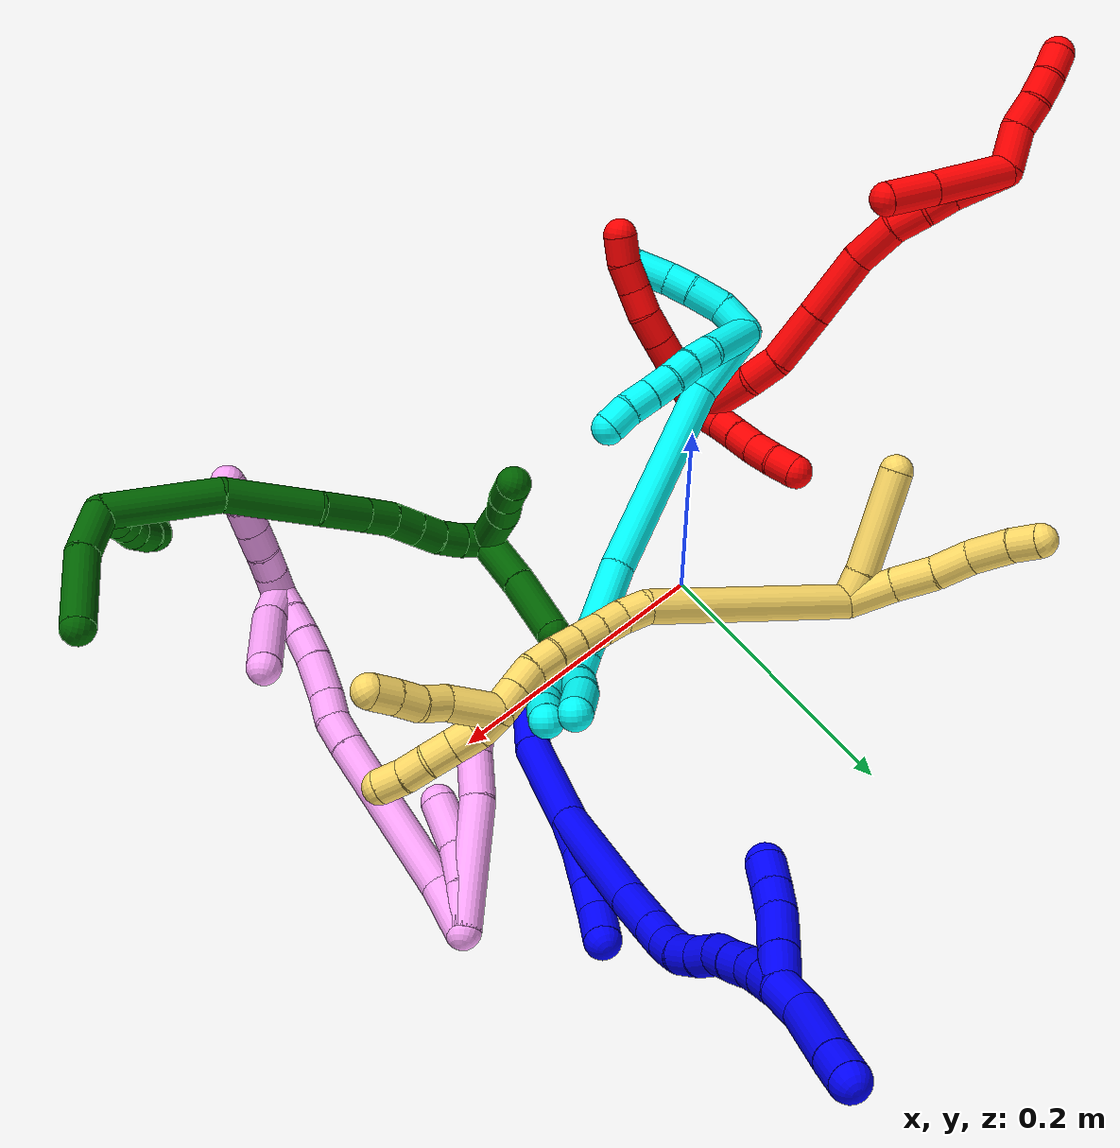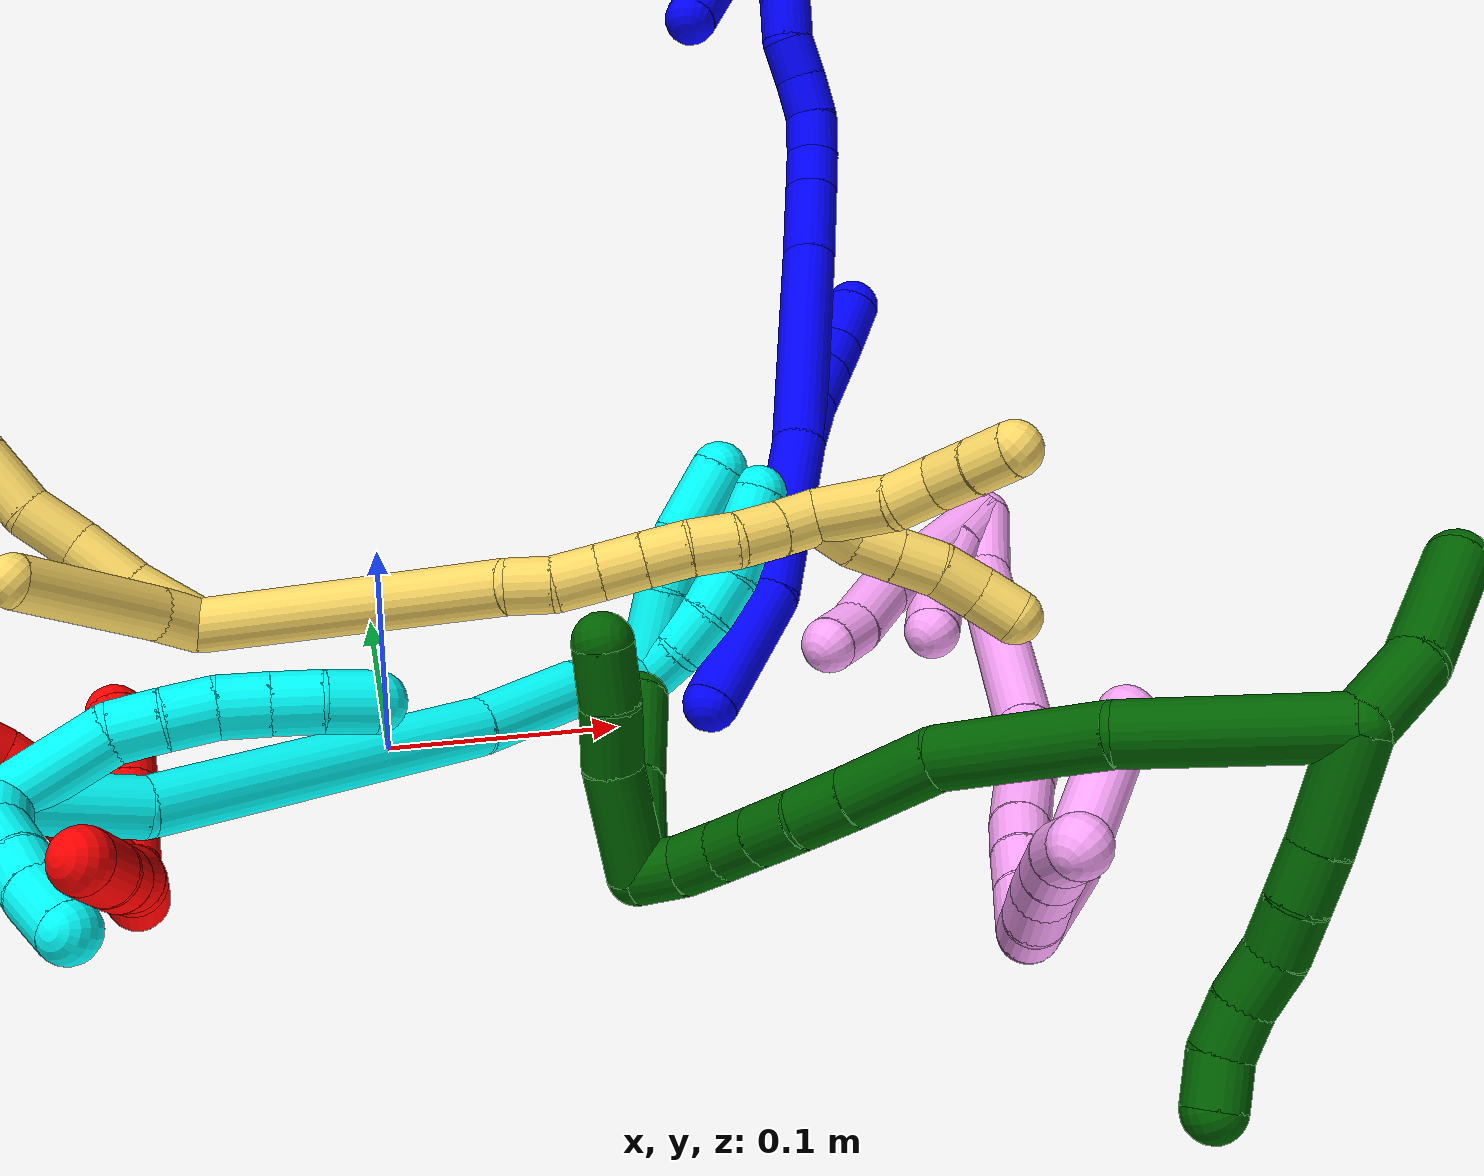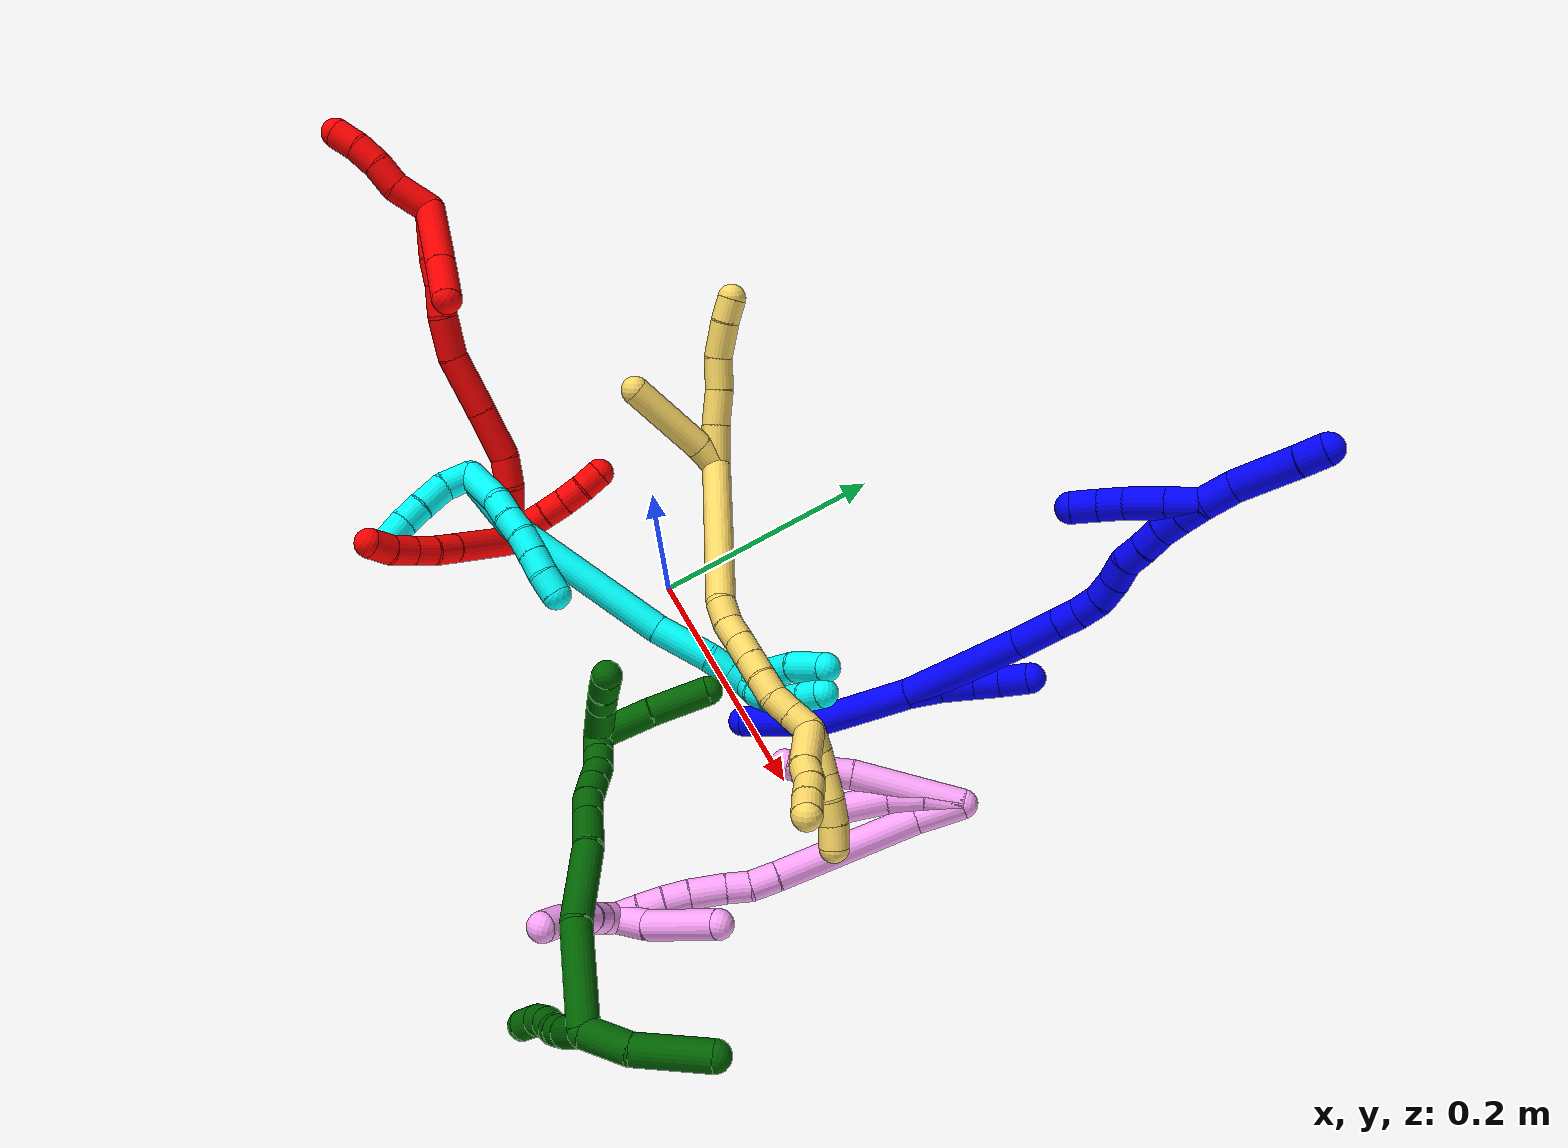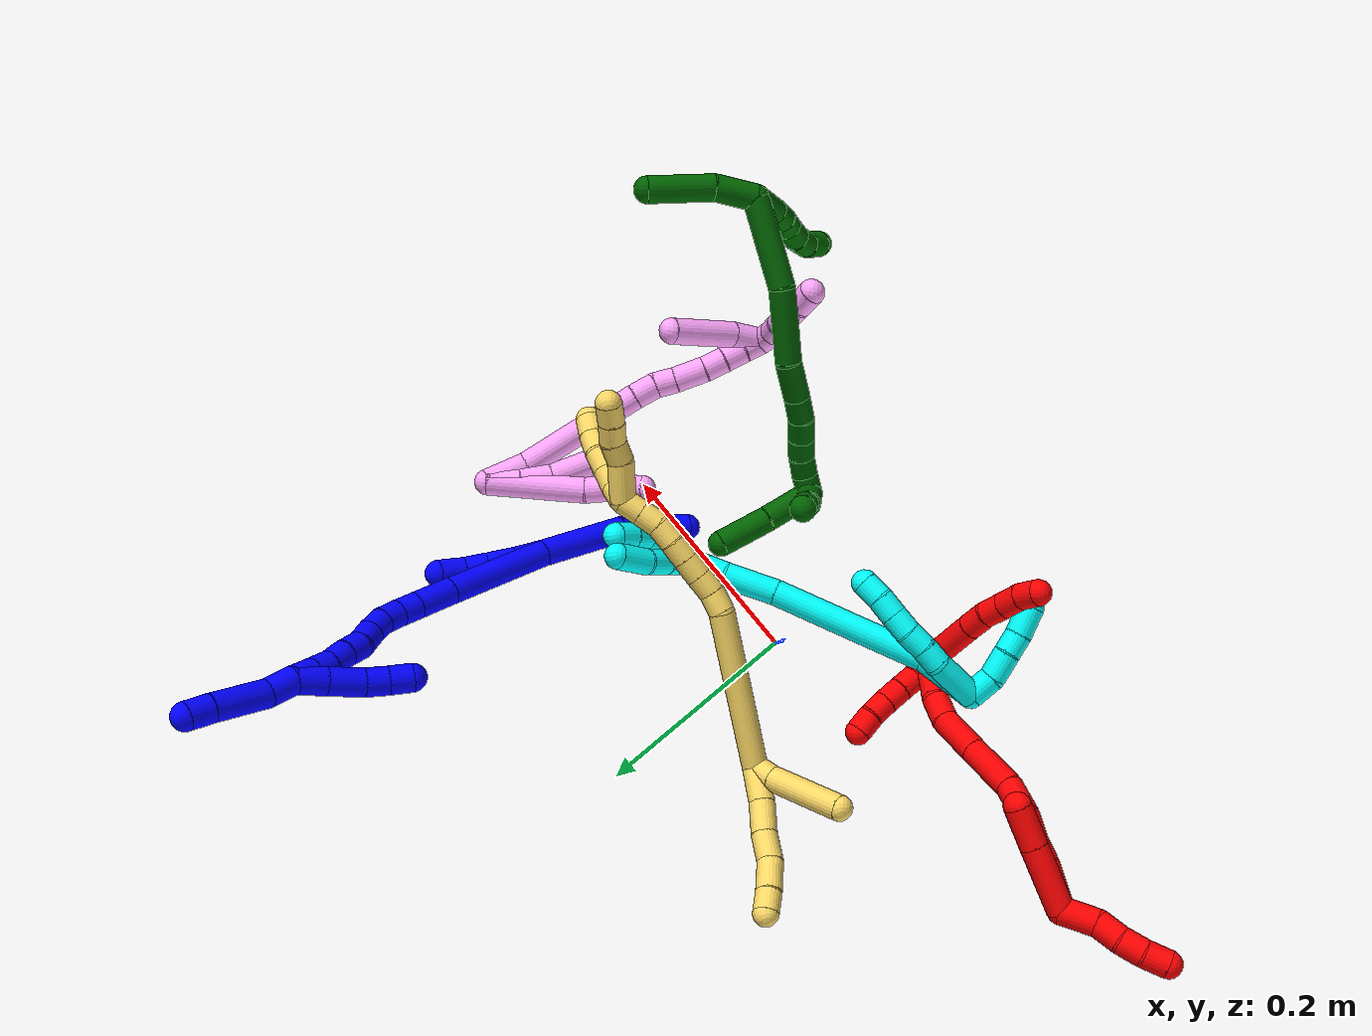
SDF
<sdf version="1.7">
 <world name="default">
  <plugin name="TubeGeneratorPlugin" filename="libtube_generator_plugin.so"/>
  <model name="photoneo_s_sensor">
   <static>1</static>
   <pose>0 0 2 1.57079 1.57079 3.14159</pose>
   <link name="link">
    <inertial><mass>0.1</mass></inertial>
    <sensor name="sensor" type="depth">
     <update_rate>30</update_rate>
     <camera>
      <horizontal_fov>1.22</horizontal_fov>
      <image><width>1920</width><height>1200</height><format>B8G8R8</format></image>
      <clip><near>0.1</near><far>4</far></clip>
      <depth_camera><output>points</output></depth_camera>
     </camera>
     <plugin name="camera_plugin" filename="libgazebo_ros_depth_camera.so">
      <baseline>0.2</baseline>
      <alwaysOn>1</alwaysOn>
      <updateRate>0.0</updateRate>
      <cameraName>camera_ir</cameraName>
      <imageTopicName>/camera/color/image_raw</imageTopicName>
      <cameraInfoTopicName>/camera/color/camera_info</cameraInfoTopicName>
      <depthImageTopicName>/camera/depth/image_raw</depthImageTopicName>
      <depthImageCameraInfoTopicName>/camera/depth/camera_info</depthImageCameraInfoTopicName>
      <pointCloudTopicName>/camera/depth/points</pointCloudTopicName>
      <frameName>fr_optical</frameName>
      <pointCloudCutoff>0.1</pointCloudCutoff>
      <pointCloudCutoffMax>2.0</pointCloudCutoffMax>
      <distortionK1>0</distortionK1>
      <distortionK2>0</distortionK2>
      <distortionK3>0</distortionK3>
      <distortionT1>0</distortionT1>
      <distortionT2>0</distortionT2>
      <CxPrime>0</CxPrime>
      <Cx>0</Cx>
      <Cy>0</Cy>
      <focalLength>0</focalLength>
      <hackBaseline>0</hackBaseline>
     </plugin>
    </sensor>
   </link>
  </model>
  <gravity>0 0 -9.8</gravity>
  <magnetic_field>6e-06 2.3e-05 -4.2e-05</magnetic_field>
  <atmosphere type="adiabatic"/>
  <physics name="default_physics" default="0" type="ode">
   <max_step_size>0.003</max_step_size>
   <real_time_factor>1</real_time_factor>
   <real_time_update_rate>1000</real_time_update_rate>
   <max_contacts>10000</max_contacts>
   <ode>
    <solver>
     <type>quick</type>
     <iters>100</iters>
     <sor>1.3</sor>
     <use_dynamic_moi_rescaling>0</use_dynamic_moi_rescaling>
    </solver>
    <constraints>
     <contact_max_correcting_vel>0</contact_max_correcting_vel>
     <contact_surface_layer>0.001</contact_surface_layer>
     <cfm>0</cfm>
     <erp>0.2</erp>
    </constraints>
   </ode>
  </physics>
  <scene><ambient>0.4 0.4 0.4 1</ambient><background>0.7 0.7 0.7 1</background><shadows>0</shadows></scene>
  <audio><device>default</device></audio>
  <spherical_coordinates>
   <surface_model>EARTH_WGS84</surface_model>
   <latitude_deg>0</latitude_deg>
   <longitude_deg>0</longitude_deg>
   <elevation>0</elevation>
   <heading_deg>0</heading_deg>
  </spherical_coordinates>
  <model name="bin">
   <static>1</static>
   <link name="bottom">
    <collision name="collision-bottom">
     <pose>0 0 -0.01 0 -0 0</pose>
     <geometry><box><size>0.8 0.6 0.02</size></box></geometry>
     <surface>
      <friction><ode><mu>100</mu><mu2>100</mu2></ode></friction>
      <contact><collide_bitmask>65535</collide_bitmask></contact>
     </surface>
    </collision>
   </link>
   <link name="west_wall">
    <collision name="collision-west_wall">
     <pose>-0.41 0 0.1 0 -0 0</pose>
     <geometry><box><size>0.02 0.6 0.2</size></box></geometry>
     <surface>
      <friction><ode><mu>100</mu><mu2>100</mu2></ode></friction>
      <contact><collide_bitmask>65535</collide_bitmask></contact>
     </surface>
    </collision>
   </link>
   <link name="east_wall">
    <collision name="collision-east_wall">
     <pose>0.41 0 0.1 0 -0 0</pose>
     <geometry><box><size>0.02 0.6 0.2</size></box></geometry>
     <surface>
      <friction><ode><mu>100</mu><mu2>100</mu2></ode></friction>
      <contact><collide_bitmask>65535</collide_bitmask></contact>
     </surface>
    </collision>
   </link>
   <link name="south_wall">
    <collision name="collision-south_wall">
     <pose>0 -0.31 0.1 0 -0 0</pose>
     <geometry><box><size>0.8 0.02 0.2</size></box></geometry>
     <surface>
      <friction><ode><mu>100</mu><mu2>100</mu2></ode></friction>
      <contact><collide_bitmask>65535</collide_bitmask></contact>
     </surface>
    </collision>
   </link>
   <link name="north_wall">
    <collision name="collision-north_wall">
     <pose>0 0.31 0.1 0 -0 0</pose>
     <geometry><box><size>0.8 0.02 0.2</size></box></geometry>
     <surface>
      <friction><ode><mu>100</mu><mu2>100</mu2></ode></friction>
      <contact><collide_bitmask>65535</collide_bitmask></contact>
     </surface>
    </collision>
   </link>
  </model>
  <model name="1">
   <static>0</static>
   <link name="1">
    <collision name="collision-cylinder-e_1_2_8">
     <pose>0.001618 -4.9e-05 -0.042204 3.14043 0.038319 3.08075</pose>
     <geometry><cylinder><radius>0.0125</radius><length>0.08447</length></cylinder></geometry>
     <surface>
      <friction><ode><mu>1.16</mu><mu2>1.16</mu2><slip1>0</slip1><slip2>0</slip2></ode></friction>
      <contact><ode><kp>1e+06</kp><kd>1</kd><max_vel>0</max_vel><min_depth>0.001</min_depth></ode></contact>
     </surface>
    </collision>
    <visual name="visual-cylinder-e_1_2_8">
     <pose>0.001618 -4.9e-05 -0.042204 3.14043 0.038319 3.08075</pose>
     <geometry><cylinder><radius>0.0125</radius><length>0.08447</length></cylinder></geometry>
     <material><ambient>0 0 1 1</ambient></material>
    </visual>
    <collision name="collision-cylinder-e_2_8_6">
     <pose>0.012809 -0.004185 -0.115476 3.0108 0.296504 2.3151</pose>
     <geometry><cylinder><radius>0.0125</radius><length>0.06553</length></cylinder></geometry>
     <surface>
      <friction><ode><mu>1.16</mu><mu2>1.16</mu2><slip1>0</slip1><slip2>0</slip2></ode></friction>
      <contact><ode><kp>1e+06</kp><kd>1</kd><max_vel>0</max_vel><min_depth>0.001</min_depth></ode></contact>
     </surface>
    </collision>
    <visual name="visual-cylinder-e_2_8_6">
     <pose>0.012809 -0.004185 -0.115476 3.0108 0.296504 2.3151</pose>
     <geometry><cylinder><radius>0.0125</radius><length>0.06553</length></cylinder></geometry>
     <material><ambient>0 0 1 1</ambient></material>
    </visual>
    <collision name="collision-cylinder-e_1_2_9">
     <pose>-0.002878 -0.00114 0.012801 0.088859 -0.220301 -0.009834</pose>
     <geometry><cylinder><radius>0.0125</radius><length>0.026339</length></cylinder></geometry>
     <surface>
      <friction><ode><mu>1.16</mu><mu2>1.16</mu2><slip1>0</slip1><slip2>0</slip2></ode></friction>
      <contact><ode><kp>1e+06</kp><kd>1</kd><max_vel>0</max_vel><min_depth>0.001</min_depth></ode></contact>
     </surface>
    </collision>
    <visual name="visual-cylinder-e_1_2_9">
     <pose>-0.002878 -0.00114 0.012801 0.088859 -0.220301 -0.009834</pose>
     <geometry><cylinder><radius>0.0125</radius><length>0.026339</length></cylinder></geometry>
     <material><ambient>0 0 1 1</ambient></material>
    </visual>
    <collision name="collision-cylinder-e_2_9_10">
     <pose>-0.009968 -0.003389 0.037918 0.089725 -0.328316 -0.014873</pose>
     <geometry><cylinder><radius>0.0125</radius><length>0.02613</length></cylinder></geometry>
     <surface>
      <friction><ode><mu>1.16</mu><mu2>1.16</mu2><slip1>0</slip1><slip2>0</slip2></ode></friction>
      <contact><ode><kp>1e+06</kp><kd>1</kd><max_vel>0</max_vel><min_depth>0.001</min_depth></ode></contact>
     </surface>
    </collision>
    <visual name="visual-cylinder-e_2_9_10">
     <pose>-0.009968 -0.003389 0.037918 0.089725 -0.328316 -0.014873</pose>
     <geometry><cylinder><radius>0.0125</radius><length>0.02613</length></cylinder></geometry>
     <material><ambient>0 0 1 1</ambient></material>
    </visual>
    <collision name="collision-cylinder-e_3_10_11">
     <pose>-0.01774 -0.005379 0.060574 0.085091 -0.330431 -0.014196</pose>
     <geometry><cylinder><radius>0.0125</radius><length>0.021939</length></cylinder></geometry>
     <surface>
      <friction><ode><mu>1.16</mu><mu2>1.16</mu2><slip1>0</slip1><slip2>0</slip2></ode></friction>
      <contact><ode><kp>1e+06</kp><kd>1</kd><max_vel>0</max_vel><min_depth>0.001</min_depth></ode></contact>
     </surface>
    </collision>
    <visual name="visual-cylinder-e_3_10_11">
     <pose>-0.01774 -0.005379 0.060574 0.085091 -0.330431 -0.014196</pose>
     <geometry><cylinder><radius>0.0125</radius><length>0.021939</length></cylinder></geometry>
     <material><ambient>0 0 1 1</ambient></material>
    </visual>
    <collision name="collision-cylinder-e_4_11_5">
     <pose>-0.023196 -0.004497 0.083444 -0.139857 -0.148766 0.010439</pose>
     <geometry><cylinder><radius>0.0125</radius><length>0.025592</length></cylinder></geometry>
     <surface>
      <friction><ode><mu>1.16</mu><mu2>1.16</mu2><slip1>0</slip1><slip2>0</slip2></ode></friction>
      <contact><ode><kp>1e+06</kp><kd>1</kd><max_vel>0</max_vel><min_depth>0.001</min_depth></ode></contact>
     </surface>
    </collision>
    <visual name="visual-cylinder-e_4_11_5">
     <pose>-0.023196 -0.004497 0.083444 -0.139857 -0.148766 0.010439</pose>
     <geometry><cylinder><radius>0.0125</radius><length>0.025592</length></cylinder></geometry>
     <material><ambient>0 0 1 1</ambient></material>
    </visual>
    <collision name="collision-cylinder-e_1_2_12">
     <pose>0.005429 5e-05 0.050999 -0.000976 0.106056 -5.2e-05</pose>
     <geometry><cylinder><radius>0.0125</radius><length>0.102573</length></cylinder></geometry>
     <surface>
      <friction><ode><mu>1.16</mu><mu2>1.16</mu2><slip1>0</slip1><slip2>0</slip2></ode></friction>
      <contact><ode><kp>1e+06</kp><kd>1</kd><max_vel>0</max_vel><min_depth>0.001</min_depth></ode></contact>
     </surface>
    </collision>
    <visual name="visual-cylinder-e_1_2_12">
     <pose>0.005429 5e-05 0.050999 -0.000976 0.106056 -5.2e-05</pose>
     <geometry><cylinder><radius>0.0125</radius><length>0.102573</length></cylinder></geometry>
     <material><ambient>0 0 1 1</ambient></material>
    </visual>
    <collision name="collision-cylinder-e_2_12_13">
     <pose>0.01356 0.00046 0.120339 -0.019657 0.146229 -0.00144</pose>
     <geometry><cylinder><radius>0.0125</radius><length>0.037088</length></cylinder></geometry>
     <surface>
      <friction><ode><mu>1.16</mu><mu2>1.16</mu2><slip1>0</slip1><slip2>0</slip2></ode></friction>
      <contact><ode><kp>1e+06</kp><kd>1</kd><max_vel>0</max_vel><min_depth>0.001</min_depth></ode></contact>
     </surface>
    </collision>
    <visual name="visual-cylinder-e_2_12_13">
     <pose>0.01356 0.00046 0.120339 -0.019657 0.146229 -0.00144</pose>
     <geometry><cylinder><radius>0.0125</radius><length>0.037088</length></cylinder></geometry>
     <material><ambient>0 0 1 1</ambient></material>
    </visual>
    <collision name="collision-cylinder-e_3_13_14">
     <pose>0.017778 0.001038 0.148612 -0.021862 0.151491 -0.001659</pose>
     <geometry><cylinder><radius>0.0125</radius><length>0.020094</length></cylinder></geometry>
     <surface>
      <friction><ode><mu>1.16</mu><mu2>1.16</mu2><slip1>0</slip1><slip2>0</slip2></ode></friction>
      <contact><ode><kp>1e+06</kp><kd>1</kd><max_vel>0</max_vel><min_depth>0.001</min_depth></ode></contact>
     </surface>
    </collision>
    <visual name="visual-cylinder-e_3_13_14">
     <pose>0.017778 0.001038 0.148612 -0.021862 0.151491 -0.001659</pose>
     <geometry><cylinder><radius>0.0125</radius><length>0.020094</length></cylinder></geometry>
     <material><ambient>0 0 1 1</ambient></material>
    </visual>
    <collision name="collision-cylinder-e_4_14_15">
     <pose>0.02241 0.002307 0.168101 -0.109589 0.313308 -0.017326</pose>
     <geometry><cylinder><radius>0.0125</radius><length>0.020219</length></cylinder></geometry>
     <surface>
      <friction><ode><mu>1.16</mu><mu2>1.16</mu2><slip1>0</slip1><slip2>0</slip2></ode></friction>
      <contact><ode><kp>1e+06</kp><kd>1</kd><max_vel>0</max_vel><min_depth>0.001</min_depth></ode></contact>
     </surface>
    </collision>
    <visual name="visual-cylinder-e_4_14_15">
     <pose>0.02241 0.002307 0.168101 -0.109589 0.313308 -0.017326</pose>
     <geometry><cylinder><radius>0.0125</radius><length>0.020219</length></cylinder></geometry>
     <material><ambient>0 0 1 1</ambient></material>
    </visual>
    <collision name="collision-cylinder-e_5_15_16">
     <pose>0.031077 0.003463 0.185988 -0.012569 0.587879 -0.003805</pose>
     <geometry><cylinder><radius>0.0125</radius><length>0.020016</length></cylinder></geometry>
     <surface>
      <friction><ode><mu>1.16</mu><mu2>1.16</mu2><slip1>0</slip1><slip2>0</slip2></ode></friction>
      <contact><ode><kp>1e+06</kp><kd>1</kd><max_vel>0</max_vel><min_depth>0.001</min_depth></ode></contact>
     </surface>
    </collision>
    <visual name="visual-cylinder-e_5_15_16">
     <pose>0.031077 0.003463 0.185988 -0.012569 0.587879 -0.003805</pose>
     <geometry><cylinder><radius>0.0125</radius><length>0.020016</length></cylinder></geometry>
     <material><ambient>0 0 1 1</ambient></material>
    </visual>
    <collision name="collision-cylinder-e_6_16_17">
     <pose>0.043248 0.004052 0.201797 -0.0646 0.723429 -0.024449</pose>
     <geometry><cylinder><radius>0.0125</radius><length>0.020004</length></cylinder></geometry>
     <surface>
      <friction><ode><mu>1.16</mu><mu2>1.16</mu2><slip1>0</slip1><slip2>0</slip2></ode></friction>
      <contact><ode><kp>1e+06</kp><kd>1</kd><max_vel>0</max_vel><min_depth>0.001</min_depth></ode></contact>
     </surface>
    </collision>
    <visual name="visual-cylinder-e_6_16_17">
     <pose>0.043248 0.004052 0.201797 -0.0646 0.723429 -0.024449</pose>
     <geometry><cylinder><radius>0.0125</radius><length>0.020004</length></cylinder></geometry>
     <material><ambient>0 0 1 1</ambient></material>
    </visual>
    <collision name="collision-cylinder-e_7_17_18">
     <pose>0.053791 0.005833 0.218387 -0.141419 0.402907 -0.028927</pose>
     <geometry><cylinder><radius>0.0125</radius><length>0.020004</length></cylinder></geometry>
     <surface>
      <friction><ode><mu>1.16</mu><mu2>1.16</mu2><slip1>0</slip1><slip2>0</slip2></ode></friction>
      <contact><ode><kp>1e+06</kp><kd>1</kd><max_vel>0</max_vel><min_depth>0.001</min_depth></ode></contact>
     </surface>
    </collision>
    <visual name="visual-cylinder-e_7_17_18">
     <pose>0.053791 0.005833 0.218387 -0.141419 0.402907 -0.028927</pose>
     <geometry><cylinder><radius>0.0125</radius><length>0.020004</length></cylinder></geometry>
     <material><ambient>0 0 1 1</ambient></material>
    </visual>
    <collision name="collision-cylinder-e_8_18_19">
     <pose>0.06221 0.00753 0.23642 -0.044783 0.466423 -0.010639</pose>
     <geometry><cylinder><radius>0.0125</radius><length>0.020001</length></cylinder></geometry>
     <surface>
      <friction><ode><mu>1.16</mu><mu2>1.16</mu2><slip1>0</slip1><slip2>0</slip2></ode></friction>
      <contact><ode><kp>1e+06</kp><kd>1</kd><max_vel>0</max_vel><min_depth>0.001</min_depth></ode></contact>
     </surface>
    </collision>
    <visual name="visual-cylinder-e_8_18_19">
     <pose>0.06221 0.00753 0.23642 -0.044783 0.466423 -0.010639</pose>
     <geometry><cylinder><radius>0.0125</radius><length>0.020001</length></cylinder></geometry>
     <material><ambient>0 0 1 1</ambient></material>
    </visual>
    <collision name="collision-cylinder-e_9_19_20">
     <pose>0.070106 0.009662 0.254587 -0.18531 0.346777 -0.032547</pose>
     <geometry><cylinder><radius>0.0125</radius><length>0.02</length></cylinder></geometry>
     <surface>
      <friction><ode><mu>1.16</mu><mu2>1.16</mu2><slip1>0</slip1><slip2>0</slip2></ode></friction>
      <contact><ode><kp>1e+06</kp><kd>1</kd><max_vel>0</max_vel><min_depth>0.001</min_depth></ode></contact>
     </surface>
    </collision>
    <visual name="visual-cylinder-e_9_19_20">
     <pose>0.070106 0.009662 0.254587 -0.18531 0.346777 -0.032547</pose>
     <geometry><cylinder><radius>0.0125</radius><length>0.02</length></cylinder></geometry>
     <material><ambient>0 0 1 1</ambient></material>
    </visual>
    <collision name="collision-cylinder-e_10_20_1">
     <pose>0.076649 0.013091 0.27317 -0.179652 0.319919 -0.029061</pose>
     <geometry><cylinder><radius>0.0125</radius><length>0.02</length></cylinder></geometry>
     <surface>
      <friction><ode><mu>1.16</mu><mu2>1.16</mu2><slip1>0</slip1><slip2>0</slip2></ode></friction>
      <contact><ode><kp>1e+06</kp><kd>1</kd><max_vel>0</max_vel><min_depth>0.001</min_depth></ode></contact>
     </surface>
    </collision>
    <visual name="visual-cylinder-e_10_20_1">
     <pose>0.076649 0.013091 0.27317 -0.179652 0.319919 -0.029061</pose>
     <geometry><cylinder><radius>0.0125</radius><length>0.02</length></cylinder></geometry>
     <material><ambient>0 0 1 1</ambient></material>
    </visual>
    <collision name="collision-cylinder-e_1_1_21">
     <pose>0.083182 0.01123 0.270246 2.85929 0.259295 1.48485</pose>
     <geometry><cylinder><radius>0.0125</radius><length>0.026422</length></cylinder></geometry>
     <surface>
      <friction><ode><mu>1.16</mu><mu2>1.16</mu2><slip1>0</slip1><slip2>0</slip2></ode></friction>
      <contact><ode><kp>1e+06</kp><kd>1</kd><max_vel>0</max_vel><min_depth>0.001</min_depth></ode></contact>
     </surface>
    </collision>
    <visual name="visual-cylinder-e_1_1_21">
     <pose>0.083182 0.01123 0.270246 2.85929 0.259295 1.48485</pose>
     <geometry><cylinder><radius>0.0125</radius><length>0.026422</length></cylinder></geometry>
     <material><ambient>0 0 1 1</ambient></material>
    </visual>
    <collision name="collision-cylinder-e_2_21_22">
     <pose>0.090524 0.003427 0.242882 2.86749 0.246997 1.46568</pose>
     <geometry><cylinder><radius>0.0125</radius><length>0.032353</length></cylinder></geometry>
     <surface>
      <friction><ode><mu>1.16</mu><mu2>1.16</mu2><slip1>0</slip1><slip2>0</slip2></ode></friction>
      <contact><ode><kp>1e+06</kp><kd>1</kd><max_vel>0</max_vel><min_depth>0.001</min_depth></ode></contact>
     </surface>
    </collision>
    <visual name="visual-cylinder-e_2_21_22">
     <pose>0.090524 0.003427 0.242882 2.86749 0.246997 1.46568</pose>
     <geometry><cylinder><radius>0.0125</radius><length>0.032353</length></cylinder></geometry>
     <material><ambient>0 0 1 1</ambient></material>
    </visual>
    <collision name="collision-cylinder-e_3_22_23">
     <pose>0.096955 -0.002178 0.217986 3.00373 0.245299 2.12049</pose>
     <geometry><cylinder><radius>0.0125</radius><length>0.020391</length></cylinder></geometry>
     <surface>
      <friction><ode><mu>1.16</mu><mu2>1.16</mu2><slip1>0</slip1><slip2>0</slip2></ode></friction>
      <contact><ode><kp>1e+06</kp><kd>1</kd><max_vel>0</max_vel><min_depth>0.001</min_depth></ode></contact>
     </surface>
    </collision>
    <visual name="visual-cylinder-e_3_22_23">
     <pose>0.096955 -0.002178 0.217986 3.00373 0.245299 2.12049</pose>
     <geometry><cylinder><radius>0.0125</radius><length>0.020391</length></cylinder></geometry>
     <material><ambient>0 0 1 1</ambient></material>
    </visual>
    <collision name="collision-cylinder-e_4_23_4">
     <pose>0.102252 -0.004164 0.198181 3.07898 0.274254 2.69528</pose>
     <geometry><cylinder><radius>0.0125</radius><length>0.020833</length></cylinder></geometry>
     <surface>
      <friction><ode><mu>1.16</mu><mu2>1.16</mu2><slip1>0</slip1><slip2>0</slip2></ode></friction>
      <contact><ode><kp>1e+06</kp><kd>1</kd><max_vel>0</max_vel><min_depth>0.001</min_depth></ode></contact>
     </surface>
    </collision>
    <visual name="visual-cylinder-e_4_23_4">
     <pose>0.102252 -0.004164 0.198181 3.07898 0.274254 2.69528</pose>
     <geometry><cylinder><radius>0.0125</radius><length>0.020833</length></cylinder></geometry>
     <material><ambient>0 0 1 1</ambient></material>
    </visual>
    <collision name="collision-cylinder-e_1_1_24">
     <pose>0.081813 0.014195 0.295543 0.045418 0.153516 0.003494</pose>
     <geometry><cylinder><radius>0.0125</radius><length>0.026403</length></cylinder></geometry>
     <surface>
      <friction><ode><mu>1.16</mu><mu2>1.16</mu2><slip1>0</slip1><slip2>0</slip2></ode></friction>
      <contact><ode><kp>1e+06</kp><kd>1</kd><max_vel>0</max_vel><min_depth>0.001</min_depth></ode></contact>
     </surface>
    </collision>
    <visual name="visual-cylinder-e_1_1_24">
     <pose>0.081813 0.014195 0.295543 0.045418 0.153516 0.003494</pose>
     <geometry><cylinder><radius>0.0125</radius><length>0.026403</length></cylinder></geometry>
     <material><ambient>0 0 1 1</ambient></material>
    </visual>
    <collision name="collision-cylinder-e_2_24_25">
     <pose>0.086846 0.018128 0.333752 -0.177817 0.117309 -0.010469</pose>
     <geometry><cylinder><radius>0.0125</radius><length>0.051514</length></cylinder></geometry>
     <surface>
      <friction><ode><mu>1.16</mu><mu2>1.16</mu2><slip1>0</slip1><slip2>0</slip2></ode></friction>
      <contact><ode><kp>1e+06</kp><kd>1</kd><max_vel>0</max_vel><min_depth>0.001</min_depth></ode></contact>
     </surface>
    </collision>
    <visual name="visual-cylinder-e_2_24_25">
     <pose>0.086846 0.018128 0.333752 -0.177817 0.117309 -0.010469</pose>
     <geometry><cylinder><radius>0.0125</radius><length>0.051514</length></cylinder></geometry>
     <material><ambient>0 0 1 1</ambient></material>
    </visual>
    <collision name="collision-cylinder-e_3_25_3">
     <pose>0.091065 0.023838 0.369841 -0.108226 0.109235 -0.005923</pose>
     <geometry><cylinder><radius>0.0125</radius><length>0.022083</length></cylinder></geometry>
     <surface>
      <friction><ode><mu>1.16</mu><mu2>1.16</mu2><slip1>0</slip1><slip2>0</slip2></ode></friction>
      <contact><ode><kp>1e+06</kp><kd>1</kd><max_vel>0</max_vel><min_depth>0.001</min_depth></ode></contact>
     </surface>
    </collision>
    <visual name="visual-cylinder-e_3_25_3">
     <pose>0.091065 0.023838 0.369841 -0.108226 0.109235 -0.005923</pose>
     <geometry><cylinder><radius>0.0125</radius><length>0.022083</length></cylinder></geometry>
     <material><ambient>0 0 1 1</ambient></material>
    </visual>
    <collision name="collision-sphere-3">
     <pose>0.092268 0.025023 0.380752 0 -0 0</pose>
     <geometry><sphere><radius>0.0125</radius></sphere></geometry>
     <surface>
      <friction><ode><mu>1.16</mu><mu2>1.16</mu2><slip1>0</slip1><slip2>0</slip2></ode></friction>
      <contact><ode><kp>1e+06</kp><kd>1</kd><max_vel>0</max_vel><min_depth>0.001</min_depth></ode></contact>
     </surface>
    </collision>
    <visual name="visual-sphere-3">
     <pose>0.092268 0.025023 0.380752 0 -0 0</pose>
     <geometry><sphere><radius>0.0125</radius></sphere></geometry>
     <material><ambient>0 0 1 1</ambient></material>
    </visual>
    <collision name="collision-sphere-25">
     <pose>0.089861 0.022652 0.358929 0 -0 0</pose>
     <geometry><sphere><radius>0.0125</radius></sphere></geometry>
     <surface>
      <friction><ode><mu>1.16</mu><mu2>1.16</mu2><slip1>0</slip1><slip2>0</slip2></ode></friction>
      <contact><ode><kp>1e+06</kp><kd>1</kd><max_vel>0</max_vel><min_depth>0.001</min_depth></ode></contact>
     </surface>
    </collision>
    <visual name="visual-sphere-25">
     <pose>0.089861 0.022652 0.358929 0 -0 0</pose>
     <geometry><sphere><radius>0.0125</radius></sphere></geometry>
     <material><ambient>0 0 1 1</ambient></material>
    </visual>
    <collision name="collision-sphere-24">
     <pose>0.083832 0.013603 0.308575 0 -0 0</pose>
     <geometry><sphere><radius>0.0125</radius></sphere></geometry>
     <surface>
      <friction><ode><mu>1.16</mu><mu2>1.16</mu2><slip1>0</slip1><slip2>0</slip2></ode></friction>
      <contact><ode><kp>1e+06</kp><kd>1</kd><max_vel>0</max_vel><min_depth>0.001</min_depth></ode></contact>
     </surface>
    </collision>
    <visual name="visual-sphere-24">
     <pose>0.083832 0.013603 0.308575 0 -0 0</pose>
     <geometry><sphere><radius>0.0125</radius></sphere></geometry>
     <material><ambient>0 0 1 1</ambient></material>
    </visual>
    <collision name="collision-sphere-4">
     <pose>0.105073 -0.004792 0.188173 0 -0 0</pose>
     <geometry><sphere><radius>0.0125</radius></sphere></geometry>
     <surface>
      <friction><ode><mu>1.16</mu><mu2>1.16</mu2><slip1>0</slip1><slip2>0</slip2></ode></friction>
      <contact><ode><kp>1e+06</kp><kd>1</kd><max_vel>0</max_vel><min_depth>0.001</min_depth></ode></contact>
     </surface>
    </collision>
    <visual name="visual-sphere-4">
     <pose>0.105073 -0.004792 0.188173 0 -0 0</pose>
     <geometry><sphere><radius>0.0125</radius></sphere></geometry>
     <material><ambient>0 0 1 1</ambient></material>
    </visual>
    <collision name="collision-sphere-23">
     <pose>0.099431 -0.003537 0.208189 0 -0 0</pose>
     <geometry><sphere><radius>0.0125</radius></sphere></geometry>
     <surface>
      <friction><ode><mu>1.16</mu><mu2>1.16</mu2><slip1>0</slip1><slip2>0</slip2></ode></friction>
      <contact><ode><kp>1e+06</kp><kd>1</kd><max_vel>0</max_vel><min_depth>0.001</min_depth></ode></contact>
     </surface>
    </collision>
    <visual name="visual-sphere-23">
     <pose>0.099431 -0.003537 0.208189 0 -0 0</pose>
     <geometry><sphere><radius>0.0125</radius></sphere></geometry>
     <material><ambient>0 0 1 1</ambient></material>
    </visual>
    <collision name="collision-sphere-22">
     <pose>0.094479 -0.000818 0.227782 0 -0 0</pose>
     <geometry><sphere><radius>0.0125</radius></sphere></geometry>
     <surface>
      <friction><ode><mu>1.16</mu><mu2>1.16</mu2><slip1>0</slip1><slip2>0</slip2></ode></friction>
      <contact><ode><kp>1e+06</kp><kd>1</kd><max_vel>0</max_vel><min_depth>0.001</min_depth></ode></contact>
     </surface>
    </collision>
    <visual name="visual-sphere-22">
     <pose>0.094479 -0.000818 0.227782 0 -0 0</pose>
     <geometry><sphere><radius>0.0125</radius></sphere></geometry>
     <material><ambient>0 0 1 1</ambient></material>
    </visual>
    <collision name="collision-sphere-21">
     <pose>0.086569 0.007673 0.257982 0 -0 0</pose>
     <geometry><sphere><radius>0.0125</radius></sphere></geometry>
     <surface>
      <friction><ode><mu>1.16</mu><mu2>1.16</mu2><slip1>0</slip1><slip2>0</slip2></ode></friction>
      <contact><ode><kp>1e+06</kp><kd>1</kd><max_vel>0</max_vel><min_depth>0.001</min_depth></ode></contact>
     </surface>
    </collision>
    <visual name="visual-sphere-21">
     <pose>0.086569 0.007673 0.257982 0 -0 0</pose>
     <geometry><sphere><radius>0.0125</radius></sphere></geometry>
     <material><ambient>0 0 1 1</ambient></material>
    </visual>
    <collision name="collision-sphere-1">
     <pose>0.079794 0.014788 0.28251 0 -0 0</pose>
     <geometry><sphere><radius>0.0125</radius></sphere></geometry>
     <surface>
      <friction><ode><mu>1.16</mu><mu2>1.16</mu2><slip1>0</slip1><slip2>0</slip2></ode></friction>
      <contact><ode><kp>1e+06</kp><kd>1</kd><max_vel>0</max_vel><min_depth>0.001</min_depth></ode></contact>
     </surface>
    </collision>
    <visual name="visual-sphere-1">
     <pose>0.079794 0.014788 0.28251 0 -0 0</pose>
     <geometry><sphere><radius>0.0125</radius></sphere></geometry>
     <material><ambient>0 0 1 1</ambient></material>
    </visual>
    <collision name="collision-sphere-11">
     <pose>-0.021299 -0.006261 0.070913 0 -0 0</pose>
     <geometry><sphere><radius>0.0125</radius></sphere></geometry>
     <surface>
      <friction><ode><mu>1.16</mu><mu2>1.16</mu2><slip1>0</slip1><slip2>0</slip2></ode></friction>
      <contact><ode><kp>1e+06</kp><kd>1</kd><max_vel>0</max_vel><min_depth>0.001</min_depth></ode></contact>
     </surface>
    </collision>
    <visual name="visual-sphere-11">
     <pose>-0.021299 -0.006261 0.070913 0 -0 0</pose>
     <geometry><sphere><radius>0.0125</radius></sphere></geometry>
     <material><ambient>0 0 1 1</ambient></material>
    </visual>
    <collision name="collision-sphere-10">
     <pose>-0.014181 -0.004497 0.050236 0 -0 0</pose>
     <geometry><sphere><radius>0.0125</radius></sphere></geometry>
     <surface>
      <friction><ode><mu>1.16</mu><mu2>1.16</mu2><slip1>0</slip1><slip2>0</slip2></ode></friction>
      <contact><ode><kp>1e+06</kp><kd>1</kd><max_vel>0</max_vel><min_depth>0.001</min_depth></ode></contact>
     </surface>
    </collision>
    <visual name="visual-sphere-10">
     <pose>-0.014181 -0.004497 0.050236 0 -0 0</pose>
     <geometry><sphere><radius>0.0125</radius></sphere></geometry>
     <material><ambient>0 0 1 1</ambient></material>
    </visual>
    <collision name="collision-sphere-6">
     <pose>0.022382 -0.008272 -0.146543 0 -0 0</pose>
     <geometry><sphere><radius>0.0125</radius></sphere></geometry>
     <surface>
      <friction><ode><mu>1.16</mu><mu2>1.16</mu2><slip1>0</slip1><slip2>0</slip2></ode></friction>
      <contact><ode><kp>1e+06</kp><kd>1</kd><max_vel>0</max_vel><min_depth>0.001</min_depth></ode></contact>
     </surface>
    </collision>
    <visual name="visual-sphere-6">
     <pose>0.022382 -0.008272 -0.146543 0 -0 0</pose>
     <geometry><sphere><radius>0.0125</radius></sphere></geometry>
     <material><ambient>0 0 1 1</ambient></material>
    </visual>
    <collision name="collision-sphere-9">
     <pose>-0.005756 -0.002281 0.025601 0 -0 0</pose>
     <geometry><sphere><radius>0.0125</radius></sphere></geometry>
     <surface>
      <friction><ode><mu>1.16</mu><mu2>1.16</mu2><slip1>0</slip1><slip2>0</slip2></ode></friction>
      <contact><ode><kp>1e+06</kp><kd>1</kd><max_vel>0</max_vel><min_depth>0.001</min_depth></ode></contact>
     </surface>
    </collision>
    <visual name="visual-sphere-9">
     <pose>-0.005756 -0.002281 0.025601 0 -0 0</pose>
     <geometry><sphere><radius>0.0125</radius></sphere></geometry>
     <material><ambient>0 0 1 1</ambient></material>
    </visual>
    <collision name="collision-sphere-2">
     <geometry><sphere><radius>0.0125</radius></sphere></geometry>
     <surface>
      <friction><ode><mu>1.16</mu><mu2>1.16</mu2><slip1>0</slip1><slip2>0</slip2></ode></friction>
      <contact><ode><kp>1e+06</kp><kd>1</kd><max_vel>0</max_vel><min_depth>0.001</min_depth></ode></contact>
     </surface>
    </collision>
    <visual name="visual-sphere-2">
     <geometry><sphere><radius>0.0125</radius></sphere></geometry>
     <material><ambient>0 0 1 1</ambient></material>
    </visual>
    <collision name="collision-sphere-19">
     <pose>0.066707 0.007929 0.245343 0 -0 0</pose>
     <geometry><sphere><radius>0.0125</radius></sphere></geometry>
     <surface>
      <friction><ode><mu>1.16</mu><mu2>1.16</mu2><slip1>0</slip1><slip2>0</slip2></ode></friction>
      <contact><ode><kp>1e+06</kp><kd>1</kd><max_vel>0</max_vel><min_depth>0.001</min_depth></ode></contact>
     </surface>
    </collision>
    <visual name="visual-sphere-19">
     <pose>0.066707 0.007929 0.245343 0 -0 0</pose>
     <geometry><sphere><radius>0.0125</radius></sphere></geometry>
     <material><ambient>0 0 1 1</ambient></material>
    </visual>
    <collision name="collision-sphere-8">
     <pose>0.003236 -9.8e-05 -0.084408 0 -0 0</pose>
     <geometry><sphere><radius>0.0125</radius></sphere></geometry>
     <surface>
      <friction><ode><mu>1.16</mu><mu2>1.16</mu2><slip1>0</slip1><slip2>0</slip2></ode></friction>
      <contact><ode><kp>1e+06</kp><kd>1</kd><max_vel>0</max_vel><min_depth>0.001</min_depth></ode></contact>
     </surface>
    </collision>
    <visual name="visual-sphere-8">
     <pose>0.003236 -9.8e-05 -0.084408 0 -0 0</pose>
     <geometry><sphere><radius>0.0125</radius></sphere></geometry>
     <material><ambient>0 0 1 1</ambient></material>
    </visual>
    <collision name="collision-sphere-5">
     <pose>-0.025093 -0.002733 0.095975 0 -0 0</pose>
     <geometry><sphere><radius>0.0125</radius></sphere></geometry>
     <surface>
      <friction><ode><mu>1.16</mu><mu2>1.16</mu2><slip1>0</slip1><slip2>0</slip2></ode></friction>
      <contact><ode><kp>1e+06</kp><kd>1</kd><max_vel>0</max_vel><min_depth>0.001</min_depth></ode></contact>
     </surface>
    </collision>
    <visual name="visual-sphere-5">
     <pose>-0.025093 -0.002733 0.095975 0 -0 0</pose>
     <geometry><sphere><radius>0.0125</radius></sphere></geometry>
     <material><ambient>0 0 1 1</ambient></material>
    </visual>
    <collision name="collision-sphere-12">
     <pose>0.010858 0.0001 0.101997 0 -0 0</pose>
     <geometry><sphere><radius>0.0125</radius></sphere></geometry>
     <surface>
      <friction><ode><mu>1.16</mu><mu2>1.16</mu2><slip1>0</slip1><slip2>0</slip2></ode></friction>
      <contact><ode><kp>1e+06</kp><kd>1</kd><max_vel>0</max_vel><min_depth>0.001</min_depth></ode></contact>
     </surface>
    </collision>
    <visual name="visual-sphere-12">
     <pose>0.010858 0.0001 0.101997 0 -0 0</pose>
     <geometry><sphere><radius>0.0125</radius></sphere></geometry>
     <material><ambient>0 0 1 1</ambient></material>
    </visual>
    <collision name="collision-sphere-13">
     <pose>0.016262 0.000821 0.138682 0 -0 0</pose>
     <geometry><sphere><radius>0.0125</radius></sphere></geometry>
     <surface>
      <friction><ode><mu>1.16</mu><mu2>1.16</mu2><slip1>0</slip1><slip2>0</slip2></ode></friction>
      <contact><ode><kp>1e+06</kp><kd>1</kd><max_vel>0</max_vel><min_depth>0.001</min_depth></ode></contact>
     </surface>
    </collision>
    <visual name="visual-sphere-13">
     <pose>0.016262 0.000821 0.138682 0 -0 0</pose>
     <geometry><sphere><radius>0.0125</radius></sphere></geometry>
     <material><ambient>0 0 1 1</ambient></material>
    </visual>
    <collision name="collision-sphere-14">
     <pose>0.019295 0.001255 0.158541 0 -0 0</pose>
     <geometry><sphere><radius>0.0125</radius></sphere></geometry>
     <surface>
      <friction><ode><mu>1.16</mu><mu2>1.16</mu2><slip1>0</slip1><slip2>0</slip2></ode></friction>
      <contact><ode><kp>1e+06</kp><kd>1</kd><max_vel>0</max_vel><min_depth>0.001</min_depth></ode></contact>
     </surface>
    </collision>
    <visual name="visual-sphere-14">
     <pose>0.019295 0.001255 0.158541 0 -0 0</pose>
     <geometry><sphere><radius>0.0125</radius></sphere></geometry>
     <material><ambient>0 0 1 1</ambient></material>
    </visual>
    <collision name="collision-sphere-15">
     <pose>0.025526 0.003359 0.17766 0 -0 0</pose>
     <geometry><sphere><radius>0.0125</radius></sphere></geometry>
     <surface>
      <friction><ode><mu>1.16</mu><mu2>1.16</mu2><slip1>0</slip1><slip2>0</slip2></ode></friction>
      <contact><ode><kp>1e+06</kp><kd>1</kd><max_vel>0</max_vel><min_depth>0.001</min_depth></ode></contact>
     </surface>
    </collision>
    <visual name="visual-sphere-15">
     <pose>0.025526 0.003359 0.17766 0 -0 0</pose>
     <geometry><sphere><radius>0.0125</radius></sphere></geometry>
     <material><ambient>0 0 1 1</ambient></material>
    </visual>
    <collision name="collision-sphere-16">
     <pose>0.036627 0.003568 0.194315 0 -0 0</pose>
     <geometry><sphere><radius>0.0125</radius></sphere></geometry>
     <surface>
      <friction><ode><mu>1.16</mu><mu2>1.16</mu2><slip1>0</slip1><slip2>0</slip2></ode></friction>
      <contact><ode><kp>1e+06</kp><kd>1</kd><max_vel>0</max_vel><min_depth>0.001</min_depth></ode></contact>
     </surface>
    </collision>
    <visual name="visual-sphere-16">
     <pose>0.036627 0.003568 0.194315 0 -0 0</pose>
     <geometry><sphere><radius>0.0125</radius></sphere></geometry>
     <material><ambient>0 0 1 1</ambient></material>
    </visual>
    <collision name="collision-sphere-17">
     <pose>0.049869 0.004536 0.209278 0 -0 0</pose>
     <geometry><sphere><radius>0.0125</radius></sphere></geometry>
     <surface>
      <friction><ode><mu>1.16</mu><mu2>1.16</mu2><slip1>0</slip1><slip2>0</slip2></ode></friction>
      <contact><ode><kp>1e+06</kp><kd>1</kd><max_vel>0</max_vel><min_depth>0.001</min_depth></ode></contact>
     </surface>
    </collision>
    <visual name="visual-sphere-17">
     <pose>0.049869 0.004536 0.209278 0 -0 0</pose>
     <geometry><sphere><radius>0.0125</radius></sphere></geometry>
     <material><ambient>0 0 1 1</ambient></material>
    </visual>
    <collision name="collision-sphere-18">
     <pose>0.057713 0.00713 0.227496 0 -0 0</pose>
     <geometry><sphere><radius>0.0125</radius></sphere></geometry>
     <surface>
      <friction><ode><mu>1.16</mu><mu2>1.16</mu2><slip1>0</slip1><slip2>0</slip2></ode></friction>
      <contact><ode><kp>1e+06</kp><kd>1</kd><max_vel>0</max_vel><min_depth>0.001</min_depth></ode></contact>
     </surface>
    </collision>
    <visual name="visual-sphere-18">
     <pose>0.057713 0.00713 0.227496 0 -0 0</pose>
     <geometry><sphere><radius>0.0125</radius></sphere></geometry>
     <material><ambient>0 0 1 1</ambient></material>
    </visual>
    <collision name="collision-sphere-20">
     <pose>0.073504 0.011395 0.26383 0 -0 0</pose>
     <geometry><sphere><radius>0.0125</radius></sphere></geometry>
     <surface>
      <friction><ode><mu>1.16</mu><mu2>1.16</mu2><slip1>0</slip1><slip2>0</slip2></ode></friction>
      <contact><ode><kp>1e+06</kp><kd>1</kd><max_vel>0</max_vel><min_depth>0.001</min_depth></ode></contact>
     </surface>
    </collision>
    <visual name="visual-sphere-20">
     <pose>0.073504 0.011395 0.26383 0 -0 0</pose>
     <geometry><sphere><radius>0.0125</radius></sphere></geometry>
     <material><ambient>0 0 1 1</ambient></material>
    </visual>
    <inertial>
     <pose>0.034865 0.003258 0.125183 0 -0 0</pose>
     <mass>0.75</mass>
     <inertia><ixx>0.000103</ixx><ixy>0</ixy><ixz>0</ixz><iyy>0.000241</iyy><iyz>0</iyz><izz>-7e-06</izz></inertia>
    </inertial>
   </link>
   <pose>0.204588 0.116532 0.068358 0.909636 -0.731635 -2.99179</pose>
  </model>
  <model name="2">
   <static>0</static>
   <link name="2">
    <collision name="collision-cylinder-e_1_2_8">
     <pose>0.016877 -0.012979 0.024154 0.49307 0.55174 0.14224</pose>
     <geometry><cylinder><radius>0.0125</radius><length>0.064397</length></cylinder></geometry>
     <surface>
      <friction><ode><mu>1.16</mu><mu2>1.16</mu2><slip1>0</slip1><slip2>0</slip2></ode></friction>
      <contact><ode><kp>1e+06</kp><kd>1</kd><max_vel>0</max_vel><min_depth>0.001</min_depth></ode></contact>
     </surface>
    </collision>
    <visual name="visual-cylinder-e_1_2_8">
     <pose>0.016877 -0.012979 0.024154 0.49307 0.55174 0.14224</pose>
     <geometry><cylinder><radius>0.0125</radius><length>0.064397</length></cylinder></geometry>
     <material><ambient>1 0 0 1</ambient></material>
    </visual>
    <collision name="collision-cylinder-e_2_8_9">
     <pose>0.039417 -0.030623 0.056951 0.494927 0.522995 0.135021</pose>
     <geometry><cylinder><radius>0.0125</radius><length>0.022672</length></cylinder></geometry>
     <surface>
      <friction><ode><mu>1.16</mu><mu2>1.16</mu2><slip1>0</slip1><slip2>0</slip2></ode></friction>
      <contact><ode><kp>1e+06</kp><kd>1</kd><max_vel>0</max_vel><min_depth>0.001</min_depth></ode></contact>
     </surface>
    </collision>
    <visual name="visual-cylinder-e_2_8_9">
     <pose>0.039417 -0.030623 0.056951 0.494927 0.522995 0.135021</pose>
     <geometry><cylinder><radius>0.0125</radius><length>0.022672</length></cylinder></geometry>
     <material><ambient>1 0 0 1</ambient></material>
    </visual>
    <collision name="collision-cylinder-e_3_9_10">
     <pose>0.048563 -0.039375 0.074345 0.437 0.346146 0.077598</pose>
     <geometry><cylinder><radius>0.0125</radius><length>0.020538</length></cylinder></geometry>
     <surface>
      <friction><ode><mu>1.16</mu><mu2>1.16</mu2><slip1>0</slip1><slip2>0</slip2></ode></friction>
      <contact><ode><kp>1e+06</kp><kd>1</kd><max_vel>0</max_vel><min_depth>0.001</min_depth></ode></contact>
     </surface>
    </collision>
    <visual name="visual-cylinder-e_3_9_10">
     <pose>0.048563 -0.039375 0.074345 0.437 0.346146 0.077598</pose>
     <geometry><cylinder><radius>0.0125</radius><length>0.020538</length></cylinder></geometry>
     <material><ambient>1 0 0 1</ambient></material>
    </visual>
    <collision name="collision-cylinder-e_4_10_11">
     <pose>0.056585 -0.04706 0.092208 0.375941 0.433829 0.083791</pose>
     <geometry><cylinder><radius>0.0125</radius><length>0.02159</length></cylinder></geometry>
     <surface>
      <friction><ode><mu>1.16</mu><mu2>1.16</mu2><slip1>0</slip1><slip2>0</slip2></ode></friction>
      <contact><ode><kp>1e+06</kp><kd>1</kd><max_vel>0</max_vel><min_depth>0.001</min_depth></ode></contact>
     </surface>
    </collision>
    <visual name="visual-cylinder-e_4_10_11">
     <pose>0.056585 -0.04706 0.092208 0.375941 0.433829 0.083791</pose>
     <geometry><cylinder><radius>0.0125</radius><length>0.02159</length></cylinder></geometry>
     <material><ambient>1 0 0 1</ambient></material>
    </visual>
    <collision name="collision-cylinder-e_5_11_6">
     <pose>0.064417 -0.05215 0.111072 0.152048 0.322289 0.024762</pose>
     <geometry><cylinder><radius>0.0125</radius><length>0.020803</length></cylinder></geometry>
     <surface>
      <friction><ode><mu>1.16</mu><mu2>1.16</mu2><slip1>0</slip1><slip2>0</slip2></ode></friction>
      <contact><ode><kp>1e+06</kp><kd>1</kd><max_vel>0</max_vel><min_depth>0.001</min_depth></ode></contact>
     </surface>
    </collision>
    <visual name="visual-cylinder-e_5_11_6">
     <pose>0.064417 -0.05215 0.111072 0.152048 0.322289 0.024762</pose>
     <geometry><cylinder><radius>0.0125</radius><length>0.020803</length></cylinder></geometry>
     <material><ambient>1 0 0 1</ambient></material>
    </visual>
    <collision name="collision-cylinder-e_1_2_12">
     <pose>-0.000356 0.009503 -0.003093 -1.88544 -0.035581 0.048993</pose>
     <geometry><cylinder><radius>0.0125</radius><length>0.02</length></cylinder></geometry>
     <surface>
      <friction><ode><mu>1.16</mu><mu2>1.16</mu2><slip1>0</slip1><slip2>0</slip2></ode></friction>
      <contact><ode><kp>1e+06</kp><kd>1</kd><max_vel>0</max_vel><min_depth>0.001</min_depth></ode></contact>
     </surface>
    </collision>
    <visual name="visual-cylinder-e_1_2_12">
     <pose>-0.000356 0.009503 -0.003093 -1.88544 -0.035581 0.048993</pose>
     <geometry><cylinder><radius>0.0125</radius><length>0.02</length></cylinder></geometry>
     <material><ambient>1 0 0 1</ambient></material>
    </visual>
    <collision name="collision-cylinder-e_2_12_13">
     <pose>0.001521 0.028246 -0.009291 -1.89504 0.225188 -0.312028</pose>
     <geometry><cylinder><radius>0.0125</radius><length>0.02</length></cylinder></geometry>
     <surface>
      <friction><ode><mu>1.16</mu><mu2>1.16</mu2><slip1>0</slip1><slip2>0</slip2></ode></friction>
      <contact><ode><kp>1e+06</kp><kd>1</kd><max_vel>0</max_vel><min_depth>0.001</min_depth></ode></contact>
     </surface>
    </collision>
    <visual name="visual-cylinder-e_2_12_13">
     <pose>0.001521 0.028246 -0.009291 -1.89504 0.225188 -0.312028</pose>
     <geometry><cylinder><radius>0.0125</radius><length>0.02</length></cylinder></geometry>
     <material><ambient>1 0 0 1</ambient></material>
    </visual>
    <collision name="collision-cylinder-e_3_13_14">
     <pose>0.005555 0.046759 -0.015675 -1.91058 0.181104 -0.255412</pose>
     <geometry><cylinder><radius>0.0125</radius><length>0.02</length></cylinder></geometry>
     <surface>
      <friction><ode><mu>1.16</mu><mu2>1.16</mu2><slip1>0</slip1><slip2>0</slip2></ode></friction>
      <contact><ode><kp>1e+06</kp><kd>1</kd><max_vel>0</max_vel><min_depth>0.001</min_depth></ode></contact>
     </surface>
    </collision>
    <visual name="visual-cylinder-e_3_13_14">
     <pose>0.005555 0.046759 -0.015675 -1.91058 0.181104 -0.255412</pose>
     <geometry><cylinder><radius>0.0125</radius><length>0.02</length></cylinder></geometry>
     <material><ambient>1 0 0 1</ambient></material>
    </visual>
    <collision name="collision-cylinder-e_4_14_15">
     <pose>0.00923 0.065503 -0.021565 -1.83994 0.188484 -0.246985</pose>
     <geometry><cylinder><radius>0.0125</radius><length>0.02</length></cylinder></geometry>
     <surface>
      <friction><ode><mu>1.16</mu><mu2>1.16</mu2><slip1>0</slip1><slip2>0</slip2></ode></friction>
      <contact><ode><kp>1e+06</kp><kd>1</kd><max_vel>0</max_vel><min_depth>0.001</min_depth></ode></contact>
     </surface>
    </collision>
    <visual name="visual-cylinder-e_4_14_15">
     <pose>0.00923 0.065503 -0.021565 -1.83994 0.188484 -0.246985</pose>
     <geometry><cylinder><radius>0.0125</radius><length>0.02</length></cylinder></geometry>
     <material><ambient>1 0 0 1</ambient></material>
    </visual>
    <collision name="collision-cylinder-e_5_15_5">
     <pose>0.011247 0.084649 -0.026694 -1.82527 0.014296 -0.01849</pose>
     <geometry><cylinder><radius>0.0125</radius><length>0.02</length></cylinder></geometry>
     <surface>
      <friction><ode><mu>1.16</mu><mu2>1.16</mu2><slip1>0</slip1><slip2>0</slip2></ode></friction>
      <contact><ode><kp>1e+06</kp><kd>1</kd><max_vel>0</max_vel><min_depth>0.001</min_depth></ode></contact>
     </surface>
    </collision>
    <visual name="visual-cylinder-e_5_15_5">
     <pose>0.011247 0.084649 -0.026694 -1.82527 0.014296 -0.01849</pose>
     <geometry><cylinder><radius>0.0125</radius><length>0.02</length></cylinder></geometry>
     <material><ambient>1 0 0 1</ambient></material>
    </visual>
    <collision name="collision-cylinder-e_1_2_16">
     <pose>0.00378 0.021214 0.015333 -0.944963 0.143418 -0.073392</pose>
     <geometry><cylinder><radius>0.0125</radius><length>0.052893</length></cylinder></geometry>
     <surface>
      <friction><ode><mu>1.16</mu><mu2>1.16</mu2><slip1>0</slip1><slip2>0</slip2></ode></friction>
      <contact><ode><kp>1e+06</kp><kd>1</kd><max_vel>0</max_vel><min_depth>0.001</min_depth></ode></contact>
     </surface>
    </collision>
    <visual name="visual-cylinder-e_1_2_16">
     <pose>0.00378 0.021214 0.015333 -0.944963 0.143418 -0.073392</pose>
     <geometry><cylinder><radius>0.0125</radius><length>0.052893</length></cylinder></geometry>
     <material><ambient>1 0 0 1</ambient></material>
    </visual>
    <collision name="collision-cylinder-e_2_16_17">
     <pose>0.00616 0.05154 0.039436 -0.804463 -0.110269 0.04695</pose>
     <geometry><cylinder><radius>0.0125</radius><length>0.025448</length></cylinder></geometry>
     <surface>
      <friction><ode><mu>1.16</mu><mu2>1.16</mu2><slip1>0</slip1><slip2>0</slip2></ode></friction>
      <contact><ode><kp>1e+06</kp><kd>1</kd><max_vel>0</max_vel><min_depth>0.001</min_depth></ode></contact>
     </surface>
    </collision>
    <visual name="visual-cylinder-e_2_16_17">
     <pose>0.00616 0.05154 0.039436 -0.804463 -0.110269 0.04695</pose>
     <geometry><cylinder><radius>0.0125</radius><length>0.025448</length></cylinder></geometry>
     <material><ambient>1 0 0 1</ambient></material>
    </visual>
    <collision name="collision-cylinder-e_3_17_18">
     <pose>0.002717 0.071593 0.067598 -0.513721 -0.091454 0.024037</pose>
     <geometry><cylinder><radius>0.0125</radius><length>0.044718</length></cylinder></geometry>
     <surface>
      <friction><ode><mu>1.16</mu><mu2>1.16</mu2><slip1>0</slip1><slip2>0</slip2></ode></friction>
      <contact><ode><kp>1e+06</kp><kd>1</kd><max_vel>0</max_vel><min_depth>0.001</min_depth></ode></contact>
     </surface>
    </collision>
    <visual name="visual-cylinder-e_3_17_18">
     <pose>0.002717 0.071593 0.067598 -0.513721 -0.091454 0.024037</pose>
     <geometry><cylinder><radius>0.0125</radius><length>0.044718</length></cylinder></geometry>
     <material><ambient>1 0 0 1</ambient></material>
    </visual>
    <collision name="collision-cylinder-e_4_18_19">
     <pose>-0.001893 0.094754 0.109517 -0.496986 -0.099869 0.02536</pose>
     <geometry><cylinder><radius>0.0125</radius><length>0.051512</length></cylinder></geometry>
     <surface>
      <friction><ode><mu>1.16</mu><mu2>1.16</mu2><slip1>0</slip1><slip2>0</slip2></ode></friction>
      <contact><ode><kp>1e+06</kp><kd>1</kd><max_vel>0</max_vel><min_depth>0.001</min_depth></ode></contact>
     </surface>
    </collision>
    <visual name="visual-cylinder-e_4_18_19">
     <pose>-0.001893 0.094754 0.109517 -0.496986 -0.099869 0.02536</pose>
     <geometry><cylinder><radius>0.0125</radius><length>0.051512</length></cylinder></geometry>
     <material><ambient>1 0 0 1</ambient></material>
    </visual>
    <collision name="collision-cylinder-e_5_19_20">
     <pose>-0.004697 0.118763 0.145216 -0.730116 -0.013382 0.005115</pose>
     <geometry><cylinder><radius>0.0125</radius><length>0.035358</length></cylinder></geometry>
     <surface>
      <friction><ode><mu>1.16</mu><mu2>1.16</mu2><slip1>0</slip1><slip2>0</slip2></ode></friction>
      <contact><ode><kp>1e+06</kp><kd>1</kd><max_vel>0</max_vel><min_depth>0.001</min_depth></ode></contact>
     </surface>
    </collision>
    <visual name="visual-cylinder-e_5_19_20">
     <pose>-0.004697 0.118763 0.145216 -0.730116 -0.013382 0.005115</pose>
     <geometry><cylinder><radius>0.0125</radius><length>0.035358</length></cylinder></geometry>
     <material><ambient>1 0 0 1</ambient></material>
    </visual>
    <collision name="collision-cylinder-e_6_20_21">
     <pose>-0.007072 0.140562 0.166001 -0.920513 -0.16841 0.083642</pose>
     <geometry><cylinder><radius>0.0125</radius><length>0.025512</length></cylinder></geometry>
     <surface>
      <friction><ode><mu>1.16</mu><mu2>1.16</mu2><slip1>0</slip1><slip2>0</slip2></ode></friction>
      <contact><ode><kp>1e+06</kp><kd>1</kd><max_vel>0</max_vel><min_depth>0.001</min_depth></ode></contact>
     </surface>
    </collision>
    <visual name="visual-cylinder-e_6_20_21">
     <pose>-0.007072 0.140562 0.166001 -0.920513 -0.16841 0.083642</pose>
     <geometry><cylinder><radius>0.0125</radius><length>0.025512</length></cylinder></geometry>
     <material><ambient>1 0 0 1</ambient></material>
    </visual>
    <collision name="collision-cylinder-e_7_21_22">
     <pose>-0.013237 0.158214 0.180826 -0.814444 -0.36595 0.159294</pose>
     <geometry><cylinder><radius>0.0125</radius><length>0.022507</length></cylinder></geometry>
     <surface>
      <friction><ode><mu>1.16</mu><mu2>1.16</mu2><slip1>0</slip1><slip2>0</slip2></ode></friction>
      <contact><ode><kp>1e+06</kp><kd>1</kd><max_vel>0</max_vel><min_depth>0.001</min_depth></ode></contact>
     </surface>
    </collision>
    <visual name="visual-cylinder-e_7_21_22">
     <pose>-0.013237 0.158214 0.180826 -0.814444 -0.36595 0.159294</pose>
     <geometry><cylinder><radius>0.0125</radius><length>0.022507</length></cylinder></geometry>
     <material><ambient>1 0 0 1</ambient></material>
    </visual>
    <collision name="collision-cylinder-e_8_22_1">
     <pose>-0.024547 0.181867 0.199557 -0.947083 -0.353726 0.182664</pose>
     <geometry><cylinder><radius>0.0125</radius><length>0.042051</length></cylinder></geometry>
     <surface>
      <friction><ode><mu>1.16</mu><mu2>1.16</mu2><slip1>0</slip1><slip2>0</slip2></ode></friction>
      <contact><ode><kp>1e+06</kp><kd>1</kd><max_vel>0</max_vel><min_depth>0.001</min_depth></ode></contact>
     </surface>
    </collision>
    <visual name="visual-cylinder-e_8_22_1">
     <pose>-0.024547 0.181867 0.199557 -0.947083 -0.353726 0.182664</pose>
     <geometry><cylinder><radius>0.0125</radius><length>0.042051</length></cylinder></geometry>
     <material><ambient>1 0 0 1</ambient></material>
    </visual>
    <collision name="collision-cylinder-e_1_1_23">
     <pose>-0.007723 0.181681 0.19997 2.1719 0.887189 1.46788</pose>
     <geometry><cylinder><radius>0.0125</radius><length>0.062187</length></cylinder></geometry>
     <surface>
      <friction><ode><mu>1.16</mu><mu2>1.16</mu2><slip1>0</slip1><slip2>0</slip2></ode></friction>
      <contact><ode><kp>1e+06</kp><kd>1</kd><max_vel>0</max_vel><min_depth>0.001</min_depth></ode></contact>
     </surface>
    </collision>
    <visual name="visual-cylinder-e_1_1_23">
     <pose>-0.007723 0.181681 0.19997 2.1719 0.887189 1.46788</pose>
     <geometry><cylinder><radius>0.0125</radius><length>0.062187</length></cylinder></geometry>
     <material><ambient>1 0 0 1</ambient></material>
    </visual>
    <collision name="collision-cylinder-e_2_23_4">
     <pose>0.031198 0.155652 0.182437 2.14966 0.900372 1.45808</pose>
     <geometry><cylinder><radius>0.0125</radius><length>0.037813</length></cylinder></geometry>
     <surface>
      <friction><ode><mu>1.16</mu><mu2>1.16</mu2><slip1>0</slip1><slip2>0</slip2></ode></friction>
      <contact><ode><kp>1e+06</kp><kd>1</kd><max_vel>0</max_vel><min_depth>0.001</min_depth></ode></contact>
     </surface>
    </collision>
    <visual name="visual-cylinder-e_2_23_4">
     <pose>0.031198 0.155652 0.182437 2.14966 0.900372 1.45808</pose>
     <geometry><cylinder><radius>0.0125</radius><length>0.037813</length></cylinder></geometry>
     <material><ambient>1 0 0 1</ambient></material>
    </visual>
    <collision name="collision-cylinder-e_1_1_24">
     <pose>-0.036888 0.197183 0.226876 0.043934 -0.309561 -0.006856</pose>
     <geometry><cylinder><radius>0.0125</radius><length>0.033208</length></cylinder></geometry>
     <surface>
      <friction><ode><mu>1.16</mu><mu2>1.16</mu2><slip1>0</slip1><slip2>0</slip2></ode></friction>
      <contact><ode><kp>1e+06</kp><kd>1</kd><max_vel>0</max_vel><min_depth>0.001</min_depth></ode></contact>
     </surface>
    </collision>
    <visual name="visual-cylinder-e_1_1_24">
     <pose>-0.036888 0.197183 0.226876 0.043934 -0.309561 -0.006856</pose>
     <geometry><cylinder><radius>0.0125</radius><length>0.033208</length></cylinder></geometry>
     <material><ambient>1 0 0 1</ambient></material>
    </visual>
    <collision name="collision-cylinder-e_2_24_25">
     <pose>-0.045701 0.199817 0.253323 -0.30305 -0.324626 0.049998</pose>
     <geometry><cylinder><radius>0.0125</radius><length>0.023539</length></cylinder></geometry>
     <surface>
      <friction><ode><mu>1.16</mu><mu2>1.16</mu2><slip1>0</slip1><slip2>0</slip2></ode></friction>
      <contact><ode><kp>1e+06</kp><kd>1</kd><max_vel>0</max_vel><min_depth>0.001</min_depth></ode></contact>
     </surface>
    </collision>
    <visual name="visual-cylinder-e_2_24_25">
     <pose>-0.045701 0.199817 0.253323 -0.30305 -0.324626 0.049998</pose>
     <geometry><cylinder><radius>0.0125</radius><length>0.023539</length></cylinder></geometry>
     <material><ambient>1 0 0 1</ambient></material>
    </visual>
    <collision name="collision-cylinder-e_3_25_26">
     <pose>-0.054097 0.204407 0.273642 -0.129637 -0.444242 0.029317</pose>
     <geometry><cylinder><radius>0.0125</radius><length>0.021606</length></cylinder></geometry>
     <surface>
      <friction><ode><mu>1.16</mu><mu2>1.16</mu2><slip1>0</slip1><slip2>0</slip2></ode></friction>
      <contact><ode><kp>1e+06</kp><kd>1</kd><max_vel>0</max_vel><min_depth>0.001</min_depth></ode></contact>
     </surface>
    </collision>
    <visual name="visual-cylinder-e_3_25_26">
     <pose>-0.054097 0.204407 0.273642 -0.129637 -0.444242 0.029317</pose>
     <geometry><cylinder><radius>0.0125</radius><length>0.021606</length></cylinder></geometry>
     <material><ambient>1 0 0 1</ambient></material>
    </visual>
    <collision name="collision-cylinder-e_4_26_3">
     <pose>-0.064529 0.205338 0.292453 0.036171 -0.564374 -0.010488</pose>
     <geometry><cylinder><radius>0.0125</radius><length>0.021647</length></cylinder></geometry>
     <surface>
      <friction><ode><mu>1.16</mu><mu2>1.16</mu2><slip1>0</slip1><slip2>0</slip2></ode></friction>
      <contact><ode><kp>1e+06</kp><kd>1</kd><max_vel>0</max_vel><min_depth>0.001</min_depth></ode></contact>
     </surface>
    </collision>
    <visual name="visual-cylinder-e_4_26_3">
     <pose>-0.064529 0.205338 0.292453 0.036171 -0.564374 -0.010488</pose>
     <geometry><cylinder><radius>0.0125</radius><length>0.021647</length></cylinder></geometry>
     <material><ambient>1 0 0 1</ambient></material>
    </visual>
    <collision name="collision-sphere-3">
     <pose>-0.070319 0.205007 0.301592 0 -0 0</pose>
     <geometry><sphere><radius>0.0125</radius></sphere></geometry>
     <surface>
      <friction><ode><mu>1.16</mu><mu2>1.16</mu2><slip1>0</slip1><slip2>0</slip2></ode></friction>
      <contact><ode><kp>1e+06</kp><kd>1</kd><max_vel>0</max_vel><min_depth>0.001</min_depth></ode></contact>
     </surface>
    </collision>
    <visual name="visual-sphere-3">
     <pose>-0.070319 0.205007 0.301592 0 -0 0</pose>
     <geometry><sphere><radius>0.0125</radius></sphere></geometry>
     <material><ambient>1 0 0 1</ambient></material>
    </visual>
    <collision name="collision-sphere-26">
     <pose>-0.05874 0.205668 0.283314 0 -0 0</pose>
     <geometry><sphere><radius>0.0125</radius></sphere></geometry>
     <surface>
      <friction><ode><mu>1.16</mu><mu2>1.16</mu2><slip1>0</slip1><slip2>0</slip2></ode></friction>
      <contact><ode><kp>1e+06</kp><kd>1</kd><max_vel>0</max_vel><min_depth>0.001</min_depth></ode></contact>
     </surface>
    </collision>
    <visual name="visual-sphere-26">
     <pose>-0.05874 0.205668 0.283314 0 -0 0</pose>
     <geometry><sphere><radius>0.0125</radius></sphere></geometry>
     <material><ambient>1 0 0 1</ambient></material>
    </visual>
    <collision name="collision-sphere-25">
     <pose>-0.049455 0.203146 0.263969 0 -0 0</pose>
     <geometry><sphere><radius>0.0125</radius></sphere></geometry>
     <surface>
      <friction><ode><mu>1.16</mu><mu2>1.16</mu2><slip1>0</slip1><slip2>0</slip2></ode></friction>
      <contact><ode><kp>1e+06</kp><kd>1</kd><max_vel>0</max_vel><min_depth>0.001</min_depth></ode></contact>
     </surface>
    </collision>
    <visual name="visual-sphere-25">
     <pose>-0.049455 0.203146 0.263969 0 -0 0</pose>
     <geometry><sphere><radius>0.0125</radius></sphere></geometry>
     <material><ambient>1 0 0 1</ambient></material>
    </visual>
    <collision name="collision-sphere-24">
     <pose>-0.041947 0.196488 0.242676 0 -0 0</pose>
     <geometry><sphere><radius>0.0125</radius></sphere></geometry>
     <surface>
      <friction><ode><mu>1.16</mu><mu2>1.16</mu2><slip1>0</slip1><slip2>0</slip2></ode></friction>
      <contact><ode><kp>1e+06</kp><kd>1</kd><max_vel>0</max_vel><min_depth>0.001</min_depth></ode></contact>
     </surface>
    </collision>
    <visual name="visual-sphere-24">
     <pose>-0.041947 0.196488 0.242676 0 -0 0</pose>
     <geometry><sphere><radius>0.0125</radius></sphere></geometry>
     <material><ambient>1 0 0 1</ambient></material>
    </visual>
    <collision name="collision-sphere-4">
     <pose>0.046012 0.145819 0.176011 0 -0 0</pose>
     <geometry><sphere><radius>0.0125</radius></sphere></geometry>
     <surface>
      <friction><ode><mu>1.16</mu><mu2>1.16</mu2><slip1>0</slip1><slip2>0</slip2></ode></friction>
      <contact><ode><kp>1e+06</kp><kd>1</kd><max_vel>0</max_vel><min_depth>0.001</min_depth></ode></contact>
     </surface>
    </collision>
    <visual name="visual-sphere-4">
     <pose>0.046012 0.145819 0.176011 0 -0 0</pose>
     <geometry><sphere><radius>0.0125</radius></sphere></geometry>
     <material><ambient>1 0 0 1</ambient></material>
    </visual>
    <collision name="collision-sphere-23">
     <pose>0.016383 0.165485 0.188864 0 -0 0</pose>
     <geometry><sphere><radius>0.0125</radius></sphere></geometry>
     <surface>
      <friction><ode><mu>1.16</mu><mu2>1.16</mu2><slip1>0</slip1><slip2>0</slip2></ode></friction>
      <contact><ode><kp>1e+06</kp><kd>1</kd><max_vel>0</max_vel><min_depth>0.001</min_depth></ode></contact>
     </surface>
    </collision>
    <visual name="visual-sphere-23">
     <pose>0.016383 0.165485 0.188864 0 -0 0</pose>
     <geometry><sphere><radius>0.0125</radius></sphere></geometry>
     <material><ambient>1 0 0 1</ambient></material>
    </visual>
    <collision name="collision-sphere-1">
     <pose>-0.03183 0.197877 0.211077 0 -0 0</pose>
     <geometry><sphere><radius>0.0125</radius></sphere></geometry>
     <surface>
      <friction><ode><mu>1.16</mu><mu2>1.16</mu2><slip1>0</slip1><slip2>0</slip2></ode></friction>
      <contact><ode><kp>1e+06</kp><kd>1</kd><max_vel>0</max_vel><min_depth>0.001</min_depth></ode></contact>
     </surface>
    </collision>
    <visual name="visual-sphere-1">
     <pose>-0.03183 0.197877 0.211077 0 -0 0</pose>
     <geometry><sphere><radius>0.0125</radius></sphere></geometry>
     <material><ambient>1 0 0 1</ambient></material>
    </visual>
    <collision name="collision-sphere-22">
     <pose>-0.017264 0.165857 0.188037 0 -0 0</pose>
     <geometry><sphere><radius>0.0125</radius></sphere></geometry>
     <surface>
      <friction><ode><mu>1.16</mu><mu2>1.16</mu2><slip1>0</slip1><slip2>0</slip2></ode></friction>
      <contact><ode><kp>1e+06</kp><kd>1</kd><max_vel>0</max_vel><min_depth>0.001</min_depth></ode></contact>
     </surface>
    </collision>
    <visual name="visual-sphere-22">
     <pose>-0.017264 0.165857 0.188037 0 -0 0</pose>
     <geometry><sphere><radius>0.0125</radius></sphere></geometry>
     <material><ambient>1 0 0 1</ambient></material>
    </visual>
    <collision name="collision-sphere-21">
     <pose>-0.00921 0.150571 0.173614 0 -0 0</pose>
     <geometry><sphere><radius>0.0125</radius></sphere></geometry>
     <surface>
      <friction><ode><mu>1.16</mu><mu2>1.16</mu2><slip1>0</slip1><slip2>0</slip2></ode></friction>
      <contact><ode><kp>1e+06</kp><kd>1</kd><max_vel>0</max_vel><min_depth>0.001</min_depth></ode></contact>
     </surface>
    </collision>
    <visual name="visual-sphere-21">
     <pose>-0.00921 0.150571 0.173614 0 -0 0</pose>
     <geometry><sphere><radius>0.0125</radius></sphere></geometry>
     <material><ambient>1 0 0 1</ambient></material>
    </visual>
    <collision name="collision-sphere-6">
     <pose>0.067711 -0.053645 0.120824 0 -0 0</pose>
     <geometry><sphere><radius>0.0125</radius></sphere></geometry>
     <surface>
      <friction><ode><mu>1.16</mu><mu2>1.16</mu2><slip1>0</slip1><slip2>0</slip2></ode></friction>
      <contact><ode><kp>1e+06</kp><kd>1</kd><max_vel>0</max_vel><min_depth>0.001</min_depth></ode></contact>
     </surface>
    </collision>
    <visual name="visual-sphere-6">
     <pose>0.067711 -0.053645 0.120824 0 -0 0</pose>
     <geometry><sphere><radius>0.0125</radius></sphere></geometry>
     <material><ambient>1 0 0 1</ambient></material>
    </visual>
    <collision name="collision-sphere-11">
     <pose>0.061122 -0.050656 0.101319 0 -0 0</pose>
     <geometry><sphere><radius>0.0125</radius></sphere></geometry>
     <surface>
      <friction><ode><mu>1.16</mu><mu2>1.16</mu2><slip1>0</slip1><slip2>0</slip2></ode></friction>
      <contact><ode><kp>1e+06</kp><kd>1</kd><max_vel>0</max_vel><min_depth>0.001</min_depth></ode></contact>
     </surface>
    </collision>
    <visual name="visual-sphere-11">
     <pose>0.061122 -0.050656 0.101319 0 -0 0</pose>
     <geometry><sphere><radius>0.0125</radius></sphere></geometry>
     <material><ambient>1 0 0 1</ambient></material>
    </visual>
    <collision name="collision-sphere-10">
     <pose>0.052047 -0.043464 0.083097 0 -0 0</pose>
     <geometry><sphere><radius>0.0125</radius></sphere></geometry>
     <surface>
      <friction><ode><mu>1.16</mu><mu2>1.16</mu2><slip1>0</slip1><slip2>0</slip2></ode></friction>
      <contact><ode><kp>1e+06</kp><kd>1</kd><max_vel>0</max_vel><min_depth>0.001</min_depth></ode></contact>
     </surface>
    </collision>
    <visual name="visual-sphere-10">
     <pose>0.052047 -0.043464 0.083097 0 -0 0</pose>
     <geometry><sphere><radius>0.0125</radius></sphere></geometry>
     <material><ambient>1 0 0 1</ambient></material>
    </visual>
    <collision name="collision-sphere-9">
     <pose>0.045079 -0.035287 0.065593 0 -0 0</pose>
     <geometry><sphere><radius>0.0125</radius></sphere></geometry>
     <surface>
      <friction><ode><mu>1.16</mu><mu2>1.16</mu2><slip1>0</slip1><slip2>0</slip2></ode></friction>
      <contact><ode><kp>1e+06</kp><kd>1</kd><max_vel>0</max_vel><min_depth>0.001</min_depth></ode></contact>
     </surface>
    </collision>
    <visual name="visual-sphere-9">
     <pose>0.045079 -0.035287 0.065593 0 -0 0</pose>
     <geometry><sphere><radius>0.0125</radius></sphere></geometry>
     <material><ambient>1 0 0 1</ambient></material>
    </visual>
    <collision name="collision-sphere-2">
     <geometry><sphere><radius>0.0125</radius></sphere></geometry>
     <surface>
      <friction><ode><mu>1.16</mu><mu2>1.16</mu2><slip1>0</slip1><slip2>0</slip2></ode></friction>
      <contact><ode><kp>1e+06</kp><kd>1</kd><max_vel>0</max_vel><min_depth>0.001</min_depth></ode></contact>
     </surface>
    </collision>
    <visual name="visual-sphere-2">
     <geometry><sphere><radius>0.0125</radius></sphere></geometry>
     <material><ambient>1 0 0 1</ambient></material>
    </visual>
    <collision name="collision-sphere-19">
     <pose>-0.004461 0.106973 0.132045 0 -0 0</pose>
     <geometry><sphere><radius>0.0125</radius></sphere></geometry>
     <surface>
      <friction><ode><mu>1.16</mu><mu2>1.16</mu2><slip1>0</slip1><slip2>0</slip2></ode></friction>
      <contact><ode><kp>1e+06</kp><kd>1</kd><max_vel>0</max_vel><min_depth>0.001</min_depth></ode></contact>
     </surface>
    </collision>
    <visual name="visual-sphere-19">
     <pose>-0.004461 0.106973 0.132045 0 -0 0</pose>
     <geometry><sphere><radius>0.0125</radius></sphere></geometry>
     <material><ambient>1 0 0 1</ambient></material>
    </visual>
    <collision name="collision-sphere-8">
     <pose>0.033755 -0.025958 0.048309 0 -0 0</pose>
     <geometry><sphere><radius>0.0125</radius></sphere></geometry>
     <surface>
      <friction><ode><mu>1.16</mu><mu2>1.16</mu2><slip1>0</slip1><slip2>0</slip2></ode></friction>
      <contact><ode><kp>1e+06</kp><kd>1</kd><max_vel>0</max_vel><min_depth>0.001</min_depth></ode></contact>
     </surface>
    </collision>
    <visual name="visual-sphere-8">
     <pose>0.033755 -0.025958 0.048309 0 -0 0</pose>
     <geometry><sphere><radius>0.0125</radius></sphere></geometry>
     <material><ambient>1 0 0 1</ambient></material>
    </visual>
    <collision name="collision-sphere-12">
     <pose>-0.000711 0.019006 -0.006186 0 -0 0</pose>
     <geometry><sphere><radius>0.0125</radius></sphere></geometry>
     <surface>
      <friction><ode><mu>1.16</mu><mu2>1.16</mu2><slip1>0</slip1><slip2>0</slip2></ode></friction>
      <contact><ode><kp>1e+06</kp><kd>1</kd><max_vel>0</max_vel><min_depth>0.001</min_depth></ode></contact>
     </surface>
    </collision>
    <visual name="visual-sphere-12">
     <pose>-0.000711 0.019006 -0.006186 0 -0 0</pose>
     <geometry><sphere><radius>0.0125</radius></sphere></geometry>
     <material><ambient>1 0 0 1</ambient></material>
    </visual>
    <collision name="collision-sphere-13">
     <pose>0.003754 0.037485 -0.012397 0 -0 0</pose>
     <geometry><sphere><radius>0.0125</radius></sphere></geometry>
     <surface>
      <friction><ode><mu>1.16</mu><mu2>1.16</mu2><slip1>0</slip1><slip2>0</slip2></ode></friction>
      <contact><ode><kp>1e+06</kp><kd>1</kd><max_vel>0</max_vel><min_depth>0.001</min_depth></ode></contact>
     </surface>
    </collision>
    <visual name="visual-sphere-13">
     <pose>0.003754 0.037485 -0.012397 0 -0 0</pose>
     <geometry><sphere><radius>0.0125</radius></sphere></geometry>
     <material><ambient>1 0 0 1</ambient></material>
    </visual>
    <collision name="collision-sphere-14">
     <pose>0.007357 0.056033 -0.018953 0 -0 0</pose>
     <geometry><sphere><radius>0.0125</radius></sphere></geometry>
     <surface>
      <friction><ode><mu>1.16</mu><mu2>1.16</mu2><slip1>0</slip1><slip2>0</slip2></ode></friction>
      <contact><ode><kp>1e+06</kp><kd>1</kd><max_vel>0</max_vel><min_depth>0.001</min_depth></ode></contact>
     </surface>
    </collision>
    <visual name="visual-sphere-14">
     <pose>0.007357 0.056033 -0.018953 0 -0 0</pose>
     <geometry><sphere><radius>0.0125</radius></sphere></geometry>
     <material><ambient>1 0 0 1</ambient></material>
    </visual>
    <collision name="collision-sphere-15">
     <pose>0.011104 0.074972 -0.024177 0 -0 0</pose>
     <geometry><sphere><radius>0.0125</radius></sphere></geometry>
     <surface>
      <friction><ode><mu>1.16</mu><mu2>1.16</mu2><slip1>0</slip1><slip2>0</slip2></ode></friction>
      <contact><ode><kp>1e+06</kp><kd>1</kd><max_vel>0</max_vel><min_depth>0.001</min_depth></ode></contact>
     </surface>
    </collision>
    <visual name="visual-sphere-15">
     <pose>0.011104 0.074972 -0.024177 0 -0 0</pose>
     <geometry><sphere><radius>0.0125</radius></sphere></geometry>
     <material><ambient>1 0 0 1</ambient></material>
    </visual>
    <collision name="collision-sphere-5">
     <pose>0.01139 0.094326 -0.029211 0 -0 0</pose>
     <geometry><sphere><radius>0.0125</radius></sphere></geometry>
     <surface>
      <friction><ode><mu>1.16</mu><mu2>1.16</mu2><slip1>0</slip1><slip2>0</slip2></ode></friction>
      <contact><ode><kp>1e+06</kp><kd>1</kd><max_vel>0</max_vel><min_depth>0.001</min_depth></ode></contact>
     </surface>
    </collision>
    <visual name="visual-sphere-5">
     <pose>0.01139 0.094326 -0.029211 0 -0 0</pose>
     <geometry><sphere><radius>0.0125</radius></sphere></geometry>
     <material><ambient>1 0 0 1</ambient></material>
    </visual>
    <collision name="collision-sphere-16">
     <pose>0.00756 0.042429 0.030665 0 -0 0</pose>
     <geometry><sphere><radius>0.0125</radius></sphere></geometry>
     <surface>
      <friction><ode><mu>1.16</mu><mu2>1.16</mu2><slip1>0</slip1><slip2>0</slip2></ode></friction>
      <contact><ode><kp>1e+06</kp><kd>1</kd><max_vel>0</max_vel><min_depth>0.001</min_depth></ode></contact>
     </surface>
    </collision>
    <visual name="visual-sphere-16">
     <pose>0.00756 0.042429 0.030665 0 -0 0</pose>
     <geometry><sphere><radius>0.0125</radius></sphere></geometry>
     <material><ambient>1 0 0 1</ambient></material>
    </visual>
    <collision name="collision-sphere-17">
     <pose>0.004759 0.060652 0.048207 0 -0 0</pose>
     <geometry><sphere><radius>0.0125</radius></sphere></geometry>
     <surface>
      <friction><ode><mu>1.16</mu><mu2>1.16</mu2><slip1>0</slip1><slip2>0</slip2></ode></friction>
      <contact><ode><kp>1e+06</kp><kd>1</kd><max_vel>0</max_vel><min_depth>0.001</min_depth></ode></contact>
     </surface>
    </collision>
    <visual name="visual-sphere-17">
     <pose>0.004759 0.060652 0.048207 0 -0 0</pose>
     <geometry><sphere><radius>0.0125</radius></sphere></geometry>
     <material><ambient>1 0 0 1</ambient></material>
    </visual>
    <collision name="collision-sphere-18">
     <pose>0.000675 0.082535 0.08699 0 -0 0</pose>
     <geometry><sphere><radius>0.0125</radius></sphere></geometry>
     <surface>
      <friction><ode><mu>1.16</mu><mu2>1.16</mu2><slip1>0</slip1><slip2>0</slip2></ode></friction>
      <contact><ode><kp>1e+06</kp><kd>1</kd><max_vel>0</max_vel><min_depth>0.001</min_depth></ode></contact>
     </surface>
    </collision>
    <visual name="visual-sphere-18">
     <pose>0.000675 0.082535 0.08699 0 -0 0</pose>
     <geometry><sphere><radius>0.0125</radius></sphere></geometry>
     <material><ambient>1 0 0 1</ambient></material>
    </visual>
    <collision name="collision-sphere-20">
     <pose>-0.004934 0.130553 0.158387 0 -0 0</pose>
     <geometry><sphere><radius>0.0125</radius></sphere></geometry>
     <surface>
      <friction><ode><mu>1.16</mu><mu2>1.16</mu2><slip1>0</slip1><slip2>0</slip2></ode></friction>
      <contact><ode><kp>1e+06</kp><kd>1</kd><max_vel>0</max_vel><min_depth>0.001</min_depth></ode></contact>
     </surface>
    </collision>
    <visual name="visual-sphere-20">
     <pose>-0.004934 0.130553 0.158387 0 -0 0</pose>
     <geometry><sphere><radius>0.0125</radius></sphere></geometry>
     <material><ambient>1 0 0 1</ambient></material>
    </visual>
    <inertial>
     <pose>0.000828 0.089414 0.11271 0 -0 0</pose>
     <mass>0.75</mass>
     <inertia><ixx>0.000129</ixx><ixy>0</ixy><ixz>0</ixz><iyy>0.000131</iyy><iyz>0</iyz><izz>-2e-05</izz></inertia>
    </inertial>
   </link>
   <pose>-0.106149 -0.100678 0.011481 0.511634 -0.801195 0.003679</pose>
  </model>
  <model name="3">
   <static>0</static>
   <link name="3">
    <collision name="collision-cylinder-e_1_2_8">
     <pose>0.016312 0.017372 -0.006121 -1.90957 0.724807 -0.98343</pose>
     <geometry><cylinder><radius>0.0125</radius><length>0.049207</length></cylinder></geometry>
     <surface>
      <friction><ode><mu>1.16</mu><mu2>1.16</mu2><slip1>0</slip1><slip2>0</slip2></ode></friction>
      <contact><ode><kp>1e+06</kp><kd>1</kd><max_vel>0</max_vel><min_depth>0.001</min_depth></ode></contact>
     </surface>
    </collision>
    <visual name="visual-cylinder-e_1_2_8">
     <pose>0.016312 0.017372 -0.006121 -1.90957 0.724807 -0.98343</pose>
     <geometry><cylinder><radius>0.0125</radius><length>0.049207</length></cylinder></geometry>
     <material><ambient>0.003922 1 0.996078 1</ambient></material>
    </visual>
    <collision name="collision-cylinder-e_2_8_9">
     <pose>0.040752 0.039375 -0.016051 -2.25896 0.93523 -1.63744</pose>
     <geometry><cylinder><radius>0.0125</radius><length>0.020203</length></cylinder></geometry>
     <surface>
      <friction><ode><mu>1.16</mu><mu2>1.16</mu2><slip1>0</slip1><slip2>0</slip2></ode></friction>
      <contact><ode><kp>1e+06</kp><kd>1</kd><max_vel>0</max_vel><min_depth>0.001</min_depth></ode></contact>
     </surface>
    </collision>
    <visual name="visual-cylinder-e_2_8_9">
     <pose>0.040752 0.039375 -0.016051 -2.25896 0.93523 -1.63744</pose>
     <geometry><cylinder><radius>0.0125</radius><length>0.020203</length></cylinder></geometry>
     <material><ambient>0.003922 1 0.996078 1</ambient></material>
    </visual>
    <collision name="collision-cylinder-e_3_9_10">
     <pose>0.056436 0.048388 -0.024809 -2.41713 0.852023 -1.75008</pose>
     <geometry><cylinder><radius>0.0125</radius><length>0.020077</length></cylinder></geometry>
     <surface>
      <friction><ode><mu>1.16</mu><mu2>1.16</mu2><slip1>0</slip1><slip2>0</slip2></ode></friction>
      <contact><ode><kp>1e+06</kp><kd>1</kd><max_vel>0</max_vel><min_depth>0.001</min_depth></ode></contact>
     </surface>
    </collision>
    <visual name="visual-cylinder-e_3_9_10">
     <pose>0.056436 0.048388 -0.024809 -2.41713 0.852023 -1.75008</pose>
     <geometry><cylinder><radius>0.0125</radius><length>0.020077</length></cylinder></geometry>
     <material><ambient>0.003922 1 0.996078 1</ambient></material>
    </visual>
    <collision name="collision-cylinder-e_4_10_11">
     <pose>0.072403 0.055692 -0.034754 -2.61202 0.9681 -2.18929</pose>
     <geometry><cylinder><radius>0.0125</radius><length>0.020421</length></cylinder></geometry>
     <surface>
      <friction><ode><mu>1.16</mu><mu2>1.16</mu2><slip1>0</slip1><slip2>0</slip2></ode></friction>
      <contact><ode><kp>1e+06</kp><kd>1</kd><max_vel>0</max_vel><min_depth>0.001</min_depth></ode></contact>
     </surface>
    </collision>
    <visual name="visual-cylinder-e_4_10_11">
     <pose>0.072403 0.055692 -0.034754 -2.61202 0.9681 -2.18929</pose>
     <geometry><cylinder><radius>0.0125</radius><length>0.020421</length></cylinder></geometry>
     <material><ambient>0.003922 1 0.996078 1</ambient></material>
    </visual>
    <collision name="collision-cylinder-e_5_11_12">
     <pose>0.089229 0.061285 -0.044487 -2.62861 0.997072 -2.24371</pose>
     <geometry><cylinder><radius>0.0125</radius><length>0.020039</length></cylinder></geometry>
     <surface>
      <friction><ode><mu>1.16</mu><mu2>1.16</mu2><slip1>0</slip1><slip2>0</slip2></ode></friction>
      <contact><ode><kp>1e+06</kp><kd>1</kd><max_vel>0</max_vel><min_depth>0.001</min_depth></ode></contact>
     </surface>
    </collision>
    <visual name="visual-cylinder-e_5_11_12">
     <pose>0.089229 0.061285 -0.044487 -2.62861 0.997072 -2.24371</pose>
     <geometry><cylinder><radius>0.0125</radius><length>0.020039</length></cylinder></geometry>
     <material><ambient>0.003922 1 0.996078 1</ambient></material>
    </visual>
    <collision name="collision-cylinder-e_6_12_6">
     <pose>0.105307 0.066025 -0.055353 -2.81575 0.869673 -2.46132</pose>
     <geometry><cylinder><radius>0.0125</radius><length>0.020054</length></cylinder></geometry>
     <surface>
      <friction><ode><mu>1.16</mu><mu2>1.16</mu2><slip1>0</slip1><slip2>0</slip2></ode></friction>
      <contact><ode><kp>1e+06</kp><kd>1</kd><max_vel>0</max_vel><min_depth>0.001</min_depth></ode></contact>
     </surface>
    </collision>
    <visual name="visual-cylinder-e_6_12_6">
     <pose>0.105307 0.066025 -0.055353 -2.81575 0.869673 -2.46132</pose>
     <geometry><cylinder><radius>0.0125</radius><length>0.020054</length></cylinder></geometry>
     <material><ambient>0.003922 1 0.996078 1</ambient></material>
    </visual>
    <collision name="collision-cylinder-e_1_2_13">
     <pose>0.007383 -0.004744 0.009331 0.470357 0.614264 0.151703</pose>
     <geometry><cylinder><radius>0.0125</radius><length>0.02562</length></cylinder></geometry>
     <surface>
      <friction><ode><mu>1.16</mu><mu2>1.16</mu2><slip1>0</slip1><slip2>0</slip2></ode></friction>
      <contact><ode><kp>1e+06</kp><kd>1</kd><max_vel>0</max_vel><min_depth>0.001</min_depth></ode></contact>
     </surface>
    </collision>
    <visual name="visual-cylinder-e_1_2_13">
     <pose>0.007383 -0.004744 0.009331 0.470357 0.614264 0.151703</pose>
     <geometry><cylinder><radius>0.0125</radius><length>0.02562</length></cylinder></geometry>
     <material><ambient>0.003922 1 0.996078 1</ambient></material>
    </visual>
    <collision name="collision-cylinder-e_2_13_14">
     <pose>0.025455 -0.012914 0.025652 0.455692 0.941399 0.234889</pose>
     <geometry><cylinder><radius>0.0125</radius><length>0.026446</length></cylinder></geometry>
     <surface>
      <friction><ode><mu>1.16</mu><mu2>1.16</mu2><slip1>0</slip1><slip2>0</slip2></ode></friction>
      <contact><ode><kp>1e+06</kp><kd>1</kd><max_vel>0</max_vel><min_depth>0.001</min_depth></ode></contact>
     </surface>
    </collision>
    <visual name="visual-cylinder-e_2_13_14">
     <pose>0.025455 -0.012914 0.025652 0.455692 0.941399 0.234889</pose>
     <geometry><cylinder><radius>0.0125</radius><length>0.026446</length></cylinder></geometry>
     <material><ambient>0.003922 1 0.996078 1</ambient></material>
    </visual>
    <collision name="collision-cylinder-e_3_14_15">
     <pose>0.044163 -0.020063 0.037364 0.667719 0.927352 0.343451</pose>
     <geometry><cylinder><radius>0.0125</radius><length>0.020047</length></cylinder></geometry>
     <surface>
      <friction><ode><mu>1.16</mu><mu2>1.16</mu2><slip1>0</slip1><slip2>0</slip2></ode></friction>
      <contact><ode><kp>1e+06</kp><kd>1</kd><max_vel>0</max_vel><min_depth>0.001</min_depth></ode></contact>
     </surface>
    </collision>
    <visual name="visual-cylinder-e_3_14_15">
     <pose>0.044163 -0.020063 0.037364 0.667719 0.927352 0.343451</pose>
     <geometry><cylinder><radius>0.0125</radius><length>0.020047</length></cylinder></geometry>
     <material><ambient>0.003922 1 0.996078 1</ambient></material>
    </visual>
    <collision name="collision-cylinder-e_4_15_5">
     <pose>0.064307 -0.027604 0.047817 0.587567 1.05428 0.348627</pose>
     <geometry><cylinder><radius>0.0125</radius><length>0.027888</length></cylinder></geometry>
     <surface>
      <friction><ode><mu>1.16</mu><mu2>1.16</mu2><slip1>0</slip1><slip2>0</slip2></ode></friction>
      <contact><ode><kp>1e+06</kp><kd>1</kd><max_vel>0</max_vel><min_depth>0.001</min_depth></ode></contact>
     </surface>
    </collision>
    <visual name="visual-cylinder-e_4_15_5">
     <pose>0.064307 -0.027604 0.047817 0.587567 1.05428 0.348627</pose>
     <geometry><cylinder><radius>0.0125</radius><length>0.027888</length></cylinder></geometry>
     <material><ambient>0.003922 1 0.996078 1</ambient></material>
    </visual>
    <collision name="collision-cylinder-e_1_2_16">
     <pose>0.018332 0.004117 -0.020783 -2.94604 0.713271 -2.62673</pose>
     <geometry><cylinder><radius>0.0125</radius><length>0.056034</length></cylinder></geometry>
     <surface>
      <friction><ode><mu>1.16</mu><mu2>1.16</mu2><slip1>0</slip1><slip2>0</slip2></ode></friction>
      <contact><ode><kp>1e+06</kp><kd>1</kd><max_vel>0</max_vel><min_depth>0.001</min_depth></ode></contact>
     </surface>
    </collision>
    <visual name="visual-cylinder-e_1_2_16">
     <pose>0.018332 0.004117 -0.020783 -2.94604 0.713271 -2.62673</pose>
     <geometry><cylinder><radius>0.0125</radius><length>0.056034</length></cylinder></geometry>
     <material><ambient>0.003922 1 0.996078 1</ambient></material>
    </visual>
    <collision name="collision-cylinder-e_2_16_17">
     <pose>0.073889 0.037243 -0.101993 -2.69401 0.506955 -1.69985</pose>
     <geometry><cylinder><radius>0.0125</radius><length>0.153343</length></cylinder></geometry>
     <surface>
      <friction><ode><mu>1.16</mu><mu2>1.16</mu2><slip1>0</slip1><slip2>0</slip2></ode></friction>
      <contact><ode><kp>1e+06</kp><kd>1</kd><max_vel>0</max_vel><min_depth>0.001</min_depth></ode></contact>
     </surface>
    </collision>
    <visual name="visual-cylinder-e_2_16_17">
     <pose>0.073889 0.037243 -0.101993 -2.69401 0.506955 -1.69985</pose>
     <geometry><cylinder><radius>0.0125</radius><length>0.153343</length></cylinder></geometry>
     <material><ambient>0.003922 1 0.996078 1</ambient></material>
    </visual>
    <collision name="collision-cylinder-e_3_17_18">
     <pose>0.121468 0.078323 -0.182026 -2.58976 0.422574 -1.29661</pose>
     <geometry><cylinder><radius>0.0125</radius><length>0.050493</length></cylinder></geometry>
     <surface>
      <friction><ode><mu>1.16</mu><mu2>1.16</mu2><slip1>0</slip1><slip2>0</slip2></ode></friction>
      <contact><ode><kp>1e+06</kp><kd>1</kd><max_vel>0</max_vel><min_depth>0.001</min_depth></ode></contact>
     </surface>
    </collision>
    <visual name="visual-cylinder-e_3_17_18">
     <pose>0.121468 0.078323 -0.182026 -2.58976 0.422574 -1.29661</pose>
     <geometry><cylinder><radius>0.0125</radius><length>0.050493</length></cylinder></geometry>
     <material><ambient>0.003922 1 0.996078 1</ambient></material>
    </visual>
    <collision name="collision-cylinder-e_4_18_19">
     <pose>0.136161 0.093027 -0.210254 -2.84512 0.448653 -1.98256</pose>
     <geometry><cylinder><radius>0.0125</radius><length>0.020006</length></cylinder></geometry>
     <surface>
      <friction><ode><mu>1.16</mu><mu2>1.16</mu2><slip1>0</slip1><slip2>0</slip2></ode></friction>
      <contact><ode><kp>1e+06</kp><kd>1</kd><max_vel>0</max_vel><min_depth>0.001</min_depth></ode></contact>
     </surface>
    </collision>
    <visual name="visual-cylinder-e_4_18_19">
     <pose>0.136161 0.093027 -0.210254 -2.84512 0.448653 -1.98256</pose>
     <geometry><cylinder><radius>0.0125</radius><length>0.020006</length></cylinder></geometry>
     <material><ambient>0.003922 1 0.996078 1</ambient></material>
    </visual>
    <collision name="collision-cylinder-e_5_19_1">
     <pose>0.14446 0.098659 -0.227624 -2.81146 0.404586 -1.77733</pose>
     <geometry><cylinder><radius>0.0125</radius><length>0.020124</length></cylinder></geometry>
     <surface>
      <friction><ode><mu>1.16</mu><mu2>1.16</mu2><slip1>0</slip1><slip2>0</slip2></ode></friction>
      <contact><ode><kp>1e+06</kp><kd>1</kd><max_vel>0</max_vel><min_depth>0.001</min_depth></ode></contact>
     </surface>
    </collision>
    <visual name="visual-cylinder-e_5_19_1">
     <pose>0.14446 0.098659 -0.227624 -2.81146 0.404586 -1.77733</pose>
     <geometry><cylinder><radius>0.0125</radius><length>0.020124</length></cylinder></geometry>
     <material><ambient>0.003922 1 0.996078 1</ambient></material>
    </visual>
    <collision name="collision-cylinder-e_1_1_20">
     <pose>0.148947 0.121455 -0.234786 -1.49073 0.026453 -0.024416</pose>
     <geometry><cylinder><radius>0.0125</radius><length>0.039738</length></cylinder></geometry>
     <surface>
      <friction><ode><mu>1.16</mu><mu2>1.16</mu2><slip1>0</slip1><slip2>0</slip2></ode></friction>
      <contact><ode><kp>1e+06</kp><kd>1</kd><max_vel>0</max_vel><min_depth>0.001</min_depth></ode></contact>
     </surface>
    </collision>
    <visual name="visual-cylinder-e_1_1_20">
     <pose>0.148947 0.121455 -0.234786 -1.49073 0.026453 -0.024416</pose>
     <geometry><cylinder><radius>0.0125</radius><length>0.039738</length></cylinder></geometry>
     <material><ambient>0.003922 1 0.996078 1</ambient></material>
    </visual>
    <collision name="collision-cylinder-e_2_20_21">
     <pose>0.1501 0.153864 -0.234495 -1.67334 0.049479 -0.054829</pose>
     <geometry><cylinder><radius>0.0125</radius><length>0.025385</length></cylinder></geometry>
     <surface>
      <friction><ode><mu>1.16</mu><mu2>1.16</mu2><slip1>0</slip1><slip2>0</slip2></ode></friction>
      <contact><ode><kp>1e+06</kp><kd>1</kd><max_vel>0</max_vel><min_depth>0.001</min_depth></ode></contact>
     </surface>
    </collision>
    <visual name="visual-cylinder-e_2_20_21">
     <pose>0.1501 0.153864 -0.234495 -1.67334 0.049479 -0.054829</pose>
     <geometry><cylinder><radius>0.0125</radius><length>0.025385</length></cylinder></geometry>
     <material><ambient>0.003922 1 0.996078 1</ambient></material>
    </visual>
    <collision name="collision-cylinder-e_3_21_4">
     <pose>0.154507 0.183068 -0.239598 -1.79622 0.218454 -0.273597</pose>
     <geometry><cylinder><radius>0.0125</radius><length>0.034877</length></cylinder></geometry>
     <surface>
      <friction><ode><mu>1.16</mu><mu2>1.16</mu2><slip1>0</slip1><slip2>0</slip2></ode></friction>
      <contact><ode><kp>1e+06</kp><kd>1</kd><max_vel>0</max_vel><min_depth>0.001</min_depth></ode></contact>
     </surface>
    </collision>
    <visual name="visual-cylinder-e_3_21_4">
     <pose>0.154507 0.183068 -0.239598 -1.79622 0.218454 -0.273597</pose>
     <geometry><cylinder><radius>0.0125</radius><length>0.034877</length></cylinder></geometry>
     <material><ambient>0.003922 1 0.996078 1</ambient></material>
    </visual>
    <collision name="collision-cylinder-e_1_1_22">
     <pose>0.154703 0.109401 -0.23562 -1.47372 0.679251 -0.620459</pose>
     <geometry><cylinder><radius>0.0125</radius><length>0.02</length></cylinder></geometry>
     <surface>
      <friction><ode><mu>1.16</mu><mu2>1.16</mu2><slip1>0</slip1><slip2>0</slip2></ode></friction>
      <contact><ode><kp>1e+06</kp><kd>1</kd><max_vel>0</max_vel><min_depth>0.001</min_depth></ode></contact>
     </surface>
    </collision>
    <visual name="visual-cylinder-e_1_1_22">
     <pose>0.154703 0.109401 -0.23562 -1.47372 0.679251 -0.620459</pose>
     <geometry><cylinder><radius>0.0125</radius><length>0.02</length></cylinder></geometry>
     <material><ambient>0.003922 1 0.996078 1</ambient></material>
    </visual>
    <collision name="collision-cylinder-e_2_22_23">
     <pose>0.165476 0.126021 -0.235887 -1.6853 0.465728 -0.51997</pose>
     <geometry><cylinder><radius>0.0125</radius><length>0.02</length></cylinder></geometry>
     <surface>
      <friction><ode><mu>1.16</mu><mu2>1.16</mu2><slip1>0</slip1><slip2>0</slip2></ode></friction>
      <contact><ode><kp>1e+06</kp><kd>1</kd><max_vel>0</max_vel><min_depth>0.001</min_depth></ode></contact>
     </surface>
    </collision>
    <visual name="visual-cylinder-e_2_22_23">
     <pose>0.165476 0.126021 -0.235887 -1.6853 0.465728 -0.51997</pose>
     <geometry><cylinder><radius>0.0125</radius><length>0.02</length></cylinder></geometry>
     <material><ambient>0.003922 1 0.996078 1</ambient></material>
    </visual>
    <collision name="collision-cylinder-e_3_23_24">
     <pose>0.172703 0.144257 -0.239126 -1.8035 0.277141 -0.34917</pose>
     <geometry><cylinder><radius>0.0125</radius><length>0.02</length></cylinder></geometry>
     <surface>
      <friction><ode><mu>1.16</mu><mu2>1.16</mu2><slip1>0</slip1><slip2>0</slip2></ode></friction>
      <contact><ode><kp>1e+06</kp><kd>1</kd><max_vel>0</max_vel><min_depth>0.001</min_depth></ode></contact>
     </surface>
    </collision>
    <visual name="visual-cylinder-e_3_23_24">
     <pose>0.172703 0.144257 -0.239126 -1.8035 0.277141 -0.34917</pose>
     <geometry><cylinder><radius>0.0125</radius><length>0.02</length></cylinder></geometry>
     <material><ambient>0.003922 1 0.996078 1</ambient></material>
    </visual>
    <collision name="collision-cylinder-e_4_24_25">
     <pose>0.176136 0.163491 -0.242755 -1.71277 0.06977 -0.080441</pose>
     <geometry><cylinder><radius>0.0125</radius><length>0.02</length></cylinder></geometry>
     <surface>
      <friction><ode><mu>1.16</mu><mu2>1.16</mu2><slip1>0</slip1><slip2>0</slip2></ode></friction>
      <contact><ode><kp>1e+06</kp><kd>1</kd><max_vel>0</max_vel><min_depth>0.001</min_depth></ode></contact>
     </surface>
    </collision>
    <visual name="visual-cylinder-e_4_24_25">
     <pose>0.176136 0.163491 -0.242755 -1.71277 0.06977 -0.080441</pose>
     <geometry><cylinder><radius>0.0125</radius><length>0.02</length></cylinder></geometry>
     <material><ambient>0.003922 1 0.996078 1</ambient></material>
    </visual>
    <collision name="collision-cylinder-e_5_25_3">
     <pose>0.177079 0.183169 -0.24613 -1.76852 0.024611 -0.030029</pose>
     <geometry><cylinder><radius>0.0125</radius><length>0.02</length></cylinder></geometry>
     <surface>
      <friction><ode><mu>1.16</mu><mu2>1.16</mu2><slip1>0</slip1><slip2>0</slip2></ode></friction>
      <contact><ode><kp>1e+06</kp><kd>1</kd><max_vel>0</max_vel><min_depth>0.001</min_depth></ode></contact>
     </surface>
    </collision>
    <visual name="visual-cylinder-e_5_25_3">
     <pose>0.177079 0.183169 -0.24613 -1.76852 0.024611 -0.030029</pose>
     <geometry><cylinder><radius>0.0125</radius><length>0.02</length></cylinder></geometry>
     <material><ambient>0.003922 1 0.996078 1</ambient></material>
    </visual>
    <collision name="collision-sphere-3">
     <pose>0.177326 0.192971 -0.248094 0 -0 0</pose>
     <geometry><sphere><radius>0.0125</radius></sphere></geometry>
     <surface>
      <friction><ode><mu>1.16</mu><mu2>1.16</mu2><slip1>0</slip1><slip2>0</slip2></ode></friction>
      <contact><ode><kp>1e+06</kp><kd>1</kd><max_vel>0</max_vel><min_depth>0.001</min_depth></ode></contact>
     </surface>
    </collision>
    <visual name="visual-sphere-3">
     <pose>0.177326 0.192971 -0.248094 0 -0 0</pose>
     <geometry><sphere><radius>0.0125</radius></sphere></geometry>
     <material><ambient>0.003922 1 0.996078 1</ambient></material>
    </visual>
    <collision name="collision-sphere-25">
     <pose>0.176833 0.173366 -0.244167 0 -0 0</pose>
     <geometry><sphere><radius>0.0125</radius></sphere></geometry>
     <surface>
      <friction><ode><mu>1.16</mu><mu2>1.16</mu2><slip1>0</slip1><slip2>0</slip2></ode></friction>
      <contact><ode><kp>1e+06</kp><kd>1</kd><max_vel>0</max_vel><min_depth>0.001</min_depth></ode></contact>
     </surface>
    </collision>
    <visual name="visual-sphere-25">
     <pose>0.176833 0.173366 -0.244167 0 -0 0</pose>
     <geometry><sphere><radius>0.0125</radius></sphere></geometry>
     <material><ambient>0.003922 1 0.996078 1</ambient></material>
    </visual>
    <collision name="collision-sphere-24">
     <pose>0.175439 0.153616 -0.241344 0 -0 0</pose>
     <geometry><sphere><radius>0.0125</radius></sphere></geometry>
     <surface>
      <friction><ode><mu>1.16</mu><mu2>1.16</mu2><slip1>0</slip1><slip2>0</slip2></ode></friction>
      <contact><ode><kp>1e+06</kp><kd>1</kd><max_vel>0</max_vel><min_depth>0.001</min_depth></ode></contact>
     </surface>
    </collision>
    <visual name="visual-sphere-24">
     <pose>0.175439 0.153616 -0.241344 0 -0 0</pose>
     <geometry><sphere><radius>0.0125</radius></sphere></geometry>
     <material><ambient>0.003922 1 0.996078 1</ambient></material>
    </visual>
    <collision name="collision-sphere-23">
     <pose>0.169967 0.134897 -0.236907 0 -0 0</pose>
     <geometry><sphere><radius>0.0125</radius></sphere></geometry>
     <surface>
      <friction><ode><mu>1.16</mu><mu2>1.16</mu2><slip1>0</slip1><slip2>0</slip2></ode></friction>
      <contact><ode><kp>1e+06</kp><kd>1</kd><max_vel>0</max_vel><min_depth>0.001</min_depth></ode></contact>
     </surface>
    </collision>
    <visual name="visual-sphere-23">
     <pose>0.169967 0.134897 -0.236907 0 -0 0</pose>
     <geometry><sphere><radius>0.0125</radius></sphere></geometry>
     <material><ambient>0.003922 1 0.996078 1</ambient></material>
    </visual>
    <collision name="collision-sphere-22">
     <pose>0.160985 0.117145 -0.234866 0 -0 0</pose>
     <geometry><sphere><radius>0.0125</radius></sphere></geometry>
     <surface>
      <friction><ode><mu>1.16</mu><mu2>1.16</mu2><slip1>0</slip1><slip2>0</slip2></ode></friction>
      <contact><ode><kp>1e+06</kp><kd>1</kd><max_vel>0</max_vel><min_depth>0.001</min_depth></ode></contact>
     </surface>
    </collision>
    <visual name="visual-sphere-22">
     <pose>0.160985 0.117145 -0.234866 0 -0 0</pose>
     <geometry><sphere><radius>0.0125</radius></sphere></geometry>
     <material><ambient>0.003922 1 0.996078 1</ambient></material>
    </visual>
    <collision name="collision-sphere-4">
     <pose>0.158286 0.199661 -0.243403 0 -0 0</pose>
     <geometry><sphere><radius>0.0125</radius></sphere></geometry>
     <surface>
      <friction><ode><mu>1.16</mu><mu2>1.16</mu2><slip1>0</slip1><slip2>0</slip2></ode></friction>
      <contact><ode><kp>1e+06</kp><kd>1</kd><max_vel>0</max_vel><min_depth>0.001</min_depth></ode></contact>
     </surface>
    </collision>
    <visual name="visual-sphere-4">
     <pose>0.158286 0.199661 -0.243403 0 -0 0</pose>
     <geometry><sphere><radius>0.0125</radius></sphere></geometry>
     <material><ambient>0.003922 1 0.996078 1</ambient></material>
    </visual>
    <collision name="collision-sphere-21">
     <pose>0.150728 0.166474 -0.235792 0 -0 0</pose>
     <geometry><sphere><radius>0.0125</radius></sphere></geometry>
     <surface>
      <friction><ode><mu>1.16</mu><mu2>1.16</mu2><slip1>0</slip1><slip2>0</slip2></ode></friction>
      <contact><ode><kp>1e+06</kp><kd>1</kd><max_vel>0</max_vel><min_depth>0.001</min_depth></ode></contact>
     </surface>
    </collision>
    <visual name="visual-sphere-21">
     <pose>0.150728 0.166474 -0.235792 0 -0 0</pose>
     <geometry><sphere><radius>0.0125</radius></sphere></geometry>
     <material><ambient>0.003922 1 0.996078 1</ambient></material>
    </visual>
    <collision name="collision-sphere-20">
     <pose>0.149472 0.141254 -0.233197 0 -0 0</pose>
     <geometry><sphere><radius>0.0125</radius></sphere></geometry>
     <surface>
      <friction><ode><mu>1.16</mu><mu2>1.16</mu2><slip1>0</slip1><slip2>0</slip2></ode></friction>
      <contact><ode><kp>1e+06</kp><kd>1</kd><max_vel>0</max_vel><min_depth>0.001</min_depth></ode></contact>
     </surface>
    </collision>
    <visual name="visual-sphere-20">
     <pose>0.149472 0.141254 -0.233197 0 -0 0</pose>
     <geometry><sphere><radius>0.0125</radius></sphere></geometry>
     <material><ambient>0.003922 1 0.996078 1</ambient></material>
    </visual>
    <collision name="collision-sphere-12">
     <pose>0.097645 0.063954 -0.049226 0 -0 0</pose>
     <geometry><sphere><radius>0.0125</radius></sphere></geometry>
     <surface>
      <friction><ode><mu>1.16</mu><mu2>1.16</mu2><slip1>0</slip1><slip2>0</slip2></ode></friction>
      <contact><ode><kp>1e+06</kp><kd>1</kd><max_vel>0</max_vel><min_depth>0.001</min_depth></ode></contact>
     </surface>
    </collision>
    <visual name="visual-sphere-12">
     <pose>0.097645 0.063954 -0.049226 0 -0 0</pose>
     <geometry><sphere><radius>0.0125</radius></sphere></geometry>
     <material><ambient>0.003922 1 0.996078 1</ambient></material>
    </visual>
    <collision name="collision-sphere-11">
     <pose>0.080814 0.058616 -0.039749 0 -0 0</pose>
     <geometry><sphere><radius>0.0125</radius></sphere></geometry>
     <surface>
      <friction><ode><mu>1.16</mu><mu2>1.16</mu2><slip1>0</slip1><slip2>0</slip2></ode></friction>
      <contact><ode><kp>1e+06</kp><kd>1</kd><max_vel>0</max_vel><min_depth>0.001</min_depth></ode></contact>
     </surface>
    </collision>
    <visual name="visual-sphere-11">
     <pose>0.080814 0.058616 -0.039749 0 -0 0</pose>
     <geometry><sphere><radius>0.0125</radius></sphere></geometry>
     <material><ambient>0.003922 1 0.996078 1</ambient></material>
    </visual>
    <collision name="collision-sphere-10">
     <pose>0.063991 0.052768 -0.029759 0 -0 0</pose>
     <geometry><sphere><radius>0.0125</radius></sphere></geometry>
     <surface>
      <friction><ode><mu>1.16</mu><mu2>1.16</mu2><slip1>0</slip1><slip2>0</slip2></ode></friction>
      <contact><ode><kp>1e+06</kp><kd>1</kd><max_vel>0</max_vel><min_depth>0.001</min_depth></ode></contact>
     </surface>
    </collision>
    <visual name="visual-sphere-10">
     <pose>0.063991 0.052768 -0.029759 0 -0 0</pose>
     <geometry><sphere><radius>0.0125</radius></sphere></geometry>
     <material><ambient>0.003922 1 0.996078 1</ambient></material>
    </visual>
    <collision name="collision-sphere-9">
     <pose>0.048881 0.044007 -0.019859 0 -0 0</pose>
     <geometry><sphere><radius>0.0125</radius></sphere></geometry>
     <surface>
      <friction><ode><mu>1.16</mu><mu2>1.16</mu2><slip1>0</slip1><slip2>0</slip2></ode></friction>
      <contact><ode><kp>1e+06</kp><kd>1</kd><max_vel>0</max_vel><min_depth>0.001</min_depth></ode></contact>
     </surface>
    </collision>
    <visual name="visual-sphere-9">
     <pose>0.048881 0.044007 -0.019859 0 -0 0</pose>
     <geometry><sphere><radius>0.0125</radius></sphere></geometry>
     <material><ambient>0.003922 1 0.996078 1</ambient></material>
    </visual>
    <collision name="collision-sphere-2">
     <geometry><sphere><radius>0.0125</radius></sphere></geometry>
     <surface>
      <friction><ode><mu>1.16</mu><mu2>1.16</mu2><slip1>0</slip1><slip2>0</slip2></ode></friction>
      <contact><ode><kp>1e+06</kp><kd>1</kd><max_vel>0</max_vel><min_depth>0.001</min_depth></ode></contact>
     </surface>
    </collision>
    <visual name="visual-sphere-2">
     <geometry><sphere><radius>0.0125</radius></sphere></geometry>
     <material><ambient>0.003922 1 0.996078 1</ambient></material>
    </visual>
    <collision name="collision-sphere-19">
     <pose>0.1405 0.09566 -0.218874 0 -0 0</pose>
     <geometry><sphere><radius>0.0125</radius></sphere></geometry>
     <surface>
      <friction><ode><mu>1.16</mu><mu2>1.16</mu2><slip1>0</slip1><slip2>0</slip2></ode></friction>
      <contact><ode><kp>1e+06</kp><kd>1</kd><max_vel>0</max_vel><min_depth>0.001</min_depth></ode></contact>
     </surface>
    </collision>
    <visual name="visual-sphere-19">
     <pose>0.1405 0.09566 -0.218874 0 -0 0</pose>
     <geometry><sphere><radius>0.0125</radius></sphere></geometry>
     <material><ambient>0.003922 1 0.996078 1</ambient></material>
    </visual>
    <collision name="collision-sphere-8">
     <pose>0.032624 0.034744 -0.012242 0 -0 0</pose>
     <geometry><sphere><radius>0.0125</radius></sphere></geometry>
     <surface>
      <friction><ode><mu>1.16</mu><mu2>1.16</mu2><slip1>0</slip1><slip2>0</slip2></ode></friction>
      <contact><ode><kp>1e+06</kp><kd>1</kd><max_vel>0</max_vel><min_depth>0.001</min_depth></ode></contact>
     </surface>
    </collision>
    <visual name="visual-sphere-8">
     <pose>0.032624 0.034744 -0.012242 0 -0 0</pose>
     <geometry><sphere><radius>0.0125</radius></sphere></geometry>
     <material><ambient>0.003922 1 0.996078 1</ambient></material>
    </visual>
    <collision name="collision-sphere-6">
     <pose>0.112968 0.068095 -0.061481 0 -0 0</pose>
     <geometry><sphere><radius>0.0125</radius></sphere></geometry>
     <surface>
      <friction><ode><mu>1.16</mu><mu2>1.16</mu2><slip1>0</slip1><slip2>0</slip2></ode></friction>
      <contact><ode><kp>1e+06</kp><kd>1</kd><max_vel>0</max_vel><min_depth>0.001</min_depth></ode></contact>
     </surface>
    </collision>
    <visual name="visual-sphere-6">
     <pose>0.112968 0.068095 -0.061481 0 -0 0</pose>
     <geometry><sphere><radius>0.0125</radius></sphere></geometry>
     <material><ambient>0.003922 1 0.996078 1</ambient></material>
    </visual>
    <collision name="collision-sphere-13">
     <pose>0.014766 -0.009488 0.018663 0 -0 0</pose>
     <geometry><sphere><radius>0.0125</radius></sphere></geometry>
     <surface>
      <friction><ode><mu>1.16</mu><mu2>1.16</mu2><slip1>0</slip1><slip2>0</slip2></ode></friction>
      <contact><ode><kp>1e+06</kp><kd>1</kd><max_vel>0</max_vel><min_depth>0.001</min_depth></ode></contact>
     </surface>
    </collision>
    <visual name="visual-sphere-13">
     <pose>0.014766 -0.009488 0.018663 0 -0 0</pose>
     <geometry><sphere><radius>0.0125</radius></sphere></geometry>
     <material><ambient>0.003922 1 0.996078 1</ambient></material>
    </visual>
    <collision name="collision-sphere-14">
     <pose>0.036144 -0.016339 0.032642 0 -0 0</pose>
     <geometry><sphere><radius>0.0125</radius></sphere></geometry>
     <surface>
      <friction><ode><mu>1.16</mu><mu2>1.16</mu2><slip1>0</slip1><slip2>0</slip2></ode></friction>
      <contact><ode><kp>1e+06</kp><kd>1</kd><max_vel>0</max_vel><min_depth>0.001</min_depth></ode></contact>
     </surface>
    </collision>
    <visual name="visual-sphere-14">
     <pose>0.036144 -0.016339 0.032642 0 -0 0</pose>
     <geometry><sphere><radius>0.0125</radius></sphere></geometry>
     <material><ambient>0.003922 1 0.996078 1</ambient></material>
    </visual>
    <collision name="collision-sphere-15">
     <pose>0.052183 -0.023787 0.042086 0 -0 0</pose>
     <geometry><sphere><radius>0.0125</radius></sphere></geometry>
     <surface>
      <friction><ode><mu>1.16</mu><mu2>1.16</mu2><slip1>0</slip1><slip2>0</slip2></ode></friction>
      <contact><ode><kp>1e+06</kp><kd>1</kd><max_vel>0</max_vel><min_depth>0.001</min_depth></ode></contact>
     </surface>
    </collision>
    <visual name="visual-sphere-15">
     <pose>0.052183 -0.023787 0.042086 0 -0 0</pose>
     <geometry><sphere><radius>0.0125</radius></sphere></geometry>
     <material><ambient>0.003922 1 0.996078 1</ambient></material>
    </visual>
    <collision name="collision-sphere-5">
     <pose>0.076432 -0.031421 0.053549 0 -0 0</pose>
     <geometry><sphere><radius>0.0125</radius></sphere></geometry>
     <surface>
      <friction><ode><mu>1.16</mu><mu2>1.16</mu2><slip1>0</slip1><slip2>0</slip2></ode></friction>
      <contact><ode><kp>1e+06</kp><kd>1</kd><max_vel>0</max_vel><min_depth>0.001</min_depth></ode></contact>
     </surface>
    </collision>
    <visual name="visual-sphere-5">
     <pose>0.076432 -0.031421 0.053549 0 -0 0</pose>
     <geometry><sphere><radius>0.0125</radius></sphere></geometry>
     <material><ambient>0.003922 1 0.996078 1</ambient></material>
    </visual>
    <collision name="collision-sphere-16">
     <pose>0.036664 0.008234 -0.041567 0 -0 0</pose>
     <geometry><sphere><radius>0.0125</radius></sphere></geometry>
     <surface>
      <friction><ode><mu>1.16</mu><mu2>1.16</mu2><slip1>0</slip1><slip2>0</slip2></ode></friction>
      <contact><ode><kp>1e+06</kp><kd>1</kd><max_vel>0</max_vel><min_depth>0.001</min_depth></ode></contact>
     </surface>
    </collision>
    <visual name="visual-sphere-16">
     <pose>0.036664 0.008234 -0.041567 0 -0 0</pose>
     <geometry><sphere><radius>0.0125</radius></sphere></geometry>
     <material><ambient>0.003922 1 0.996078 1</ambient></material>
    </visual>
    <collision name="collision-sphere-17">
     <pose>0.111115 0.066252 -0.162419 0 -0 0</pose>
     <geometry><sphere><radius>0.0125</radius></sphere></geometry>
     <surface>
      <friction><ode><mu>1.16</mu><mu2>1.16</mu2><slip1>0</slip1><slip2>0</slip2></ode></friction>
      <contact><ode><kp>1e+06</kp><kd>1</kd><max_vel>0</max_vel><min_depth>0.001</min_depth></ode></contact>
     </surface>
    </collision>
    <visual name="visual-sphere-17">
     <pose>0.111115 0.066252 -0.162419 0 -0 0</pose>
     <geometry><sphere><radius>0.0125</radius></sphere></geometry>
     <material><ambient>0.003922 1 0.996078 1</ambient></material>
    </visual>
    <collision name="collision-sphere-18">
     <pose>0.131822 0.090394 -0.201634 0 -0 0</pose>
     <geometry><sphere><radius>0.0125</radius></sphere></geometry>
     <surface>
      <friction><ode><mu>1.16</mu><mu2>1.16</mu2><slip1>0</slip1><slip2>0</slip2></ode></friction>
      <contact><ode><kp>1e+06</kp><kd>1</kd><max_vel>0</max_vel><min_depth>0.001</min_depth></ode></contact>
     </surface>
    </collision>
    <visual name="visual-sphere-18">
     <pose>0.131822 0.090394 -0.201634 0 -0 0</pose>
     <geometry><sphere><radius>0.0125</radius></sphere></geometry>
     <material><ambient>0.003922 1 0.996078 1</ambient></material>
    </visual>
    <collision name="collision-sphere-1">
     <pose>0.148421 0.101657 -0.236374 0 -0 0</pose>
     <geometry><sphere><radius>0.0125</radius></sphere></geometry>
     <surface>
      <friction><ode><mu>1.16</mu><mu2>1.16</mu2><slip1>0</slip1><slip2>0</slip2></ode></friction>
      <contact><ode><kp>1e+06</kp><kd>1</kd><max_vel>0</max_vel><min_depth>0.001</min_depth></ode></contact>
     </surface>
    </collision>
    <visual name="visual-sphere-1">
     <pose>0.148421 0.101657 -0.236374 0 -0 0</pose>
     <geometry><sphere><radius>0.0125</radius></sphere></geometry>
     <material><ambient>0.003922 1 0.996078 1</ambient></material>
    </visual>
    <inertial>
     <pose>0.090454 0.064084 -0.110996 0 -0 0</pose>
     <mass>0.75</mass>
     <inertia>
      <ixx>-0.000284</ixx>
      <ixy>0</ixy>
      <ixz>0</ixz>
      <iyy>-0.000139</iyy>
      <iyz>0</iyz>
      <izz>-0.000365</izz>
     </inertia>
    </inertial>
   </link>
   <pose>-0.151725 -0.104781 0.06812 0.923159 -0.048549 -0.603455</pose>
  </model>
  <model name="4">
   <static>0</static>
   <link name="4">
    <collision name="collision-cylinder-e_1_2_8">
     <pose>-0.00677 -0.000169 -0.04676 3.13798 -0.143783 -3.09139</pose>
     <geometry><cylinder><radius>0.0125</radius><length>0.094496</length></cylinder></geometry>
     <surface>
      <friction><ode><mu>1.16</mu><mu2>1.16</mu2><slip1>0</slip1><slip2>0</slip2></ode></friction>
      <contact><ode><kp>1e+06</kp><kd>1</kd><max_vel>0</max_vel><min_depth>0.001</min_depth></ode></contact>
     </surface>
    </collision>
    <visual name="visual-cylinder-e_1_2_8">
     <pose>-0.00677 -0.000169 -0.04676 3.13798 -0.143783 -3.09139</pose>
     <geometry><cylinder><radius>0.0125</radius><length>0.094496</length></cylinder></geometry>
     <material><ambient>1 0.65098 0.996078 1</ambient></material>
    </visual>
    <collision name="collision-cylinder-e_2_8_9">
     <pose>-0.016078 -0.003141 -0.109851 2.97159 -0.151956 -1.45834</pose>
     <geometry><cylinder><radius>0.0125</radius><length>0.033525</length></cylinder></geometry>
     <surface>
      <friction><ode><mu>1.16</mu><mu2>1.16</mu2><slip1>0</slip1><slip2>0</slip2></ode></friction>
      <contact><ode><kp>1e+06</kp><kd>1</kd><max_vel>0</max_vel><min_depth>0.001</min_depth></ode></contact>
     </surface>
    </collision>
    <visual name="visual-cylinder-e_2_8_9">
     <pose>-0.016078 -0.003141 -0.109851 2.97159 -0.151956 -1.45834</pose>
     <geometry><cylinder><radius>0.0125</radius><length>0.033525</length></cylinder></geometry>
     <material><ambient>1 0.65098 0.996078 1</ambient></material>
    </visual>
    <collision name="collision-cylinder-e_3_9_6">
     <pose>-0.021408 -0.006216 -0.136807 3.11607 -0.256986 -2.94472</pose>
     <geometry><cylinder><radius>0.0125</radius><length>0.021979</length></cylinder></geometry>
     <surface>
      <friction><ode><mu>1.16</mu><mu2>1.16</mu2><slip1>0</slip1><slip2>0</slip2></ode></friction>
      <contact><ode><kp>1e+06</kp><kd>1</kd><max_vel>0</max_vel><min_depth>0.001</min_depth></ode></contact>
     </surface>
    </collision>
    <visual name="visual-cylinder-e_3_9_6">
     <pose>-0.021408 -0.006216 -0.136807 3.11607 -0.256986 -2.94472</pose>
     <geometry><cylinder><radius>0.0125</radius><length>0.021979</length></cylinder></geometry>
     <material><ambient>1 0.65098 0.996078 1</ambient></material>
    </visual>
    <collision name="collision-cylinder-e_1_2_10">
     <pose>-0.001965 -0.001755 -0.015754 3.03063 -0.123363 -1.67678</pose>
     <geometry><cylinder><radius>0.0125</radius><length>0.031946</length></cylinder></geometry>
     <surface>
      <friction><ode><mu>1.16</mu><mu2>1.16</mu2><slip1>0</slip1><slip2>0</slip2></ode></friction>
      <contact><ode><kp>1e+06</kp><kd>1</kd><max_vel>0</max_vel><min_depth>0.001</min_depth></ode></contact>
     </surface>
    </collision>
    <visual name="visual-cylinder-e_1_2_10">
     <pose>-0.001965 -0.001755 -0.015754 3.03063 -0.123363 -1.67678</pose>
     <geometry><cylinder><radius>0.0125</radius><length>0.031946</length></cylinder></geometry>
     <material><ambient>1 0.65098 0.996078 1</ambient></material>
    </visual>
    <collision name="collision-cylinder-e_2_10_11">
     <pose>-0.003659 -0.007735 -0.046328 2.86389 0.017672 0.12629</pose>
     <geometry><cylinder><radius>0.0125</radius><length>0.030826</length></cylinder></geometry>
     <surface>
      <friction><ode><mu>1.16</mu><mu2>1.16</mu2><slip1>0</slip1><slip2>0</slip2></ode></friction>
      <contact><ode><kp>1e+06</kp><kd>1</kd><max_vel>0</max_vel><min_depth>0.001</min_depth></ode></contact>
     </surface>
    </collision>
    <visual name="visual-cylinder-e_2_10_11">
     <pose>-0.003659 -0.007735 -0.046328 2.86389 0.017672 0.12629</pose>
     <geometry><cylinder><radius>0.0125</radius><length>0.030826</length></cylinder></geometry>
     <material><ambient>1 0.65098 0.996078 1</ambient></material>
    </visual>
    <collision name="collision-cylinder-e_3_11_5">
     <pose>-0.005774 -0.020279 -0.077628 2.67412 -0.128646 -0.528428</pose>
     <geometry><cylinder><radius>0.0125</radius><length>0.037228</length></cylinder></geometry>
     <surface>
      <friction><ode><mu>1.16</mu><mu2>1.16</mu2><slip1>0</slip1><slip2>0</slip2></ode></friction>
      <contact><ode><kp>1e+06</kp><kd>1</kd><max_vel>0</max_vel><min_depth>0.001</min_depth></ode></contact>
     </surface>
    </collision>
    <visual name="visual-cylinder-e_3_11_5">
     <pose>-0.005774 -0.020279 -0.077628 2.67412 -0.128646 -0.528428</pose>
     <geometry><cylinder><radius>0.0125</radius><length>0.037228</length></cylinder></geometry>
     <material><ambient>1 0.65098 0.996078 1</ambient></material>
    </visual>
    <collision name="collision-cylinder-e_1_2_12">
     <pose>0.001176 -0.010826 -0.017362 2.58404 0.057425 0.200008</pose>
     <geometry><cylinder><radius>0.0125</radius><length>0.040989</length></cylinder></geometry>
     <surface>
      <friction><ode><mu>1.16</mu><mu2>1.16</mu2><slip1>0</slip1><slip2>0</slip2></ode></friction>
      <contact><ode><kp>1e+06</kp><kd>1</kd><max_vel>0</max_vel><min_depth>0.001</min_depth></ode></contact>
     </surface>
    </collision>
    <visual name="visual-cylinder-e_1_2_12">
     <pose>0.001176 -0.010826 -0.017362 2.58404 0.057425 0.200008</pose>
     <geometry><cylinder><radius>0.0125</radius><length>0.040989</length></cylinder></geometry>
     <material><ambient>1 0.65098 0.996078 1</ambient></material>
    </visual>
    <collision name="collision-cylinder-e_2_12_13">
     <pose>-0.008073 -0.059311 -0.082704 2.47614 -0.169286 -0.481522</pose>
     <geometry><cylinder><radius>0.0125</radius><length>0.123757</length></cylinder></geometry>
     <surface>
      <friction><ode><mu>1.16</mu><mu2>1.16</mu2><slip1>0</slip1><slip2>0</slip2></ode></friction>
      <contact><ode><kp>1e+06</kp><kd>1</kd><max_vel>0</max_vel><min_depth>0.001</min_depth></ode></contact>
     </surface>
    </collision>
    <visual name="visual-cylinder-e_2_12_13">
     <pose>-0.008073 -0.059311 -0.082704 2.47614 -0.169286 -0.481522</pose>
     <geometry><cylinder><radius>0.0125</radius><length>0.123757</length></cylinder></geometry>
     <material><ambient>1 0.65098 0.996078 1</ambient></material>
    </visual>
    <collision name="collision-cylinder-e_3_13_14">
     <pose>-0.020002 -0.10361 -0.139977 2.52113 -0.130906 -0.403361</pose>
     <geometry><cylinder><radius>0.0125</radius><length>0.02304</length></cylinder></geometry>
     <surface>
      <friction><ode><mu>1.16</mu><mu2>1.16</mu2><slip1>0</slip1><slip2>0</slip2></ode></friction>
      <contact><ode><kp>1e+06</kp><kd>1</kd><max_vel>0</max_vel><min_depth>0.001</min_depth></ode></contact>
     </surface>
    </collision>
    <visual name="visual-cylinder-e_3_13_14">
     <pose>-0.020002 -0.10361 -0.139977 2.52113 -0.130906 -0.403361</pose>
     <geometry><cylinder><radius>0.0125</radius><length>0.02304</length></cylinder></geometry>
     <material><ambient>1 0.65098 0.996078 1</ambient></material>
    </visual>
    <collision name="collision-cylinder-e_4_14_15">
     <pose>-0.023104 -0.113748 -0.158596 2.78282 -0.159124 -0.828487</pose>
     <geometry><cylinder><radius>0.0125</radius><length>0.020175</length></cylinder></geometry>
     <surface>
      <friction><ode><mu>1.16</mu><mu2>1.16</mu2><slip1>0</slip1><slip2>0</slip2></ode></friction>
      <contact><ode><kp>1e+06</kp><kd>1</kd><max_vel>0</max_vel><min_depth>0.001</min_depth></ode></contact>
     </surface>
    </collision>
    <visual name="visual-cylinder-e_4_14_15">
     <pose>-0.023104 -0.113748 -0.158596 2.78282 -0.159124 -0.828487</pose>
     <geometry><cylinder><radius>0.0125</radius><length>0.020175</length></cylinder></geometry>
     <material><ambient>1 0.65098 0.996078 1</ambient></material>
    </visual>
    <collision name="collision-cylinder-e_5_15_16">
     <pose>-0.027818 -0.123527 -0.181264 2.70156 -0.208226 -0.874184</pose>
     <geometry><cylinder><radius>0.0125</radius><length>0.030144</length></cylinder></geometry>
     <surface>
      <friction><ode><mu>1.16</mu><mu2>1.16</mu2><slip1>0</slip1><slip2>0</slip2></ode></friction>
      <contact><ode><kp>1e+06</kp><kd>1</kd><max_vel>0</max_vel><min_depth>0.001</min_depth></ode></contact>
     </surface>
    </collision>
    <visual name="visual-cylinder-e_5_15_16">
     <pose>-0.027818 -0.123527 -0.181264 2.70156 -0.208226 -0.874184</pose>
     <geometry><cylinder><radius>0.0125</radius><length>0.030144</length></cylinder></geometry>
     <material><ambient>1 0.65098 0.996078 1</ambient></material>
    </visual>
    <collision name="collision-cylinder-e_6_16_17">
     <pose>-0.032825 -0.13509 -0.203426 2.60204 -0.181935 -0.637295</pose>
     <geometry><cylinder><radius>0.0125</radius><length>0.020906</length></cylinder></geometry>
     <surface>
      <friction><ode><mu>1.16</mu><mu2>1.16</mu2><slip1>0</slip1><slip2>0</slip2></ode></friction>
      <contact><ode><kp>1e+06</kp><kd>1</kd><max_vel>0</max_vel><min_depth>0.001</min_depth></ode></contact>
     </surface>
    </collision>
    <visual name="visual-cylinder-e_6_16_17">
     <pose>-0.032825 -0.13509 -0.203426 2.60204 -0.181935 -0.637295</pose>
     <geometry><cylinder><radius>0.0125</radius><length>0.020906</length></cylinder></geometry>
     <material><ambient>1 0.65098 0.996078 1</ambient></material>
    </visual>
    <collision name="collision-cylinder-e_7_17_18">
     <pose>-0.035827 -0.146017 -0.220768 2.55653 -0.108205 -0.355829</pose>
     <geometry><cylinder><radius>0.0125</radius><length>0.020565</length></cylinder></geometry>
     <surface>
      <friction><ode><mu>1.16</mu><mu2>1.16</mu2><slip1>0</slip1><slip2>0</slip2></ode></friction>
      <contact><ode><kp>1e+06</kp><kd>1</kd><max_vel>0</max_vel><min_depth>0.001</min_depth></ode></contact>
     </surface>
    </collision>
    <visual name="visual-cylinder-e_7_17_18">
     <pose>-0.035827 -0.146017 -0.220768 2.55653 -0.108205 -0.355829</pose>
     <geometry><cylinder><radius>0.0125</radius><length>0.020565</length></cylinder></geometry>
     <material><ambient>1 0.65098 0.996078 1</ambient></material>
    </visual>
    <collision name="collision-cylinder-e_8_18_1">
     <pose>-0.036869 -0.157409 -0.23773 2.5438 0.006664 0.021626</pose>
     <geometry><cylinder><radius>0.0125</radius><length>0.020423</length></cylinder></geometry>
     <surface>
      <friction><ode><mu>1.16</mu><mu2>1.16</mu2><slip1>0</slip1><slip2>0</slip2></ode></friction>
      <contact><ode><kp>1e+06</kp><kd>1</kd><max_vel>0</max_vel><min_depth>0.001</min_depth></ode></contact>
     </surface>
    </collision>
    <visual name="visual-cylinder-e_8_18_1">
     <pose>-0.036869 -0.157409 -0.23773 2.5438 0.006664 0.021626</pose>
     <geometry><cylinder><radius>0.0125</radius><length>0.020423</length></cylinder></geometry>
     <material><ambient>1 0.65098 0.996078 1</ambient></material>
    </visual>
    <collision name="collision-cylinder-e_1_1_19">
     <pose>-0.042814 -0.162667 -0.231128 -0.032524 -0.380063 0.006257</pose>
     <geometry><cylinder><radius>0.0125</radius><length>0.032414</length></cylinder></geometry>
     <surface>
      <friction><ode><mu>1.16</mu><mu2>1.16</mu2><slip1>0</slip1><slip2>0</slip2></ode></friction>
      <contact><ode><kp>1e+06</kp><kd>1</kd><max_vel>0</max_vel><min_depth>0.001</min_depth></ode></contact>
     </surface>
    </collision>
    <visual name="visual-cylinder-e_1_1_19">
     <pose>-0.042814 -0.162667 -0.231128 -0.032524 -0.380063 0.006257</pose>
     <geometry><cylinder><radius>0.0125</radius><length>0.032414</length></cylinder></geometry>
     <material><ambient>1 0.65098 0.996078 1</ambient></material>
    </visual>
    <collision name="collision-cylinder-e_2_19_4">
     <pose>-0.063067 -0.155388 -0.186201 -0.223399 -0.434986 0.049565</pose>
     <geometry><cylinder><radius>0.0125</radius><length>0.067586</length></cylinder></geometry>
     <surface>
      <friction><ode><mu>1.16</mu><mu2>1.16</mu2><slip1>0</slip1><slip2>0</slip2></ode></friction>
      <contact><ode><kp>1e+06</kp><kd>1</kd><max_vel>0</max_vel><min_depth>0.001</min_depth></ode></contact>
     </surface>
    </collision>
    <visual name="visual-cylinder-e_2_19_4">
     <pose>-0.063067 -0.155388 -0.186201 -0.223399 -0.434986 0.049565</pose>
     <geometry><cylinder><radius>0.0125</radius><length>0.067586</length></cylinder></geometry>
     <material><ambient>1 0.65098 0.996078 1</ambient></material>
    </visual>
    <collision name="collision-cylinder-e_1_1_20">
     <pose>-0.045846 -0.165114 -0.24996 2.66474 -1.1302 -2.40952</pose>
     <geometry><cylinder><radius>0.0125</radius><length>0.02</length></cylinder></geometry>
     <surface>
      <friction><ode><mu>1.16</mu><mu2>1.16</mu2><slip1>0</slip1><slip2>0</slip2></ode></friction>
      <contact><ode><kp>1e+06</kp><kd>1</kd><max_vel>0</max_vel><min_depth>0.001</min_depth></ode></contact>
     </surface>
    </collision>
    <visual name="visual-cylinder-e_1_1_20">
     <pose>-0.045846 -0.165114 -0.24996 2.66474 -1.1302 -2.40952</pose>
     <geometry><cylinder><radius>0.0125</radius><length>0.02</length></cylinder></geometry>
     <material><ambient>1 0.65098 0.996078 1</ambient></material>
    </visual>
    <collision name="collision-cylinder-e_2_20_21">
     <pose>-0.064626 -0.168307 -0.255676 2.57127 -1.33974 -2.43262</pose>
     <geometry><cylinder><radius>0.0125</radius><length>0.02</length></cylinder></geometry>
     <surface>
      <friction><ode><mu>1.16</mu><mu2>1.16</mu2><slip1>0</slip1><slip2>0</slip2></ode></friction>
      <contact><ode><kp>1e+06</kp><kd>1</kd><max_vel>0</max_vel><min_depth>0.001</min_depth></ode></contact>
     </surface>
    </collision>
    <visual name="visual-cylinder-e_2_20_21">
     <pose>-0.064626 -0.168307 -0.255676 2.57127 -1.33974 -2.43262</pose>
     <geometry><cylinder><radius>0.0125</radius><length>0.02</length></cylinder></geometry>
     <material><ambient>1 0.65098 0.996078 1</ambient></material>
    </visual>
    <collision name="collision-cylinder-e_3_21_22">
     <pose>-0.083612 -0.171685 -0.260735 2.54176 -1.1817 -2.27764</pose>
     <geometry><cylinder><radius>0.0125</radius><length>0.02</length></cylinder></geometry>
     <surface>
      <friction><ode><mu>1.16</mu><mu2>1.16</mu2><slip1>0</slip1><slip2>0</slip2></ode></friction>
      <contact><ode><kp>1e+06</kp><kd>1</kd><max_vel>0</max_vel><min_depth>0.001</min_depth></ode></contact>
     </surface>
    </collision>
    <visual name="visual-cylinder-e_3_21_22">
     <pose>-0.083612 -0.171685 -0.260735 2.54176 -1.1817 -2.27764</pose>
     <geometry><cylinder><radius>0.0125</radius><length>0.02</length></cylinder></geometry>
     <material><ambient>1 0.65098 0.996078 1</ambient></material>
    </visual>
    <collision name="collision-cylinder-e_4_22_23">
     <pose>-0.102105 -0.175974 -0.26703 2.54534 -1.17848 -2.27982</pose>
     <geometry><cylinder><radius>0.0125</radius><length>0.02</length></cylinder></geometry>
     <surface>
      <friction><ode><mu>1.16</mu><mu2>1.16</mu2><slip1>0</slip1><slip2>0</slip2></ode></friction>
      <contact><ode><kp>1e+06</kp><kd>1</kd><max_vel>0</max_vel><min_depth>0.001</min_depth></ode></contact>
     </surface>
    </collision>
    <visual name="visual-cylinder-e_4_22_23">
     <pose>-0.102105 -0.175974 -0.26703 2.54534 -1.17848 -2.27982</pose>
     <geometry><cylinder><radius>0.0125</radius><length>0.02</length></cylinder></geometry>
     <material><ambient>1 0.65098 0.996078 1</ambient></material>
    </visual>
    <collision name="collision-cylinder-e_5_23_3">
     <pose>-0.119545 -0.182267 -0.274141 2.33152 -0.961296 -1.76528</pose>
     <geometry><cylinder><radius>0.0125</radius><length>0.02</length></cylinder></geometry>
     <surface>
      <friction><ode><mu>1.16</mu><mu2>1.16</mu2><slip1>0</slip1><slip2>0</slip2></ode></friction>
      <contact><ode><kp>1e+06</kp><kd>1</kd><max_vel>0</max_vel><min_depth>0.001</min_depth></ode></contact>
     </surface>
    </collision>
    <visual name="visual-cylinder-e_5_23_3">
     <pose>-0.119545 -0.182267 -0.274141 2.33152 -0.961296 -1.76528</pose>
     <geometry><cylinder><radius>0.0125</radius><length>0.02</length></cylinder></geometry>
     <material><ambient>1 0.65098 0.996078 1</ambient></material>
    </visual>
    <collision name="collision-sphere-3">
     <pose>-0.127744 -0.186414 -0.278087 0 -0 0</pose>
     <geometry><sphere><radius>0.0125</radius></sphere></geometry>
     <surface>
      <friction><ode><mu>1.16</mu><mu2>1.16</mu2><slip1>0</slip1><slip2>0</slip2></ode></friction>
      <contact><ode><kp>1e+06</kp><kd>1</kd><max_vel>0</max_vel><min_depth>0.001</min_depth></ode></contact>
     </surface>
    </collision>
    <visual name="visual-sphere-3">
     <pose>-0.127744 -0.186414 -0.278087 0 -0 0</pose>
     <geometry><sphere><radius>0.0125</radius></sphere></geometry>
     <material><ambient>1 0.65098 0.996078 1</ambient></material>
    </visual>
    <collision name="collision-sphere-23">
     <pose>-0.111345 -0.178121 -0.270194 0 -0 0</pose>
     <geometry><sphere><radius>0.0125</radius></sphere></geometry>
     <surface>
      <friction><ode><mu>1.16</mu><mu2>1.16</mu2><slip1>0</slip1><slip2>0</slip2></ode></friction>
      <contact><ode><kp>1e+06</kp><kd>1</kd><max_vel>0</max_vel><min_depth>0.001</min_depth></ode></contact>
     </surface>
    </collision>
    <visual name="visual-sphere-23">
     <pose>-0.111345 -0.178121 -0.270194 0 -0 0</pose>
     <geometry><sphere><radius>0.0125</radius></sphere></geometry>
     <material><ambient>1 0.65098 0.996078 1</ambient></material>
    </visual>
    <collision name="collision-sphere-22">
     <pose>-0.092865 -0.173827 -0.263867 0 -0 0</pose>
     <geometry><sphere><radius>0.0125</radius></sphere></geometry>
     <surface>
      <friction><ode><mu>1.16</mu><mu2>1.16</mu2><slip1>0</slip1><slip2>0</slip2></ode></friction>
      <contact><ode><kp>1e+06</kp><kd>1</kd><max_vel>0</max_vel><min_depth>0.001</min_depth></ode></contact>
     </surface>
    </collision>
    <visual name="visual-sphere-22">
     <pose>-0.092865 -0.173827 -0.263867 0 -0 0</pose>
     <geometry><sphere><radius>0.0125</radius></sphere></geometry>
     <material><ambient>1 0.65098 0.996078 1</ambient></material>
    </visual>
    <collision name="collision-sphere-21">
     <pose>-0.07436 -0.169544 -0.257604 0 -0 0</pose>
     <geometry><sphere><radius>0.0125</radius></sphere></geometry>
     <surface>
      <friction><ode><mu>1.16</mu><mu2>1.16</mu2><slip1>0</slip1><slip2>0</slip2></ode></friction>
      <contact><ode><kp>1e+06</kp><kd>1</kd><max_vel>0</max_vel><min_depth>0.001</min_depth></ode></contact>
     </surface>
    </collision>
    <visual name="visual-sphere-21">
     <pose>-0.07436 -0.169544 -0.257604 0 -0 0</pose>
     <geometry><sphere><radius>0.0125</radius></sphere></geometry>
     <material><ambient>1 0.65098 0.996078 1</ambient></material>
    </visual>
    <collision name="collision-sphere-20">
     <pose>-0.054891 -0.167071 -0.253749 0 -0 0</pose>
     <geometry><sphere><radius>0.0125</radius></sphere></geometry>
     <surface>
      <friction><ode><mu>1.16</mu><mu2>1.16</mu2><slip1>0</slip1><slip2>0</slip2></ode></friction>
      <contact><ode><kp>1e+06</kp><kd>1</kd><max_vel>0</max_vel><min_depth>0.001</min_depth></ode></contact>
     </surface>
    </collision>
    <visual name="visual-sphere-20">
     <pose>-0.054891 -0.167071 -0.253749 0 -0 0</pose>
     <geometry><sphere><radius>0.0125</radius></sphere></geometry>
     <material><ambient>1 0.65098 0.996078 1</ambient></material>
    </visual>
    <collision name="collision-sphere-4">
     <pose>-0.077307 -0.148598 -0.156317 0 -0 0</pose>
     <geometry><sphere><radius>0.0125</radius></sphere></geometry>
     <surface>
      <friction><ode><mu>1.16</mu><mu2>1.16</mu2><slip1>0</slip1><slip2>0</slip2></ode></friction>
      <contact><ode><kp>1e+06</kp><kd>1</kd><max_vel>0</max_vel><min_depth>0.001</min_depth></ode></contact>
     </surface>
    </collision>
    <visual name="visual-sphere-4">
     <pose>-0.077307 -0.148598 -0.156317 0 -0 0</pose>
     <geometry><sphere><radius>0.0125</radius></sphere></geometry>
     <material><ambient>1 0.65098 0.996078 1</ambient></material>
    </visual>
    <collision name="collision-sphere-11">
     <pose>-0.003386 -0.01196 -0.061148 0 -0 0</pose>
     <geometry><sphere><radius>0.0125</radius></sphere></geometry>
     <surface>
      <friction><ode><mu>1.16</mu><mu2>1.16</mu2><slip1>0</slip1><slip2>0</slip2></ode></friction>
      <contact><ode><kp>1e+06</kp><kd>1</kd><max_vel>0</max_vel><min_depth>0.001</min_depth></ode></contact>
     </surface>
    </collision>
    <visual name="visual-sphere-11">
     <pose>-0.003386 -0.01196 -0.061148 0 -0 0</pose>
     <geometry><sphere><radius>0.0125</radius></sphere></geometry>
     <material><ambient>1 0.65098 0.996078 1</ambient></material>
    </visual>
    <collision name="collision-sphere-10">
     <pose>-0.003931 -0.003511 -0.031508 0 -0 0</pose>
     <geometry><sphere><radius>0.0125</radius></sphere></geometry>
     <surface>
      <friction><ode><mu>1.16</mu><mu2>1.16</mu2><slip1>0</slip1><slip2>0</slip2></ode></friction>
      <contact><ode><kp>1e+06</kp><kd>1</kd><max_vel>0</max_vel><min_depth>0.001</min_depth></ode></contact>
     </surface>
    </collision>
    <visual name="visual-sphere-10">
     <pose>-0.003931 -0.003511 -0.031508 0 -0 0</pose>
     <geometry><sphere><radius>0.0125</radius></sphere></geometry>
     <material><ambient>1 0.65098 0.996078 1</ambient></material>
    </visual>
    <collision name="collision-sphere-6">
     <pose>-0.024201 -0.006487 -0.147432 0 -0 0</pose>
     <geometry><sphere><radius>0.0125</radius></sphere></geometry>
     <surface>
      <friction><ode><mu>1.16</mu><mu2>1.16</mu2><slip1>0</slip1><slip2>0</slip2></ode></friction>
      <contact><ode><kp>1e+06</kp><kd>1</kd><max_vel>0</max_vel><min_depth>0.001</min_depth></ode></contact>
     </surface>
    </collision>
    <visual name="visual-sphere-6">
     <pose>-0.024201 -0.006487 -0.147432 0 -0 0</pose>
     <geometry><sphere><radius>0.0125</radius></sphere></geometry>
     <material><ambient>1 0.65098 0.996078 1</ambient></material>
    </visual>
    <collision name="collision-sphere-9">
     <pose>-0.018615 -0.005945 -0.126182 0 -0 0</pose>
     <geometry><sphere><radius>0.0125</radius></sphere></geometry>
     <surface>
      <friction><ode><mu>1.16</mu><mu2>1.16</mu2><slip1>0</slip1><slip2>0</slip2></ode></friction>
      <contact><ode><kp>1e+06</kp><kd>1</kd><max_vel>0</max_vel><min_depth>0.001</min_depth></ode></contact>
     </surface>
    </collision>
    <visual name="visual-sphere-9">
     <pose>-0.018615 -0.005945 -0.126182 0 -0 0</pose>
     <geometry><sphere><radius>0.0125</radius></sphere></geometry>
     <material><ambient>1 0.65098 0.996078 1</ambient></material>
    </visual>
    <collision name="collision-sphere-2">
     <geometry><sphere><radius>0.0125</radius></sphere></geometry>
     <surface>
      <friction><ode><mu>1.16</mu><mu2>1.16</mu2><slip1>0</slip1><slip2>0</slip2></ode></friction>
      <contact><ode><kp>1e+06</kp><kd>1</kd><max_vel>0</max_vel><min_depth>0.001</min_depth></ode></contact>
     </surface>
    </collision>
    <visual name="visual-sphere-2">
     <geometry><sphere><radius>0.0125</radius></sphere></geometry>
     <material><ambient>1 0.65098 0.996078 1</ambient></material>
    </visual>
    <collision name="collision-sphere-19">
     <pose>-0.048826 -0.162177 -0.216085 0 -0 0</pose>
     <geometry><sphere><radius>0.0125</radius></sphere></geometry>
     <surface>
      <friction><ode><mu>1.16</mu><mu2>1.16</mu2><slip1>0</slip1><slip2>0</slip2></ode></friction>
      <contact><ode><kp>1e+06</kp><kd>1</kd><max_vel>0</max_vel><min_depth>0.001</min_depth></ode></contact>
     </surface>
    </collision>
    <visual name="visual-sphere-19">
     <pose>-0.048826 -0.162177 -0.216085 0 -0 0</pose>
     <geometry><sphere><radius>0.0125</radius></sphere></geometry>
     <material><ambient>1 0.65098 0.996078 1</ambient></material>
    </visual>
    <collision name="collision-sphere-8">
     <pose>-0.01354 -0.000338 -0.09352 0 -0 0</pose>
     <geometry><sphere><radius>0.0125</radius></sphere></geometry>
     <surface>
      <friction><ode><mu>1.16</mu><mu2>1.16</mu2><slip1>0</slip1><slip2>0</slip2></ode></friction>
      <contact><ode><kp>1e+06</kp><kd>1</kd><max_vel>0</max_vel><min_depth>0.001</min_depth></ode></contact>
     </surface>
    </collision>
    <visual name="visual-sphere-8">
     <pose>-0.01354 -0.000338 -0.09352 0 -0 0</pose>
     <geometry><sphere><radius>0.0125</radius></sphere></geometry>
     <material><ambient>1 0.65098 0.996078 1</ambient></material>
    </visual>
    <collision name="collision-sphere-5">
     <pose>-0.008162 -0.028598 -0.094108 0 -0 0</pose>
     <geometry><sphere><radius>0.0125</radius></sphere></geometry>
     <surface>
      <friction><ode><mu>1.16</mu><mu2>1.16</mu2><slip1>0</slip1><slip2>0</slip2></ode></friction>
      <contact><ode><kp>1e+06</kp><kd>1</kd><max_vel>0</max_vel><min_depth>0.001</min_depth></ode></contact>
     </surface>
    </collision>
    <visual name="visual-sphere-5">
     <pose>-0.008162 -0.028598 -0.094108 0 -0 0</pose>
     <geometry><sphere><radius>0.0125</radius></sphere></geometry>
     <material><ambient>1 0.65098 0.996078 1</ambient></material>
    </visual>
    <collision name="collision-sphere-12">
     <pose>0.002352 -0.021652 -0.034724 0 -0 0</pose>
     <geometry><sphere><radius>0.0125</radius></sphere></geometry>
     <surface>
      <friction><ode><mu>1.16</mu><mu2>1.16</mu2><slip1>0</slip1><slip2>0</slip2></ode></friction>
      <contact><ode><kp>1e+06</kp><kd>1</kd><max_vel>0</max_vel><min_depth>0.001</min_depth></ode></contact>
     </surface>
    </collision>
    <visual name="visual-sphere-12">
     <pose>0.002352 -0.021652 -0.034724 0 -0 0</pose>
     <geometry><sphere><radius>0.0125</radius></sphere></geometry>
     <material><ambient>1 0.65098 0.996078 1</ambient></material>
    </visual>
    <collision name="collision-sphere-13">
     <pose>-0.018498 -0.096969 -0.130685 0 -0 0</pose>
     <geometry><sphere><radius>0.0125</radius></sphere></geometry>
     <surface>
      <friction><ode><mu>1.16</mu><mu2>1.16</mu2><slip1>0</slip1><slip2>0</slip2></ode></friction>
      <contact><ode><kp>1e+06</kp><kd>1</kd><max_vel>0</max_vel><min_depth>0.001</min_depth></ode></contact>
     </surface>
    </collision>
    <visual name="visual-sphere-13">
     <pose>-0.018498 -0.096969 -0.130685 0 -0 0</pose>
     <geometry><sphere><radius>0.0125</radius></sphere></geometry>
     <material><ambient>1 0.65098 0.996078 1</ambient></material>
    </visual>
    <collision name="collision-sphere-14">
     <pose>-0.021506 -0.110251 -0.14927 0 -0 0</pose>
     <geometry><sphere><radius>0.0125</radius></sphere></geometry>
     <surface>
      <friction><ode><mu>1.16</mu><mu2>1.16</mu2><slip1>0</slip1><slip2>0</slip2></ode></friction>
      <contact><ode><kp>1e+06</kp><kd>1</kd><max_vel>0</max_vel><min_depth>0.001</min_depth></ode></contact>
     </surface>
    </collision>
    <visual name="visual-sphere-14">
     <pose>-0.021506 -0.110251 -0.14927 0 -0 0</pose>
     <geometry><sphere><radius>0.0125</radius></sphere></geometry>
     <material><ambient>1 0.65098 0.996078 1</ambient></material>
    </visual>
    <collision name="collision-sphere-15">
     <pose>-0.024702 -0.117245 -0.167922 0 -0 0</pose>
     <geometry><sphere><radius>0.0125</radius></sphere></geometry>
     <surface>
      <friction><ode><mu>1.16</mu><mu2>1.16</mu2><slip1>0</slip1><slip2>0</slip2></ode></friction>
      <contact><ode><kp>1e+06</kp><kd>1</kd><max_vel>0</max_vel><min_depth>0.001</min_depth></ode></contact>
     </surface>
    </collision>
    <visual name="visual-sphere-15">
     <pose>-0.024702 -0.117245 -0.167922 0 -0 0</pose>
     <geometry><sphere><radius>0.0125</radius></sphere></geometry>
     <material><ambient>1 0.65098 0.996078 1</ambient></material>
    </visual>
    <collision name="collision-sphere-16">
     <pose>-0.030934 -0.129808 -0.194606 0 -0 0</pose>
     <geometry><sphere><radius>0.0125</radius></sphere></geometry>
     <surface>
      <friction><ode><mu>1.16</mu><mu2>1.16</mu2><slip1>0</slip1><slip2>0</slip2></ode></friction>
      <contact><ode><kp>1e+06</kp><kd>1</kd><max_vel>0</max_vel><min_depth>0.001</min_depth></ode></contact>
     </surface>
    </collision>
    <visual name="visual-sphere-16">
     <pose>-0.030934 -0.129808 -0.194606 0 -0 0</pose>
     <geometry><sphere><radius>0.0125</radius></sphere></geometry>
     <material><ambient>1 0.65098 0.996078 1</ambient></material>
    </visual>
    <collision name="collision-sphere-17">
     <pose>-0.034717 -0.140371 -0.212246 0 -0 0</pose>
     <geometry><sphere><radius>0.0125</radius></sphere></geometry>
     <surface>
      <friction><ode><mu>1.16</mu><mu2>1.16</mu2><slip1>0</slip1><slip2>0</slip2></ode></friction>
      <contact><ode><kp>1e+06</kp><kd>1</kd><max_vel>0</max_vel><min_depth>0.001</min_depth></ode></contact>
     </surface>
    </collision>
    <visual name="visual-sphere-17">
     <pose>-0.034717 -0.140371 -0.212246 0 -0 0</pose>
     <geometry><sphere><radius>0.0125</radius></sphere></geometry>
     <material><ambient>1 0.65098 0.996078 1</ambient></material>
    </visual>
    <collision name="collision-sphere-18">
     <pose>-0.036937 -0.151662 -0.22929 0 -0 0</pose>
     <geometry><sphere><radius>0.0125</radius></sphere></geometry>
     <surface>
      <friction><ode><mu>1.16</mu><mu2>1.16</mu2><slip1>0</slip1><slip2>0</slip2></ode></friction>
      <contact><ode><kp>1e+06</kp><kd>1</kd><max_vel>0</max_vel><min_depth>0.001</min_depth></ode></contact>
     </surface>
    </collision>
    <visual name="visual-sphere-18">
     <pose>-0.036937 -0.151662 -0.22929 0 -0 0</pose>
     <geometry><sphere><radius>0.0125</radius></sphere></geometry>
     <material><ambient>1 0.65098 0.996078 1</ambient></material>
    </visual>
    <collision name="collision-sphere-1">
     <pose>-0.036801 -0.163156 -0.246171 0 -0 0</pose>
     <geometry><sphere><radius>0.0125</radius></sphere></geometry>
     <surface>
      <friction><ode><mu>1.16</mu><mu2>1.16</mu2><slip1>0</slip1><slip2>0</slip2></ode></friction>
      <contact><ode><kp>1e+06</kp><kd>1</kd><max_vel>0</max_vel><min_depth>0.001</min_depth></ode></contact>
     </surface>
    </collision>
    <visual name="visual-sphere-1">
     <pose>-0.036801 -0.163156 -0.246171 0 -0 0</pose>
     <geometry><sphere><radius>0.0125</radius></sphere></geometry>
     <material><ambient>1 0.65098 0.996078 1</ambient></material>
    </visual>
    <inertial>
     <pose>-0.027863 -0.079441 -0.131521 0 -0 0</pose>
     <mass>0.75</mass>
     <inertia><ixx>1e-05</ixx><ixy>0</ixy><ixz>0</ixz><iyy>-0.000123</iyy><iyz>0</iyz><izz>0.000137</izz></inertia>
    </inertial>
   </link>
   <pose>0.296205 0.114684 0.020877 0.986409 1.40512 1.75621</pose>
  </model>
  <model name="5">
   <static>0</static>
   <link name="5">
    <collision name="collision-cylinder-e_1_2_8">
     <pose>-0.005731 0.000268 -0.016967 -3.12583 -0.325719 3.04571</pose>
     <geometry><cylinder><radius>0.0125</radius><length>0.035821</length></cylinder></geometry>
     <surface>
      <friction><ode><mu>1.16</mu><mu2>1.16</mu2><slip1>0</slip1><slip2>0</slip2></ode></friction>
      <contact><ode><kp>1e+06</kp><kd>1</kd><max_vel>0</max_vel><min_depth>0.001</min_depth></ode></contact>
     </surface>
    </collision>
    <visual name="visual-cylinder-e_1_2_8">
     <pose>-0.005731 0.000268 -0.016967 -3.12583 -0.325719 3.04571</pose>
     <geometry><cylinder><radius>0.0125</radius><length>0.035821</length></cylinder></geometry>
     <material><ambient>1 0.858824 0.4 1</ambient></material>
    </visual>
    <collision name="collision-cylinder-e_2_8_9">
     <pose>-0.015381 -0.001043 -0.049268 3.03907 -0.24891 -2.3632</pose>
     <geometry><cylinder><radius>0.0125</radius><length>0.031811</length></cylinder></geometry>
     <surface>
      <friction><ode><mu>1.16</mu><mu2>1.16</mu2><slip1>0</slip1><slip2>0</slip2></ode></friction>
      <contact><ode><kp>1e+06</kp><kd>1</kd><max_vel>0</max_vel><min_depth>0.001</min_depth></ode></contact>
     </surface>
    </collision>
    <visual name="visual-cylinder-e_2_8_9">
     <pose>-0.015381 -0.001043 -0.049268 3.03907 -0.24891 -2.3632</pose>
     <geometry><cylinder><radius>0.0125</radius><length>0.031811</length></cylinder></geometry>
     <material><ambient>1 0.858824 0.4 1</ambient></material>
    </visual>
    <collision name="collision-cylinder-e_3_9_10">
     <pose>-0.022229 -0.002154 -0.078477 -3.10802 -0.207975 2.82262</pose>
     <geometry><cylinder><radius>0.0125</radius><length>0.028378</length></cylinder></geometry>
     <surface>
      <friction><ode><mu>1.16</mu><mu2>1.16</mu2><slip1>0</slip1><slip2>0</slip2></ode></friction>
      <contact><ode><kp>1e+06</kp><kd>1</kd><max_vel>0</max_vel><min_depth>0.001</min_depth></ode></contact>
     </surface>
    </collision>
    <visual name="visual-cylinder-e_3_9_10">
     <pose>-0.022229 -0.002154 -0.078477 -3.10802 -0.207975 2.82262</pose>
     <geometry><cylinder><radius>0.0125</radius><length>0.028378</length></cylinder></geometry>
     <material><ambient>1 0.858824 0.4 1</ambient></material>
    </visual>
    <collision name="collision-cylinder-e_4_10_11">
     <pose>-0.025969 -0.004954 -0.108251 2.93898 -0.049926 -0.481708</pose>
     <geometry><cylinder><radius>0.0125</radius><length>0.032501</length></cylinder></geometry>
     <surface>
      <friction><ode><mu>1.16</mu><mu2>1.16</mu2><slip1>0</slip1><slip2>0</slip2></ode></friction>
      <contact><ode><kp>1e+06</kp><kd>1</kd><max_vel>0</max_vel><min_depth>0.001</min_depth></ode></contact>
     </surface>
    </collision>
    <visual name="visual-cylinder-e_4_10_11">
     <pose>-0.025969 -0.004954 -0.108251 2.93898 -0.049926 -0.481708</pose>
     <geometry><cylinder><radius>0.0125</radius><length>0.032501</length></cylinder></geometry>
     <material><ambient>1 0.858824 0.4 1</ambient></material>
    </visual>
    <collision name="collision-cylinder-e_5_11_6">
     <pose>-0.028031 -0.011305 -0.134365 2.84838 -0.116629 -0.753003</pose>
     <geometry><cylinder><radius>0.0125</radius><length>0.021489</length></cylinder></geometry>
     <surface>
      <friction><ode><mu>1.16</mu><mu2>1.16</mu2><slip1>0</slip1><slip2>0</slip2></ode></friction>
      <contact><ode><kp>1e+06</kp><kd>1</kd><max_vel>0</max_vel><min_depth>0.001</min_depth></ode></contact>
     </surface>
    </collision>
    <visual name="visual-cylinder-e_5_11_6">
     <pose>-0.028031 -0.011305 -0.134365 2.84838 -0.116629 -0.753003</pose>
     <geometry><cylinder><radius>0.0125</radius><length>0.021489</length></cylinder></geometry>
     <material><ambient>1 0.858824 0.4 1</ambient></material>
    </visual>
    <collision name="collision-cylinder-e_1_2_12">
     <pose>0.000657 0.007307 -0.00891 -2.45476 0.056939 -0.158938</pose>
     <geometry><cylinder><radius>0.0125</radius><length>0.023084</length></cylinder></geometry>
     <surface>
      <friction><ode><mu>1.16</mu><mu2>1.16</mu2><slip1>0</slip1><slip2>0</slip2></ode></friction>
      <contact><ode><kp>1e+06</kp><kd>1</kd><max_vel>0</max_vel><min_depth>0.001</min_depth></ode></contact>
     </surface>
    </collision>
    <visual name="visual-cylinder-e_1_2_12">
     <pose>0.000657 0.007307 -0.00891 -2.45476 0.056939 -0.158938</pose>
     <geometry><cylinder><radius>0.0125</radius><length>0.023084</length></cylinder></geometry>
     <material><ambient>1 0.858824 0.4 1</ambient></material>
    </visual>
    <collision name="collision-cylinder-e_2_12_5">
     <pose>0.006442 0.041859 -0.044474 -2.3452 0.133739 -0.315745</pose>
     <geometry><cylinder><radius>0.0125</radius><length>0.076916</length></cylinder></geometry>
     <surface>
      <friction><ode><mu>1.16</mu><mu2>1.16</mu2><slip1>0</slip1><slip2>0</slip2></ode></friction>
      <contact><ode><kp>1e+06</kp><kd>1</kd><max_vel>0</max_vel><min_depth>0.001</min_depth></ode></contact>
     </surface>
    </collision>
    <visual name="visual-cylinder-e_2_12_5">
     <pose>0.006442 0.041859 -0.044474 -2.3452 0.133739 -0.315745</pose>
     <geometry><cylinder><radius>0.0125</radius><length>0.076916</length></cylinder></geometry>
     <material><ambient>1 0.858824 0.4 1</ambient></material>
    </visual>
    <collision name="collision-cylinder-e_1_2_13">
     <pose>0.068147 -0.004777 0.040473 0.117483 1.03183 0.066682</pose>
     <geometry><cylinder><radius>0.0125</radius><length>0.158807</length></cylinder></geometry>
     <surface>
      <friction><ode><mu>1.16</mu><mu2>1.16</mu2><slip1>0</slip1><slip2>0</slip2></ode></friction>
      <contact><ode><kp>1e+06</kp><kd>1</kd><max_vel>0</max_vel><min_depth>0.001</min_depth></ode></contact>
     </surface>
    </collision>
    <visual name="visual-cylinder-e_1_2_13">
     <pose>0.068147 -0.004777 0.040473 0.117483 1.03183 0.066682</pose>
     <geometry><cylinder><radius>0.0125</radius><length>0.158807</length></cylinder></geometry>
     <material><ambient>1 0.858824 0.4 1</ambient></material>
    </visual>
    <collision name="collision-cylinder-e_2_13_14">
     <pose>0.143326 -0.012725 0.087735 0.436943 0.753636 0.175265</pose>
     <geometry><cylinder><radius>0.0125</radius><length>0.020551</length></cylinder></geometry>
     <surface>
      <friction><ode><mu>1.16</mu><mu2>1.16</mu2><slip1>0</slip1><slip2>0</slip2></ode></friction>
      <contact><ode><kp>1e+06</kp><kd>1</kd><max_vel>0</max_vel><min_depth>0.001</min_depth></ode></contact>
     </surface>
    </collision>
    <visual name="visual-cylinder-e_2_13_14">
     <pose>0.143326 -0.012725 0.087735 0.436943 0.753636 0.175265</pose>
     <geometry><cylinder><radius>0.0125</radius><length>0.020551</length></cylinder></geometry>
     <material><ambient>1 0.858824 0.4 1</ambient></material>
    </visual>
    <collision name="collision-cylinder-e_3_14_15">
     <pose>0.157498 -0.020861 0.099639 0.770639 0.786208 0.333271</pose>
     <geometry><cylinder><radius>0.0125</radius><length>0.020181</length></cylinder></geometry>
     <surface>
      <friction><ode><mu>1.16</mu><mu2>1.16</mu2><slip1>0</slip1><slip2>0</slip2></ode></friction>
      <contact><ode><kp>1e+06</kp><kd>1</kd><max_vel>0</max_vel><min_depth>0.001</min_depth></ode></contact>
     </surface>
    </collision>
    <visual name="visual-cylinder-e_3_14_15">
     <pose>0.157498 -0.020861 0.099639 0.770639 0.786208 0.333271</pose>
     <geometry><cylinder><radius>0.0125</radius><length>0.020181</length></cylinder></geometry>
     <material><ambient>1 0.858824 0.4 1</ambient></material>
    </visual>
    <collision name="collision-cylinder-e_4_15_16">
     <pose>0.171978 -0.030546 0.109759 0.755932 0.817815 0.340778</pose>
     <geometry><cylinder><radius>0.0125</radius><length>0.020119</length></cylinder></geometry>
     <surface>
      <friction><ode><mu>1.16</mu><mu2>1.16</mu2><slip1>0</slip1><slip2>0</slip2></ode></friction>
      <contact><ode><kp>1e+06</kp><kd>1</kd><max_vel>0</max_vel><min_depth>0.001</min_depth></ode></contact>
     </surface>
    </collision>
    <visual name="visual-cylinder-e_4_15_16">
     <pose>0.171978 -0.030546 0.109759 0.755932 0.817815 0.340778</pose>
     <geometry><cylinder><radius>0.0125</radius><length>0.020119</length></cylinder></geometry>
     <material><ambient>1 0.858824 0.4 1</ambient></material>
    </visual>
    <collision name="collision-cylinder-e_5_16_17">
     <pose>0.186567 -0.039955 0.119814 0.748496 0.810585 0.333886</pose>
     <geometry><cylinder><radius>0.0125</radius><length>0.020005</length></cylinder></geometry>
     <surface>
      <friction><ode><mu>1.16</mu><mu2>1.16</mu2><slip1>0</slip1><slip2>0</slip2></ode></friction>
      <contact><ode><kp>1e+06</kp><kd>1</kd><max_vel>0</max_vel><min_depth>0.001</min_depth></ode></contact>
     </surface>
    </collision>
    <visual name="visual-cylinder-e_5_16_17">
     <pose>0.186567 -0.039955 0.119814 0.748496 0.810585 0.333886</pose>
     <geometry><cylinder><radius>0.0125</radius><length>0.020005</length></cylinder></geometry>
     <material><ambient>1 0.858824 0.4 1</ambient></material>
    </visual>
    <collision name="collision-cylinder-e_6_17_18">
     <pose>0.200215 -0.049726 0.130912 0.698689 0.680964 0.256699</pose>
     <geometry><cylinder><radius>0.0125</radius><length>0.020331</length></cylinder></geometry>
     <surface>
      <friction><ode><mu>1.16</mu><mu2>1.16</mu2><slip1>0</slip1><slip2>0</slip2></ode></friction>
      <contact><ode><kp>1e+06</kp><kd>1</kd><max_vel>0</max_vel><min_depth>0.001</min_depth></ode></contact>
     </surface>
    </collision>
    <visual name="visual-cylinder-e_6_17_18">
     <pose>0.200215 -0.049726 0.130912 0.698689 0.680964 0.256699</pose>
     <geometry><cylinder><radius>0.0125</radius><length>0.020331</length></cylinder></geometry>
     <material><ambient>1 0.858824 0.4 1</ambient></material>
    </visual>
    <collision name="collision-cylinder-e_7_18_19">
     <pose>0.21124 -0.062046 0.142082 0.955026 0.480738 0.252317</pose>
     <geometry><cylinder><radius>0.0125</radius><length>0.020004</length></cylinder></geometry>
     <surface>
      <friction><ode><mu>1.16</mu><mu2>1.16</mu2><slip1>0</slip1><slip2>0</slip2></ode></friction>
      <contact><ode><kp>1e+06</kp><kd>1</kd><max_vel>0</max_vel><min_depth>0.001</min_depth></ode></contact>
     </surface>
    </collision>
    <visual name="visual-cylinder-e_7_18_19">
     <pose>0.21124 -0.062046 0.142082 0.955026 0.480738 0.252317</pose>
     <geometry><cylinder><radius>0.0125</radius><length>0.020004</length></cylinder></geometry>
     <material><ambient>1 0.858824 0.4 1</ambient></material>
    </visual>
    <collision name="collision-cylinder-e_8_19_1">
     <pose>0.22065 -0.076666 0.151963 0.9981 0.498853 0.275929</pose>
     <geometry><cylinder><radius>0.0125</radius><length>0.020003</length></cylinder></geometry>
     <surface>
      <friction><ode><mu>1.16</mu><mu2>1.16</mu2><slip1>0</slip1><slip2>0</slip2></ode></friction>
      <contact><ode><kp>1e+06</kp><kd>1</kd><max_vel>0</max_vel><min_depth>0.001</min_depth></ode></contact>
     </surface>
    </collision>
    <visual name="visual-cylinder-e_8_19_1">
     <pose>0.22065 -0.076666 0.151963 0.9981 0.498853 0.275929</pose>
     <geometry><cylinder><radius>0.0125</radius><length>0.020003</length></cylinder></geometry>
     <material><ambient>1 0.858824 0.4 1</ambient></material>
    </visual>
    <collision name="collision-cylinder-e_1_1_20">
     <pose>0.22562 -0.087 0.166275 0.299751 0.018483 0.002791</pose>
     <geometry><cylinder><radius>0.0125</radius><length>0.02</length></cylinder></geometry>
     <surface>
      <friction><ode><mu>1.16</mu><mu2>1.16</mu2><slip1>0</slip1><slip2>0</slip2></ode></friction>
      <contact><ode><kp>1e+06</kp><kd>1</kd><max_vel>0</max_vel><min_depth>0.001</min_depth></ode></contact>
     </surface>
    </collision>
    <visual name="visual-cylinder-e_1_1_20">
     <pose>0.22562 -0.087 0.166275 0.299751 0.018483 0.002791</pose>
     <geometry><cylinder><radius>0.0125</radius><length>0.02</length></cylinder></geometry>
     <material><ambient>1 0.858824 0.4 1</ambient></material>
    </visual>
    <collision name="collision-cylinder-e_2_20_21">
     <pose>0.22922 -0.092452 0.184888 0.269164 0.348501 0.047662</pose>
     <geometry><cylinder><radius>0.0125</radius><length>0.02</length></cylinder></geometry>
     <surface>
      <friction><ode><mu>1.16</mu><mu2>1.16</mu2><slip1>0</slip1><slip2>0</slip2></ode></friction>
      <contact><ode><kp>1e+06</kp><kd>1</kd><max_vel>0</max_vel><min_depth>0.001</min_depth></ode></contact>
     </surface>
    </collision>
    <visual name="visual-cylinder-e_2_20_21">
     <pose>0.22922 -0.092452 0.184888 0.269164 0.348501 0.047662</pose>
     <geometry><cylinder><radius>0.0125</radius><length>0.02</length></cylinder></geometry>
     <material><ambient>1 0.858824 0.4 1</ambient></material>
    </visual>
    <collision name="collision-cylinder-e_3_21_22">
     <pose>0.236112 -0.097549 0.202957 0.280749 0.35515 0.050707</pose>
     <geometry><cylinder><radius>0.0125</radius><length>0.02</length></cylinder></geometry>
     <surface>
      <friction><ode><mu>1.16</mu><mu2>1.16</mu2><slip1>0</slip1><slip2>0</slip2></ode></friction>
      <contact><ode><kp>1e+06</kp><kd>1</kd><max_vel>0</max_vel><min_depth>0.001</min_depth></ode></contact>
     </surface>
    </collision>
    <visual name="visual-cylinder-e_3_21_22">
     <pose>0.236112 -0.097549 0.202957 0.280749 0.35515 0.050707</pose>
     <geometry><cylinder><radius>0.0125</radius><length>0.02</length></cylinder></geometry>
     <material><ambient>1 0.858824 0.4 1</ambient></material>
    </visual>
    <collision name="collision-cylinder-e_4_22_23">
     <pose>0.241392 -0.101774 0.221667 0.166175 0.181263 0.015137</pose>
     <geometry><cylinder><radius>0.0125</radius><length>0.02</length></cylinder></geometry>
     <surface>
      <friction><ode><mu>1.16</mu><mu2>1.16</mu2><slip1>0</slip1><slip2>0</slip2></ode></friction>
      <contact><ode><kp>1e+06</kp><kd>1</kd><max_vel>0</max_vel><min_depth>0.001</min_depth></ode></contact>
     </surface>
    </collision>
    <visual name="visual-cylinder-e_4_22_23">
     <pose>0.241392 -0.101774 0.221667 0.166175 0.181263 0.015137</pose>
     <geometry><cylinder><radius>0.0125</radius><length>0.02</length></cylinder></geometry>
     <material><ambient>1 0.858824 0.4 1</ambient></material>
    </visual>
    <collision name="collision-cylinder-e_5_23_4">
     <pose>0.245521 -0.10381 0.241085 0.042023 0.234758 0.004956</pose>
     <geometry><cylinder><radius>0.0125</radius><length>0.02</length></cylinder></geometry>
     <surface>
      <friction><ode><mu>1.16</mu><mu2>1.16</mu2><slip1>0</slip1><slip2>0</slip2></ode></friction>
      <contact><ode><kp>1e+06</kp><kd>1</kd><max_vel>0</max_vel><min_depth>0.001</min_depth></ode></contact>
     </surface>
    </collision>
    <visual name="visual-cylinder-e_5_23_4">
     <pose>0.245521 -0.10381 0.241085 0.042023 0.234758 0.004956</pose>
     <geometry><cylinder><radius>0.0125</radius><length>0.02</length></cylinder></geometry>
     <material><ambient>1 0.858824 0.4 1</ambient></material>
    </visual>
    <collision name="collision-cylinder-e_1_1_24">
     <pose>0.243332 -0.082186 0.164447 -0.236524 1.15296 -0.154191</pose>
     <geometry><cylinder><radius>0.0125</radius><length>0.039162</length></cylinder></geometry>
     <surface>
      <friction><ode><mu>1.16</mu><mu2>1.16</mu2><slip1>0</slip1><slip2>0</slip2></ode></friction>
      <contact><ode><kp>1e+06</kp><kd>1</kd><max_vel>0</max_vel><min_depth>0.001</min_depth></ode></contact>
     </surface>
    </collision>
    <visual name="visual-cylinder-e_1_1_24">
     <pose>0.243332 -0.082186 0.164447 -0.236524 1.15296 -0.154191</pose>
     <geometry><cylinder><radius>0.0125</radius><length>0.039162</length></cylinder></geometry>
     <material><ambient>1 0.858824 0.4 1</ambient></material>
    </visual>
    <collision name="collision-cylinder-e_2_24_25">
     <pose>0.270905 -0.082409 0.175043 0.627987 1.21939 0.446085</pose>
     <geometry><cylinder><radius>0.0125</radius><length>0.020614</length></cylinder></geometry>
     <surface>
      <friction><ode><mu>1.16</mu><mu2>1.16</mu2><slip1>0</slip1><slip2>0</slip2></ode></friction>
      <contact><ode><kp>1e+06</kp><kd>1</kd><max_vel>0</max_vel><min_depth>0.001</min_depth></ode></contact>
     </surface>
    </collision>
    <visual name="visual-cylinder-e_2_24_25">
     <pose>0.270905 -0.082409 0.175043 0.627987 1.21939 0.446085</pose>
     <geometry><cylinder><radius>0.0125</radius><length>0.020614</length></cylinder></geometry>
     <material><ambient>1 0.858824 0.4 1</ambient></material>
    </visual>
    <collision name="collision-cylinder-e_3_25_26">
     <pose>0.290384 -0.083711 0.180007 -0.357701 1.34662 -0.286429</pose>
     <geometry><cylinder><radius>0.0125</radius><length>0.020105</length></cylinder></geometry>
     <surface>
      <friction><ode><mu>1.16</mu><mu2>1.16</mu2><slip1>0</slip1><slip2>0</slip2></ode></friction>
      <contact><ode><kp>1e+06</kp><kd>1</kd><max_vel>0</max_vel><min_depth>0.001</min_depth></ode></contact>
     </surface>
    </collision>
    <visual name="visual-cylinder-e_3_25_26">
     <pose>0.290384 -0.083711 0.180007 -0.357701 1.34662 -0.286429</pose>
     <geometry><cylinder><radius>0.0125</radius><length>0.020105</length></cylinder></geometry>
     <material><ambient>1 0.858824 0.4 1</ambient></material>
    </visual>
    <collision name="collision-cylinder-e_4_26_3">
     <pose>0.310002 -0.082731 0.184283 -0.090194 1.35115 -0.072297</pose>
     <geometry><cylinder><radius>0.0125</radius><length>0.020118</length></cylinder></geometry>
     <surface>
      <friction><ode><mu>1.16</mu><mu2>1.16</mu2><slip1>0</slip1><slip2>0</slip2></ode></friction>
      <contact><ode><kp>1e+06</kp><kd>1</kd><max_vel>0</max_vel><min_depth>0.001</min_depth></ode></contact>
     </surface>
    </collision>
    <visual name="visual-cylinder-e_4_26_3">
     <pose>0.310002 -0.082731 0.184283 -0.090194 1.35115 -0.072297</pose>
     <geometry><cylinder><radius>0.0125</radius><length>0.020118</length></cylinder></geometry>
     <material><ambient>1 0.858824 0.4 1</ambient></material>
    </visual>
    <collision name="collision-sphere-3">
     <pose>0.31982 -0.082533 0.186466 0 -0 0</pose>
     <geometry><sphere><radius>0.0125</radius></sphere></geometry>
     <surface>
      <friction><ode><mu>1.16</mu><mu2>1.16</mu2><slip1>0</slip1><slip2>0</slip2></ode></friction>
      <contact><ode><kp>1e+06</kp><kd>1</kd><max_vel>0</max_vel><min_depth>0.001</min_depth></ode></contact>
     </surface>
    </collision>
    <visual name="visual-sphere-3">
     <pose>0.31982 -0.082533 0.186466 0 -0 0</pose>
     <geometry><sphere><radius>0.0125</radius></sphere></geometry>
     <material><ambient>1 0.858824 0.4 1</ambient></material>
    </visual>
    <collision name="collision-sphere-26">
     <pose>0.300185 -0.082928 0.1821 0 -0 0</pose>
     <geometry><sphere><radius>0.0125</radius></sphere></geometry>
     <surface>
      <friction><ode><mu>1.16</mu><mu2>1.16</mu2><slip1>0</slip1><slip2>0</slip2></ode></friction>
      <contact><ode><kp>1e+06</kp><kd>1</kd><max_vel>0</max_vel><min_depth>0.001</min_depth></ode></contact>
     </surface>
    </collision>
    <visual name="visual-sphere-26">
     <pose>0.300185 -0.082928 0.1821 0 -0 0</pose>
     <geometry><sphere><radius>0.0125</radius></sphere></geometry>
     <material><ambient>1 0.858824 0.4 1</ambient></material>
    </visual>
    <collision name="collision-sphere-25">
     <pose>0.280582 -0.084493 0.177914 0 -0 0</pose>
     <geometry><sphere><radius>0.0125</radius></sphere></geometry>
     <surface>
      <friction><ode><mu>1.16</mu><mu2>1.16</mu2><slip1>0</slip1><slip2>0</slip2></ode></friction>
      <contact><ode><kp>1e+06</kp><kd>1</kd><max_vel>0</max_vel><min_depth>0.001</min_depth></ode></contact>
     </surface>
    </collision>
    <visual name="visual-sphere-25">
     <pose>0.280582 -0.084493 0.177914 0 -0 0</pose>
     <geometry><sphere><radius>0.0125</radius></sphere></geometry>
     <material><ambient>1 0.858824 0.4 1</ambient></material>
    </visual>
    <collision name="collision-sphere-24">
     <pose>0.261228 -0.080324 0.172172 0 -0 0</pose>
     <geometry><sphere><radius>0.0125</radius></sphere></geometry>
     <surface>
      <friction><ode><mu>1.16</mu><mu2>1.16</mu2><slip1>0</slip1><slip2>0</slip2></ode></friction>
      <contact><ode><kp>1e+06</kp><kd>1</kd><max_vel>0</max_vel><min_depth>0.001</min_depth></ode></contact>
     </surface>
    </collision>
    <visual name="visual-sphere-24">
     <pose>0.261228 -0.080324 0.172172 0 -0 0</pose>
     <geometry><sphere><radius>0.0125</radius></sphere></geometry>
     <material><ambient>1 0.858824 0.4 1</ambient></material>
    </visual>
    <collision name="collision-sphere-4">
     <pose>0.247847 -0.104218 0.250802 0 -0 0</pose>
     <geometry><sphere><radius>0.0125</radius></sphere></geometry>
     <surface>
      <friction><ode><mu>1.16</mu><mu2>1.16</mu2><slip1>0</slip1><slip2>0</slip2></ode></friction>
      <contact><ode><kp>1e+06</kp><kd>1</kd><max_vel>0</max_vel><min_depth>0.001</min_depth></ode></contact>
     </surface>
    </collision>
    <visual name="visual-sphere-4">
     <pose>0.247847 -0.104218 0.250802 0 -0 0</pose>
     <geometry><sphere><radius>0.0125</radius></sphere></geometry>
     <material><ambient>1 0.858824 0.4 1</ambient></material>
    </visual>
    <collision name="collision-sphere-23">
     <pose>0.243194 -0.103401 0.231368 0 -0 0</pose>
     <geometry><sphere><radius>0.0125</radius></sphere></geometry>
     <surface>
      <friction><ode><mu>1.16</mu><mu2>1.16</mu2><slip1>0</slip1><slip2>0</slip2></ode></friction>
      <contact><ode><kp>1e+06</kp><kd>1</kd><max_vel>0</max_vel><min_depth>0.001</min_depth></ode></contact>
     </surface>
    </collision>
    <visual name="visual-sphere-23">
     <pose>0.243194 -0.103401 0.231368 0 -0 0</pose>
     <geometry><sphere><radius>0.0125</radius></sphere></geometry>
     <material><ambient>1 0.858824 0.4 1</ambient></material>
    </visual>
    <collision name="collision-sphere-22">
     <pose>0.239589 -0.100147 0.211966 0 -0 0</pose>
     <geometry><sphere><radius>0.0125</radius></sphere></geometry>
     <surface>
      <friction><ode><mu>1.16</mu><mu2>1.16</mu2><slip1>0</slip1><slip2>0</slip2></ode></friction>
      <contact><ode><kp>1e+06</kp><kd>1</kd><max_vel>0</max_vel><min_depth>0.001</min_depth></ode></contact>
     </surface>
    </collision>
    <visual name="visual-sphere-22">
     <pose>0.239589 -0.100147 0.211966 0 -0 0</pose>
     <geometry><sphere><radius>0.0125</radius></sphere></geometry>
     <material><ambient>1 0.858824 0.4 1</ambient></material>
    </visual>
    <collision name="collision-sphere-21">
     <pose>0.232634 -0.094951 0.193949 0 -0 0</pose>
     <geometry><sphere><radius>0.0125</radius></sphere></geometry>
     <surface>
      <friction><ode><mu>1.16</mu><mu2>1.16</mu2><slip1>0</slip1><slip2>0</slip2></ode></friction>
      <contact><ode><kp>1e+06</kp><kd>1</kd><max_vel>0</max_vel><min_depth>0.001</min_depth></ode></contact>
     </surface>
    </collision>
    <visual name="visual-sphere-21">
     <pose>0.232634 -0.094951 0.193949 0 -0 0</pose>
     <geometry><sphere><radius>0.0125</radius></sphere></geometry>
     <material><ambient>1 0.858824 0.4 1</ambient></material>
    </visual>
    <collision name="collision-sphere-20">
     <pose>0.225805 -0.089953 0.175828 0 -0 0</pose>
     <geometry><sphere><radius>0.0125</radius></sphere></geometry>
     <surface>
      <friction><ode><mu>1.16</mu><mu2>1.16</mu2><slip1>0</slip1><slip2>0</slip2></ode></friction>
      <contact><ode><kp>1e+06</kp><kd>1</kd><max_vel>0</max_vel><min_depth>0.001</min_depth></ode></contact>
     </surface>
    </collision>
    <visual name="visual-sphere-20">
     <pose>0.225805 -0.089953 0.175828 0 -0 0</pose>
     <geometry><sphere><radius>0.0125</radius></sphere></geometry>
     <material><ambient>1 0.858824 0.4 1</ambient></material>
    </visual>
    <collision name="collision-sphere-6">
     <pose>-0.029281 -0.014389 -0.144582 0 -0 0</pose>
     <geometry><sphere><radius>0.0125</radius></sphere></geometry>
     <surface>
      <friction><ode><mu>1.16</mu><mu2>1.16</mu2><slip1>0</slip1><slip2>0</slip2></ode></friction>
      <contact><ode><kp>1e+06</kp><kd>1</kd><max_vel>0</max_vel><min_depth>0.001</min_depth></ode></contact>
     </surface>
    </collision>
    <visual name="visual-sphere-6">
     <pose>-0.029281 -0.014389 -0.144582 0 -0 0</pose>
     <geometry><sphere><radius>0.0125</radius></sphere></geometry>
     <material><ambient>1 0.858824 0.4 1</ambient></material>
    </visual>
    <collision name="collision-sphere-11">
     <pose>-0.02678 -0.00822 -0.124149 0 -0 0</pose>
     <geometry><sphere><radius>0.0125</radius></sphere></geometry>
     <surface>
      <friction><ode><mu>1.16</mu><mu2>1.16</mu2><slip1>0</slip1><slip2>0</slip2></ode></friction>
      <contact><ode><kp>1e+06</kp><kd>1</kd><max_vel>0</max_vel><min_depth>0.001</min_depth></ode></contact>
     </surface>
    </collision>
    <visual name="visual-sphere-11">
     <pose>-0.02678 -0.00822 -0.124149 0 -0 0</pose>
     <geometry><sphere><radius>0.0125</radius></sphere></geometry>
     <material><ambient>1 0.858824 0.4 1</ambient></material>
    </visual>
    <collision name="collision-sphere-10">
     <pose>-0.025158 -0.001688 -0.092353 0 -0 0</pose>
     <geometry><sphere><radius>0.0125</radius></sphere></geometry>
     <surface>
      <friction><ode><mu>1.16</mu><mu2>1.16</mu2><slip1>0</slip1><slip2>0</slip2></ode></friction>
      <contact><ode><kp>1e+06</kp><kd>1</kd><max_vel>0</max_vel><min_depth>0.001</min_depth></ode></contact>
     </surface>
    </collision>
    <visual name="visual-sphere-10">
     <pose>-0.025158 -0.001688 -0.092353 0 -0 0</pose>
     <geometry><sphere><radius>0.0125</radius></sphere></geometry>
     <material><ambient>1 0.858824 0.4 1</ambient></material>
    </visual>
    <collision name="collision-sphere-9">
     <pose>-0.019299 -0.00262 -0.064602 0 -0 0</pose>
     <geometry><sphere><radius>0.0125</radius></sphere></geometry>
     <surface>
      <friction><ode><mu>1.16</mu><mu2>1.16</mu2><slip1>0</slip1><slip2>0</slip2></ode></friction>
      <contact><ode><kp>1e+06</kp><kd>1</kd><max_vel>0</max_vel><min_depth>0.001</min_depth></ode></contact>
     </surface>
    </collision>
    <visual name="visual-sphere-9">
     <pose>-0.019299 -0.00262 -0.064602 0 -0 0</pose>
     <geometry><sphere><radius>0.0125</radius></sphere></geometry>
     <material><ambient>1 0.858824 0.4 1</ambient></material>
    </visual>
    <collision name="collision-sphere-2">
     <geometry><sphere><radius>0.0125</radius></sphere></geometry>
     <surface>
      <friction><ode><mu>1.16</mu><mu2>1.16</mu2><slip1>0</slip1><slip2>0</slip2></ode></friction>
      <contact><ode><kp>1e+06</kp><kd>1</kd><max_vel>0</max_vel><min_depth>0.001</min_depth></ode></contact>
     </surface>
    </collision>
    <visual name="visual-sphere-2">
     <geometry><sphere><radius>0.0125</radius></sphere></geometry>
     <material><ambient>1 0.858824 0.4 1</ambient></material>
    </visual>
    <collision name="collision-sphere-19">
     <pose>0.215865 -0.069285 0.147204 0 -0 0</pose>
     <geometry><sphere><radius>0.0125</radius></sphere></geometry>
     <surface>
      <friction><ode><mu>1.16</mu><mu2>1.16</mu2><slip1>0</slip1><slip2>0</slip2></ode></friction>
      <contact><ode><kp>1e+06</kp><kd>1</kd><max_vel>0</max_vel><min_depth>0.001</min_depth></ode></contact>
     </surface>
    </collision>
    <visual name="visual-sphere-19">
     <pose>0.215865 -0.069285 0.147204 0 -0 0</pose>
     <geometry><sphere><radius>0.0125</radius></sphere></geometry>
     <material><ambient>1 0.858824 0.4 1</ambient></material>
    </visual>
    <collision name="collision-sphere-8">
     <pose>-0.011462 0.000535 -0.033933 0 -0 0</pose>
     <geometry><sphere><radius>0.0125</radius></sphere></geometry>
     <surface>
      <friction><ode><mu>1.16</mu><mu2>1.16</mu2><slip1>0</slip1><slip2>0</slip2></ode></friction>
      <contact><ode><kp>1e+06</kp><kd>1</kd><max_vel>0</max_vel><min_depth>0.001</min_depth></ode></contact>
     </surface>
    </collision>
    <visual name="visual-sphere-8">
     <pose>-0.011462 0.000535 -0.033933 0 -0 0</pose>
     <geometry><sphere><radius>0.0125</radius></sphere></geometry>
     <material><ambient>1 0.858824 0.4 1</ambient></material>
    </visual>
    <collision name="collision-sphere-12">
     <pose>0.001314 0.014613 -0.017821 0 -0 0</pose>
     <geometry><sphere><radius>0.0125</radius></sphere></geometry>
     <surface>
      <friction><ode><mu>1.16</mu><mu2>1.16</mu2><slip1>0</slip1><slip2>0</slip2></ode></friction>
      <contact><ode><kp>1e+06</kp><kd>1</kd><max_vel>0</max_vel><min_depth>0.001</min_depth></ode></contact>
     </surface>
    </collision>
    <visual name="visual-sphere-12">
     <pose>0.001314 0.014613 -0.017821 0 -0 0</pose>
     <geometry><sphere><radius>0.0125</radius></sphere></geometry>
     <material><ambient>1 0.858824 0.4 1</ambient></material>
    </visual>
    <collision name="collision-sphere-5">
     <pose>0.01157 0.069105 -0.071127 0 -0 0</pose>
     <geometry><sphere><radius>0.0125</radius></sphere></geometry>
     <surface>
      <friction><ode><mu>1.16</mu><mu2>1.16</mu2><slip1>0</slip1><slip2>0</slip2></ode></friction>
      <contact><ode><kp>1e+06</kp><kd>1</kd><max_vel>0</max_vel><min_depth>0.001</min_depth></ode></contact>
     </surface>
    </collision>
    <visual name="visual-sphere-5">
     <pose>0.01157 0.069105 -0.071127 0 -0 0</pose>
     <geometry><sphere><radius>0.0125</radius></sphere></geometry>
     <material><ambient>1 0.858824 0.4 1</ambient></material>
    </visual>
    <collision name="collision-sphere-13">
     <pose>0.136294 -0.009554 0.080946 0 -0 0</pose>
     <geometry><sphere><radius>0.0125</radius></sphere></geometry>
     <surface>
      <friction><ode><mu>1.16</mu><mu2>1.16</mu2><slip1>0</slip1><slip2>0</slip2></ode></friction>
      <contact><ode><kp>1e+06</kp><kd>1</kd><max_vel>0</max_vel><min_depth>0.001</min_depth></ode></contact>
     </surface>
    </collision>
    <visual name="visual-sphere-13">
     <pose>0.136294 -0.009554 0.080946 0 -0 0</pose>
     <geometry><sphere><radius>0.0125</radius></sphere></geometry>
     <material><ambient>1 0.858824 0.4 1</ambient></material>
    </visual>
    <collision name="collision-sphere-14">
     <pose>0.150357 -0.015895 0.094524 0 -0 0</pose>
     <geometry><sphere><radius>0.0125</radius></sphere></geometry>
     <surface>
      <friction><ode><mu>1.16</mu><mu2>1.16</mu2><slip1>0</slip1><slip2>0</slip2></ode></friction>
      <contact><ode><kp>1e+06</kp><kd>1</kd><max_vel>0</max_vel><min_depth>0.001</min_depth></ode></contact>
     </surface>
    </collision>
    <visual name="visual-sphere-14">
     <pose>0.150357 -0.015895 0.094524 0 -0 0</pose>
     <geometry><sphere><radius>0.0125</radius></sphere></geometry>
     <material><ambient>1 0.858824 0.4 1</ambient></material>
    </visual>
    <collision name="collision-sphere-15">
     <pose>0.164638 -0.025827 0.104754 0 -0 0</pose>
     <geometry><sphere><radius>0.0125</radius></sphere></geometry>
     <surface>
      <friction><ode><mu>1.16</mu><mu2>1.16</mu2><slip1>0</slip1><slip2>0</slip2></ode></friction>
      <contact><ode><kp>1e+06</kp><kd>1</kd><max_vel>0</max_vel><min_depth>0.001</min_depth></ode></contact>
     </surface>
    </collision>
    <visual name="visual-sphere-15">
     <pose>0.164638 -0.025827 0.104754 0 -0 0</pose>
     <geometry><sphere><radius>0.0125</radius></sphere></geometry>
     <material><ambient>1 0.858824 0.4 1</ambient></material>
    </visual>
    <collision name="collision-sphere-16">
     <pose>0.179318 -0.035265 0.114764 0 -0 0</pose>
     <geometry><sphere><radius>0.0125</radius></sphere></geometry>
     <surface>
      <friction><ode><mu>1.16</mu><mu2>1.16</mu2><slip1>0</slip1><slip2>0</slip2></ode></friction>
      <contact><ode><kp>1e+06</kp><kd>1</kd><max_vel>0</max_vel><min_depth>0.001</min_depth></ode></contact>
     </surface>
    </collision>
    <visual name="visual-sphere-16">
     <pose>0.179318 -0.035265 0.114764 0 -0 0</pose>
     <geometry><sphere><radius>0.0125</radius></sphere></geometry>
     <material><ambient>1 0.858824 0.4 1</ambient></material>
    </visual>
    <collision name="collision-sphere-17">
     <pose>0.193815 -0.044646 0.124865 0 -0 0</pose>
     <geometry><sphere><radius>0.0125</radius></sphere></geometry>
     <surface>
      <friction><ode><mu>1.16</mu><mu2>1.16</mu2><slip1>0</slip1><slip2>0</slip2></ode></friction>
      <contact><ode><kp>1e+06</kp><kd>1</kd><max_vel>0</max_vel><min_depth>0.001</min_depth></ode></contact>
     </surface>
    </collision>
    <visual name="visual-sphere-17">
     <pose>0.193815 -0.044646 0.124865 0 -0 0</pose>
     <geometry><sphere><radius>0.0125</radius></sphere></geometry>
     <material><ambient>1 0.858824 0.4 1</ambient></material>
    </visual>
    <collision name="collision-sphere-18">
     <pose>0.206615 -0.054806 0.13696 0 -0 0</pose>
     <geometry><sphere><radius>0.0125</radius></sphere></geometry>
     <surface>
      <friction><ode><mu>1.16</mu><mu2>1.16</mu2><slip1>0</slip1><slip2>0</slip2></ode></friction>
      <contact><ode><kp>1e+06</kp><kd>1</kd><max_vel>0</max_vel><min_depth>0.001</min_depth></ode></contact>
     </surface>
    </collision>
    <visual name="visual-sphere-18">
     <pose>0.206615 -0.054806 0.13696 0 -0 0</pose>
     <geometry><sphere><radius>0.0125</radius></sphere></geometry>
     <material><ambient>1 0.858824 0.4 1</ambient></material>
    </visual>
    <collision name="collision-sphere-1">
     <pose>0.225435 -0.084048 0.156723 0 -0 0</pose>
     <geometry><sphere><radius>0.0125</radius></sphere></geometry>
     <surface>
      <friction><ode><mu>1.16</mu><mu2>1.16</mu2><slip1>0</slip1><slip2>0</slip2></ode></friction>
      <contact><ode><kp>1e+06</kp><kd>1</kd><max_vel>0</max_vel><min_depth>0.001</min_depth></ode></contact>
     </surface>
    </collision>
    <visual name="visual-sphere-1">
     <pose>0.225435 -0.084048 0.156723 0 -0 0</pose>
     <geometry><sphere><radius>0.0125</radius></sphere></geometry>
     <material><ambient>1 0.858824 0.4 1</ambient></material>
    </visual>
    <inertial>
     <pose>0.113778 -0.028877 0.062224 0 -0 0</pose>
     <mass>0.75</mass>
     <inertia>
      <ixx>0.000249</ixx>
      <ixy>0</ixy>
      <ixz>0</ixz>
      <iyy>0.000337</iyy>
      <iyz>0</iyz>
      <izz>-0.000309</izz>
     </inertia>
    </inertial>
   </link>
   <pose>-0.077704 0.092139 0.011879 -3.12454 -0.862237 -0.5482</pose>
  </model>
  <model name="6">
   <static>0</static>
   <link name="6">
    <collision name="collision-cylinder-e_1_2_8">
     <pose>0.012015 -0.014107 -0.012682 2.30306 0.564607 1.15386</pose>
     <geometry><cylinder><radius>0.0125</radius><length>0.044909</length></cylinder></geometry>
     <surface>
      <friction><ode><mu>1.16</mu><mu2>1.16</mu2><slip1>0</slip1><slip2>0</slip2></ode></friction>
      <contact><ode><kp>1e+06</kp><kd>1</kd><max_vel>0</max_vel><min_depth>0.001</min_depth></ode></contact>
     </surface>
    </collision>
    <visual name="visual-cylinder-e_1_2_8">
     <pose>0.012015 -0.014107 -0.012682 2.30306 0.564607 1.15386</pose>
     <geometry><cylinder><radius>0.0125</radius><length>0.044909</length></cylinder></geometry>
     <material><ambient>0 0.392157 0.003922 1</ambient></material>
    </visual>
    <collision name="collision-cylinder-e_2_8_9">
     <pose>0.029633 -0.034985 -0.032127 2.35553 0.529682 1.15857</pose>
     <geometry><cylinder><radius>0.0125</radius><length>0.022179</length></cylinder></geometry>
     <surface>
      <friction><ode><mu>1.16</mu><mu2>1.16</mu2><slip1>0</slip1><slip2>0</slip2></ode></friction>
      <contact><ode><kp>1e+06</kp><kd>1</kd><max_vel>0</max_vel><min_depth>0.001</min_depth></ode></contact>
     </surface>
    </collision>
    <visual name="visual-cylinder-e_2_8_9">
     <pose>0.029633 -0.034985 -0.032127 2.35553 0.529682 1.15857</pose>
     <geometry><cylinder><radius>0.0125</radius><length>0.022179</length></cylinder></geometry>
     <material><ambient>0 0.392157 0.003922 1</ambient></material>
    </visual>
    <collision name="collision-cylinder-e_3_9_10">
     <pose>0.041119 -0.047105 -0.045505 2.4617 0.605016 1.44603</pose>
     <geometry><cylinder><radius>0.0125</radius><length>0.020687</length></cylinder></geometry>
     <surface>
      <friction><ode><mu>1.16</mu><mu2>1.16</mu2><slip1>0</slip1><slip2>0</slip2></ode></friction>
      <contact><ode><kp>1e+06</kp><kd>1</kd><max_vel>0</max_vel><min_depth>0.001</min_depth></ode></contact>
     </surface>
    </collision>
    <visual name="visual-cylinder-e_3_9_10">
     <pose>0.041119 -0.047105 -0.045505 2.4617 0.605016 1.44603</pose>
     <geometry><cylinder><radius>0.0125</radius><length>0.020687</length></cylinder></geometry>
     <material><ambient>0 0.392157 0.003922 1</ambient></material>
    </visual>
    <collision name="collision-cylinder-e_4_10_11">
     <pose>0.051165 -0.058612 -0.060325 2.4977 0.385482 1.05879</pose>
     <geometry><cylinder><radius>0.0125</radius><length>0.022142</length></cylinder></geometry>
     <surface>
      <friction><ode><mu>1.16</mu><mu2>1.16</mu2><slip1>0</slip1><slip2>0</slip2></ode></friction>
      <contact><ode><kp>1e+06</kp><kd>1</kd><max_vel>0</max_vel><min_depth>0.001</min_depth></ode></contact>
     </surface>
    </collision>
    <visual name="visual-cylinder-e_4_10_11">
     <pose>0.051165 -0.058612 -0.060325 2.4977 0.385482 1.05879</pose>
     <geometry><cylinder><radius>0.0125</radius><length>0.022142</length></cylinder></geometry>
     <material><ambient>0 0.392157 0.003922 1</ambient></material>
    </visual>
    <collision name="collision-cylinder-e_5_11_12">
     <pose>0.059254 -0.071877 -0.074386 2.26007 0.403008 0.817348</pose>
     <geometry><cylinder><radius>0.0125</radius><length>0.020022</length></cylinder></geometry>
     <surface>
      <friction><ode><mu>1.16</mu><mu2>1.16</mu2><slip1>0</slip1><slip2>0</slip2></ode></friction>
      <contact><ode><kp>1e+06</kp><kd>1</kd><max_vel>0</max_vel><min_depth>0.001</min_depth></ode></contact>
     </surface>
    </collision>
    <visual name="visual-cylinder-e_5_11_12">
     <pose>0.059254 -0.071877 -0.074386 2.26007 0.403008 0.817348</pose>
     <geometry><cylinder><radius>0.0125</radius><length>0.020022</length></cylinder></geometry>
     <material><ambient>0 0.392157 0.003922 1</ambient></material>
    </visual>
    <collision name="collision-cylinder-e_6_12_6">
     <pose>0.067588 -0.087546 -0.083049 1.88756 0.454988 0.618514</pose>
     <geometry><cylinder><radius>0.0125</radius><length>0.020062</length></cylinder></geometry>
     <surface>
      <friction><ode><mu>1.16</mu><mu2>1.16</mu2><slip1>0</slip1><slip2>0</slip2></ode></friction>
      <contact><ode><kp>1e+06</kp><kd>1</kd><max_vel>0</max_vel><min_depth>0.001</min_depth></ode></contact>
     </surface>
    </collision>
    <visual name="visual-cylinder-e_6_12_6">
     <pose>0.067588 -0.087546 -0.083049 1.88756 0.454988 0.618514</pose>
     <geometry><cylinder><radius>0.0125</radius><length>0.020062</length></cylinder></geometry>
     <material><ambient>0 0.392157 0.003922 1</ambient></material>
    </visual>
    <collision name="collision-cylinder-e_1_2_13">
     <pose>0.006294 0.017089 0.00628 -1.21862 0.332824 -0.233379</pose>
     <geometry><cylinder><radius>0.0125</radius><length>0.038528</length></cylinder></geometry>
     <surface>
      <friction><ode><mu>1.16</mu><mu2>1.16</mu2><slip1>0</slip1><slip2>0</slip2></ode></friction>
      <contact><ode><kp>1e+06</kp><kd>1</kd><max_vel>0</max_vel><min_depth>0.001</min_depth></ode></contact>
     </surface>
    </collision>
    <visual name="visual-cylinder-e_1_2_13">
     <pose>0.006294 0.017089 0.00628 -1.21862 0.332824 -0.233379</pose>
     <geometry><cylinder><radius>0.0125</radius><length>0.038528</length></cylinder></geometry>
     <material><ambient>0 0.392157 0.003922 1</ambient></material>
    </visual>
    <collision name="collision-cylinder-e_2_13_5">
     <pose>0.02021 0.063848 0.015086 -1.48588 0.250593 -0.230356</pose>
     <geometry><cylinder><radius>0.0125</radius><length>0.061472</length></cylinder></geometry>
     <surface>
      <friction><ode><mu>1.16</mu><mu2>1.16</mu2><slip1>0</slip1><slip2>0</slip2></ode></friction>
      <contact><ode><kp>1e+06</kp><kd>1</kd><max_vel>0</max_vel><min_depth>0.001</min_depth></ode></contact>
     </surface>
    </collision>
    <visual name="visual-cylinder-e_2_13_5">
     <pose>0.02021 0.063848 0.015086 -1.48588 0.250593 -0.230356</pose>
     <geometry><cylinder><radius>0.0125</radius><length>0.061472</length></cylinder></geometry>
     <material><ambient>0 0.392157 0.003922 1</ambient></material>
    </visual>
    <collision name="collision-cylinder-e_1_2_14">
     <pose>-0.016709 -0.003207 -0.038652 3.05881 -0.406799 -2.74529</pose>
     <geometry><cylinder><radius>0.0125</radius><length>0.084461</length></cylinder></geometry>
     <surface>
      <friction><ode><mu>1.16</mu><mu2>1.16</mu2><slip1>0</slip1><slip2>0</slip2></ode></friction>
      <contact><ode><kp>1e+06</kp><kd>1</kd><max_vel>0</max_vel><min_depth>0.001</min_depth></ode></contact>
     </surface>
    </collision>
    <visual name="visual-cylinder-e_1_2_14">
     <pose>-0.016709 -0.003207 -0.038652 3.05881 -0.406799 -2.74529</pose>
     <geometry><cylinder><radius>0.0125</radius><length>0.084461</length></cylinder></geometry>
     <material><ambient>0 0.392157 0.003922 1</ambient></material>
    </visual>
    <collision name="collision-cylinder-e_2_14_15">
     <pose>-0.03808 -0.005738 -0.11216 -3.12221 -0.132913 2.85236</pose>
     <geometry><cylinder><radius>0.0125</radius><length>0.070348</length></cylinder></geometry>
     <surface>
      <friction><ode><mu>1.16</mu><mu2>1.16</mu2><slip1>0</slip1><slip2>0</slip2></ode></friction>
      <contact><ode><kp>1e+06</kp><kd>1</kd><max_vel>0</max_vel><min_depth>0.001</min_depth></ode></contact>
     </surface>
    </collision>
    <visual name="visual-cylinder-e_2_14_15">
     <pose>-0.03808 -0.005738 -0.11216 -3.12221 -0.132913 2.85236</pose>
     <geometry><cylinder><radius>0.0125</radius><length>0.070348</length></cylinder></geometry>
     <material><ambient>0 0.392157 0.003922 1</ambient></material>
    </visual>
    <collision name="collision-cylinder-e_3_15_16">
     <pose>-0.042255 -0.008756 -0.165836 2.94777 0.025368 0.259492</pose>
     <geometry><cylinder><radius>0.0125</radius><length>0.038367</length></cylinder></geometry>
     <surface>
      <friction><ode><mu>1.16</mu><mu2>1.16</mu2><slip1>0</slip1><slip2>0</slip2></ode></friction>
      <contact><ode><kp>1e+06</kp><kd>1</kd><max_vel>0</max_vel><min_depth>0.001</min_depth></ode></contact>
     </surface>
    </collision>
    <visual name="visual-cylinder-e_3_15_16">
     <pose>-0.042255 -0.008756 -0.165836 2.94777 0.025368 0.259492</pose>
     <geometry><cylinder><radius>0.0125</radius><length>0.038367</length></cylinder></geometry>
     <material><ambient>0 0.392157 0.003922 1</ambient></material>
    </visual>
    <collision name="collision-cylinder-e_4_16_17">
     <pose>-0.04149 -0.014406 -0.196535 2.97836 0.023108 0.280646</pose>
     <geometry><cylinder><radius>0.0125</radius><length>0.024088</length></cylinder></geometry>
     <surface>
      <friction><ode><mu>1.16</mu><mu2>1.16</mu2><slip1>0</slip1><slip2>0</slip2></ode></friction>
      <contact><ode><kp>1e+06</kp><kd>1</kd><max_vel>0</max_vel><min_depth>0.001</min_depth></ode></contact>
     </surface>
    </collision>
    <visual name="visual-cylinder-e_4_16_17">
     <pose>-0.04149 -0.014406 -0.196535 2.97836 0.023108 0.280646</pose>
     <geometry><cylinder><radius>0.0125</radius><length>0.024088</length></cylinder></geometry>
     <material><ambient>0 0.392157 0.003922 1</ambient></material>
    </visual>
    <collision name="collision-cylinder-e_5_17_18">
     <pose>-0.039727 -0.016571 -0.219406 3.12266 0.134296 2.86183</pose>
     <geometry><cylinder><radius>0.0125</radius><length>0.022184</length></cylinder></geometry>
     <surface>
      <friction><ode><mu>1.16</mu><mu2>1.16</mu2><slip1>0</slip1><slip2>0</slip2></ode></friction>
      <contact><ode><kp>1e+06</kp><kd>1</kd><max_vel>0</max_vel><min_depth>0.001</min_depth></ode></contact>
     </surface>
    </collision>
    <visual name="visual-cylinder-e_5_17_18">
     <pose>-0.039727 -0.016571 -0.219406 3.12266 0.134296 2.86183</pose>
     <geometry><cylinder><radius>0.0125</radius><length>0.022184</length></cylinder></geometry>
     <material><ambient>0 0.392157 0.003922 1</ambient></material>
    </visual>
    <collision name="collision-cylinder-e_6_18_19">
     <pose>-0.036893 -0.016988 -0.240411 3.12077 0.133869 2.83346</pose>
     <geometry><cylinder><radius>0.0125</radius><length>0.020216</length></cylinder></geometry>
     <surface>
      <friction><ode><mu>1.16</mu><mu2>1.16</mu2><slip1>0</slip1><slip2>0</slip2></ode></friction>
      <contact><ode><kp>1e+06</kp><kd>1</kd><max_vel>0</max_vel><min_depth>0.001</min_depth></ode></contact>
     </surface>
    </collision>
    <visual name="visual-cylinder-e_6_18_19">
     <pose>-0.036893 -0.016988 -0.240411 3.12077 0.133869 2.83346</pose>
     <geometry><cylinder><radius>0.0125</radius><length>0.020216</length></cylinder></geometry>
     <material><ambient>0 0.392157 0.003922 1</ambient></material>
    </visual>
    <collision name="collision-cylinder-e_7_19_20">
     <pose>-0.035518 -0.018587 -0.260378 3.00273 0.002547 0.036618</pose>
     <geometry><cylinder><radius>0.0125</radius><length>0.020098</length></cylinder></geometry>
     <surface>
      <friction><ode><mu>1.16</mu><mu2>1.16</mu2><slip1>0</slip1><slip2>0</slip2></ode></friction>
      <contact><ode><kp>1e+06</kp><kd>1</kd><max_vel>0</max_vel><min_depth>0.001</min_depth></ode></contact>
     </surface>
    </collision>
    <visual name="visual-cylinder-e_7_19_20">
     <pose>-0.035518 -0.018587 -0.260378 3.00273 0.002547 0.036618</pose>
     <geometry><cylinder><radius>0.0125</radius><length>0.020098</length></cylinder></geometry>
     <material><ambient>0 0.392157 0.003922 1</ambient></material>
    </visual>
    <collision name="collision-cylinder-e_8_20_1">
     <pose>-0.037512 -0.021179 -0.280173 3.02026 -0.200962 -2.05712</pose>
     <geometry><cylinder><radius>0.0125</radius><length>0.020238</length></cylinder></geometry>
     <surface>
      <friction><ode><mu>1.16</mu><mu2>1.16</mu2><slip1>0</slip1><slip2>0</slip2></ode></friction>
      <contact><ode><kp>1e+06</kp><kd>1</kd><max_vel>0</max_vel><min_depth>0.001</min_depth></ode></contact>
     </surface>
    </collision>
    <visual name="visual-cylinder-e_8_20_1">
     <pose>-0.037512 -0.021179 -0.280173 3.02026 -0.200962 -2.05712</pose>
     <geometry><cylinder><radius>0.0125</radius><length>0.020238</length></cylinder></geometry>
     <material><ambient>0 0.392157 0.003922 1</ambient></material>
    </visual>
    <collision name="collision-cylinder-e_1_1_21">
     <pose>-0.040849 0.001298 -0.29687 -1.85259 -0.053369 0.070998</pose>
     <geometry><cylinder><radius>0.0125</radius><length>0.049367</length></cylinder></geometry>
     <surface>
      <friction><ode><mu>1.16</mu><mu2>1.16</mu2><slip1>0</slip1><slip2>0</slip2></ode></friction>
      <contact><ode><kp>1e+06</kp><kd>1</kd><max_vel>0</max_vel><min_depth>0.001</min_depth></ode></contact>
     </surface>
    </collision>
    <visual name="visual-cylinder-e_1_1_21">
     <pose>-0.040849 0.001298 -0.29687 -1.85259 -0.053369 0.070998</pose>
     <geometry><cylinder><radius>0.0125</radius><length>0.049367</length></cylinder></geometry>
     <material><ambient>0 0.392157 0.003922 1</ambient></material>
    </visual>
    <collision name="collision-cylinder-e_2_21_4">
     <pose>-0.041831 0.049376 -0.310458 -1.84007 0.013207 -0.017345</pose>
     <geometry><cylinder><radius>0.0125</radius><length>0.050633</length></cylinder></geometry>
     <surface>
      <friction><ode><mu>1.16</mu><mu2>1.16</mu2><slip1>0</slip1><slip2>0</slip2></ode></friction>
      <contact><ode><kp>1e+06</kp><kd>1</kd><max_vel>0</max_vel><min_depth>0.001</min_depth></ode></contact>
     </surface>
    </collision>
    <visual name="visual-cylinder-e_2_21_4">
     <pose>-0.041831 0.049376 -0.310458 -1.84007 0.013207 -0.017345</pose>
     <geometry><cylinder><radius>0.0125</radius><length>0.050633</length></cylinder></geometry>
     <material><ambient>0 0.392157 0.003922 1</ambient></material>
    </visual>
    <collision name="collision-cylinder-e_1_1_22">
     <pose>-0.059773 -0.011689 -0.283598 -1.03014 -1.01871 0.612391</pose>
     <geometry><cylinder><radius>0.0125</radius><length>0.047546</length></cylinder></geometry>
     <surface>
      <friction><ode><mu>1.16</mu><mu2>1.16</mu2><slip1>0</slip1><slip2>0</slip2></ode></friction>
      <contact><ode><kp>1e+06</kp><kd>1</kd><max_vel>0</max_vel><min_depth>0.001</min_depth></ode></contact>
     </surface>
    </collision>
    <visual name="visual-cylinder-e_1_1_22">
     <pose>-0.059773 -0.011689 -0.283598 -1.03014 -1.01871 0.612391</pose>
     <geometry><cylinder><radius>0.0125</radius><length>0.047546</length></cylinder></geometry>
     <material><ambient>0 0.392157 0.003922 1</ambient></material>
    </visual>
    <collision name="collision-cylinder-e_2_22_23">
     <pose>-0.090467 0.00496 -0.271204 -0.78395 -0.891503 0.390013</pose>
     <geometry><cylinder><radius>0.0125</radius><length>0.026868</length></cylinder></geometry>
     <surface>
      <friction><ode><mu>1.16</mu><mu2>1.16</mu2><slip1>0</slip1><slip2>0</slip2></ode></friction>
      <contact><ode><kp>1e+06</kp><kd>1</kd><max_vel>0</max_vel><min_depth>0.001</min_depth></ode></contact>
     </surface>
    </collision>
    <visual name="visual-cylinder-e_2_22_23">
     <pose>-0.090467 0.00496 -0.271204 -0.78395 -0.891503 0.390013</pose>
     <geometry><cylinder><radius>0.0125</radius><length>0.026868</length></cylinder></geometry>
     <material><ambient>0 0.392157 0.003922 1</ambient></material>
    </visual>
    <collision name="collision-cylinder-e_3_23_3">
     <pose>-0.111207 0.017149 -0.260869 -0.960298 -0.934343 0.513788</pose>
     <geometry><cylinder><radius>0.0125</radius><length>0.025585</length></cylinder></geometry>
     <surface>
      <friction><ode><mu>1.16</mu><mu2>1.16</mu2><slip1>0</slip1><slip2>0</slip2></ode></friction>
      <contact><ode><kp>1e+06</kp><kd>1</kd><max_vel>0</max_vel><min_depth>0.001</min_depth></ode></contact>
     </surface>
    </collision>
    <visual name="visual-cylinder-e_3_23_3">
     <pose>-0.111207 0.017149 -0.260869 -0.960298 -0.934343 0.513788</pose>
     <geometry><cylinder><radius>0.0125</radius><length>0.025585</length></cylinder></geometry>
     <material><ambient>0 0.392157 0.003922 1</ambient></material>
    </visual>
    <collision name="collision-sphere-3">
     <pose>-0.121495 0.023379 -0.25651 0 -0 0</pose>
     <geometry><sphere><radius>0.0125</radius></sphere></geometry>
     <surface>
      <friction><ode><mu>1.16</mu><mu2>1.16</mu2><slip1>0</slip1><slip2>0</slip2></ode></friction>
      <contact><ode><kp>1e+06</kp><kd>1</kd><max_vel>0</max_vel><min_depth>0.001</min_depth></ode></contact>
     </surface>
    </collision>
    <visual name="visual-sphere-3">
     <pose>-0.121495 0.023379 -0.25651 0 -0 0</pose>
     <geometry><sphere><radius>0.0125</radius></sphere></geometry>
     <material><ambient>0 0.392157 0.003922 1</ambient></material>
    </visual>
    <collision name="collision-sphere-23">
     <pose>-0.100919 0.01092 -0.265228 0 -0 0</pose>
     <geometry><sphere><radius>0.0125</radius></sphere></geometry>
     <surface>
      <friction><ode><mu>1.16</mu><mu2>1.16</mu2><slip1>0</slip1><slip2>0</slip2></ode></friction>
      <contact><ode><kp>1e+06</kp><kd>1</kd><max_vel>0</max_vel><min_depth>0.001</min_depth></ode></contact>
     </surface>
    </collision>
    <visual name="visual-sphere-23">
     <pose>-0.100919 0.01092 -0.265228 0 -0 0</pose>
     <geometry><sphere><radius>0.0125</radius></sphere></geometry>
     <material><ambient>0 0.392157 0.003922 1</ambient></material>
    </visual>
    <collision name="collision-sphere-22">
     <pose>-0.080015 -0.000999 -0.277181 0 -0 0</pose>
     <geometry><sphere><radius>0.0125</radius></sphere></geometry>
     <surface>
      <friction><ode><mu>1.16</mu><mu2>1.16</mu2><slip1>0</slip1><slip2>0</slip2></ode></friction>
      <contact><ode><kp>1e+06</kp><kd>1</kd><max_vel>0</max_vel><min_depth>0.001</min_depth></ode></contact>
     </surface>
    </collision>
    <visual name="visual-sphere-22">
     <pose>-0.080015 -0.000999 -0.277181 0 -0 0</pose>
     <geometry><sphere><radius>0.0125</radius></sphere></geometry>
     <material><ambient>0 0.392157 0.003922 1</ambient></material>
    </visual>
    <collision name="collision-sphere-4">
     <pose>-0.041497 0.073778 -0.317193 0 -0 0</pose>
     <geometry><sphere><radius>0.0125</radius></sphere></geometry>
     <surface>
      <friction><ode><mu>1.16</mu><mu2>1.16</mu2><slip1>0</slip1><slip2>0</slip2></ode></friction>
      <contact><ode><kp>1e+06</kp><kd>1</kd><max_vel>0</max_vel><min_depth>0.001</min_depth></ode></contact>
     </surface>
    </collision>
    <visual name="visual-sphere-4">
     <pose>-0.041497 0.073778 -0.317193 0 -0 0</pose>
     <geometry><sphere><radius>0.0125</radius></sphere></geometry>
     <material><ambient>0 0.392157 0.003922 1</ambient></material>
    </visual>
    <collision name="collision-sphere-21">
     <pose>-0.042165 0.024974 -0.303724 0 -0 0</pose>
     <geometry><sphere><radius>0.0125</radius></sphere></geometry>
     <surface>
      <friction><ode><mu>1.16</mu><mu2>1.16</mu2><slip1>0</slip1><slip2>0</slip2></ode></friction>
      <contact><ode><kp>1e+06</kp><kd>1</kd><max_vel>0</max_vel><min_depth>0.001</min_depth></ode></contact>
     </surface>
    </collision>
    <visual name="visual-sphere-21">
     <pose>-0.042165 0.024974 -0.303724 0 -0 0</pose>
     <geometry><sphere><radius>0.0125</radius></sphere></geometry>
     <material><ambient>0 0.392157 0.003922 1</ambient></material>
    </visual>
    <collision name="collision-sphere-1">
     <pose>-0.039532 -0.022379 -0.290016 0 -0 0</pose>
     <geometry><sphere><radius>0.0125</radius></sphere></geometry>
     <surface>
      <friction><ode><mu>1.16</mu><mu2>1.16</mu2><slip1>0</slip1><slip2>0</slip2></ode></friction>
      <contact><ode><kp>1e+06</kp><kd>1</kd><max_vel>0</max_vel><min_depth>0.001</min_depth></ode></contact>
     </surface>
    </collision>
    <visual name="visual-sphere-1">
     <pose>-0.039532 -0.022379 -0.290016 0 -0 0</pose>
     <geometry><sphere><radius>0.0125</radius></sphere></geometry>
     <material><ambient>0 0.392157 0.003922 1</ambient></material>
    </visual>
    <collision name="collision-sphere-12">
     <pose>0.06318 -0.078984 -0.080243 0 -0 0</pose>
     <geometry><sphere><radius>0.0125</radius></sphere></geometry>
     <surface>
      <friction><ode><mu>1.16</mu><mu2>1.16</mu2><slip1>0</slip1><slip2>0</slip2></ode></friction>
      <contact><ode><kp>1e+06</kp><kd>1</kd><max_vel>0</max_vel><min_depth>0.001</min_depth></ode></contact>
     </surface>
    </collision>
    <visual name="visual-sphere-12">
     <pose>0.06318 -0.078984 -0.080243 0 -0 0</pose>
     <geometry><sphere><radius>0.0125</radius></sphere></geometry>
     <material><ambient>0 0.392157 0.003922 1</ambient></material>
    </visual>
    <collision name="collision-sphere-11">
     <pose>0.055328 -0.064771 -0.068529 0 -0 0</pose>
     <geometry><sphere><radius>0.0125</radius></sphere></geometry>
     <surface>
      <friction><ode><mu>1.16</mu><mu2>1.16</mu2><slip1>0</slip1><slip2>0</slip2></ode></friction>
      <contact><ode><kp>1e+06</kp><kd>1</kd><max_vel>0</max_vel><min_depth>0.001</min_depth></ode></contact>
     </surface>
    </collision>
    <visual name="visual-sphere-11">
     <pose>0.055328 -0.064771 -0.068529 0 -0 0</pose>
     <geometry><sphere><radius>0.0125</radius></sphere></geometry>
     <material><ambient>0 0.392157 0.003922 1</ambient></material>
    </visual>
    <collision name="collision-sphere-10">
     <pose>0.047002 -0.052454 -0.052121 0 -0 0</pose>
     <geometry><sphere><radius>0.0125</radius></sphere></geometry>
     <surface>
      <friction><ode><mu>1.16</mu><mu2>1.16</mu2><slip1>0</slip1><slip2>0</slip2></ode></friction>
      <contact><ode><kp>1e+06</kp><kd>1</kd><max_vel>0</max_vel><min_depth>0.001</min_depth></ode></contact>
     </surface>
    </collision>
    <visual name="visual-sphere-10">
     <pose>0.047002 -0.052454 -0.052121 0 -0 0</pose>
     <geometry><sphere><radius>0.0125</radius></sphere></geometry>
     <material><ambient>0 0.392157 0.003922 1</ambient></material>
    </visual>
    <collision name="collision-sphere-9">
     <pose>0.035236 -0.041757 -0.038889 0 -0 0</pose>
     <geometry><sphere><radius>0.0125</radius></sphere></geometry>
     <surface>
      <friction><ode><mu>1.16</mu><mu2>1.16</mu2><slip1>0</slip1><slip2>0</slip2></ode></friction>
      <contact><ode><kp>1e+06</kp><kd>1</kd><max_vel>0</max_vel><min_depth>0.001</min_depth></ode></contact>
     </surface>
    </collision>
    <visual name="visual-sphere-9">
     <pose>0.035236 -0.041757 -0.038889 0 -0 0</pose>
     <geometry><sphere><radius>0.0125</radius></sphere></geometry>
     <material><ambient>0 0.392157 0.003922 1</ambient></material>
    </visual>
    <collision name="collision-sphere-2">
     <geometry><sphere><radius>0.0125</radius></sphere></geometry>
     <surface>
      <friction><ode><mu>1.16</mu><mu2>1.16</mu2><slip1>0</slip1><slip2>0</slip2></ode></friction>
      <contact><ode><kp>1e+06</kp><kd>1</kd><max_vel>0</max_vel><min_depth>0.001</min_depth></ode></contact>
     </surface>
    </collision>
    <visual name="visual-sphere-2">
     <geometry><sphere><radius>0.0125</radius></sphere></geometry>
     <material><ambient>0 0.392157 0.003922 1</ambient></material>
    </visual>
    <collision name="collision-sphere-19">
     <pose>-0.035543 -0.017197 -0.250426 0 -0 0</pose>
     <geometry><sphere><radius>0.0125</radius></sphere></geometry>
     <surface>
      <friction><ode><mu>1.16</mu><mu2>1.16</mu2><slip1>0</slip1><slip2>0</slip2></ode></friction>
      <contact><ode><kp>1e+06</kp><kd>1</kd><max_vel>0</max_vel><min_depth>0.001</min_depth></ode></contact>
     </surface>
    </collision>
    <visual name="visual-sphere-19">
     <pose>-0.035543 -0.017197 -0.250426 0 -0 0</pose>
     <geometry><sphere><radius>0.0125</radius></sphere></geometry>
     <material><ambient>0 0.392157 0.003922 1</ambient></material>
    </visual>
    <collision name="collision-sphere-8">
     <pose>0.02403 -0.028214 -0.025364 0 -0 0</pose>
     <geometry><sphere><radius>0.0125</radius></sphere></geometry>
     <surface>
      <friction><ode><mu>1.16</mu><mu2>1.16</mu2><slip1>0</slip1><slip2>0</slip2></ode></friction>
      <contact><ode><kp>1e+06</kp><kd>1</kd><max_vel>0</max_vel><min_depth>0.001</min_depth></ode></contact>
     </surface>
    </collision>
    <visual name="visual-sphere-8">
     <pose>0.02403 -0.028214 -0.025364 0 -0 0</pose>
     <geometry><sphere><radius>0.0125</radius></sphere></geometry>
     <material><ambient>0 0.392157 0.003922 1</ambient></material>
    </visual>
    <collision name="collision-sphere-6">
     <pose>0.071996 -0.096108 -0.085856 0 -0 0</pose>
     <geometry><sphere><radius>0.0125</radius></sphere></geometry>
     <surface>
      <friction><ode><mu>1.16</mu><mu2>1.16</mu2><slip1>0</slip1><slip2>0</slip2></ode></friction>
      <contact><ode><kp>1e+06</kp><kd>1</kd><max_vel>0</max_vel><min_depth>0.001</min_depth></ode></contact>
     </surface>
    </collision>
    <visual name="visual-sphere-6">
     <pose>0.071996 -0.096108 -0.085856 0 -0 0</pose>
     <geometry><sphere><radius>0.0125</radius></sphere></geometry>
     <material><ambient>0 0.392157 0.003922 1</ambient></material>
    </visual>
    <collision name="collision-sphere-13">
     <pose>0.012588 0.034179 0.012561 0 -0 0</pose>
     <geometry><sphere><radius>0.0125</radius></sphere></geometry>
     <surface>
      <friction><ode><mu>1.16</mu><mu2>1.16</mu2><slip1>0</slip1><slip2>0</slip2></ode></friction>
      <contact><ode><kp>1e+06</kp><kd>1</kd><max_vel>0</max_vel><min_depth>0.001</min_depth></ode></contact>
     </surface>
    </collision>
    <visual name="visual-sphere-13">
     <pose>0.012588 0.034179 0.012561 0 -0 0</pose>
     <geometry><sphere><radius>0.0125</radius></sphere></geometry>
     <material><ambient>0 0.392157 0.003922 1</ambient></material>
    </visual>
    <collision name="collision-sphere-5">
     <pose>0.027831 0.093516 0.017612 0 -0 0</pose>
     <geometry><sphere><radius>0.0125</radius></sphere></geometry>
     <surface>
      <friction><ode><mu>1.16</mu><mu2>1.16</mu2><slip1>0</slip1><slip2>0</slip2></ode></friction>
      <contact><ode><kp>1e+06</kp><kd>1</kd><max_vel>0</max_vel><min_depth>0.001</min_depth></ode></contact>
     </surface>
    </collision>
    <visual name="visual-sphere-5">
     <pose>0.027831 0.093516 0.017612 0 -0 0</pose>
     <geometry><sphere><radius>0.0125</radius></sphere></geometry>
     <material><ambient>0 0.392157 0.003922 1</ambient></material>
    </visual>
    <collision name="collision-sphere-14">
     <pose>-0.033419 -0.006414 -0.077303 0 -0 0</pose>
     <geometry><sphere><radius>0.0125</radius></sphere></geometry>
     <surface>
      <friction><ode><mu>1.16</mu><mu2>1.16</mu2><slip1>0</slip1><slip2>0</slip2></ode></friction>
      <contact><ode><kp>1e+06</kp><kd>1</kd><max_vel>0</max_vel><min_depth>0.001</min_depth></ode></contact>
     </surface>
    </collision>
    <visual name="visual-sphere-14">
     <pose>-0.033419 -0.006414 -0.077303 0 -0 0</pose>
     <geometry><sphere><radius>0.0125</radius></sphere></geometry>
     <material><ambient>0 0.392157 0.003922 1</ambient></material>
    </visual>
    <collision name="collision-sphere-15">
     <pose>-0.042742 -0.005062 -0.147018 0 -0 0</pose>
     <geometry><sphere><radius>0.0125</radius></sphere></geometry>
     <surface>
      <friction><ode><mu>1.16</mu><mu2>1.16</mu2><slip1>0</slip1><slip2>0</slip2></ode></friction>
      <contact><ode><kp>1e+06</kp><kd>1</kd><max_vel>0</max_vel><min_depth>0.001</min_depth></ode></contact>
     </surface>
    </collision>
    <visual name="visual-sphere-15">
     <pose>-0.042742 -0.005062 -0.147018 0 -0 0</pose>
     <geometry><sphere><radius>0.0125</radius></sphere></geometry>
     <material><ambient>0 0.392157 0.003922 1</ambient></material>
    </visual>
    <collision name="collision-sphere-16">
     <pose>-0.041768 -0.01245 -0.184654 0 -0 0</pose>
     <geometry><sphere><radius>0.0125</radius></sphere></geometry>
     <surface>
      <friction><ode><mu>1.16</mu><mu2>1.16</mu2><slip1>0</slip1><slip2>0</slip2></ode></friction>
      <contact><ode><kp>1e+06</kp><kd>1</kd><max_vel>0</max_vel><min_depth>0.001</min_depth></ode></contact>
     </surface>
    </collision>
    <visual name="visual-sphere-16">
     <pose>-0.041768 -0.01245 -0.184654 0 -0 0</pose>
     <geometry><sphere><radius>0.0125</radius></sphere></geometry>
     <material><ambient>0 0.392157 0.003922 1</ambient></material>
    </visual>
    <collision name="collision-sphere-17">
     <pose>-0.041212 -0.016363 -0.208416 0 -0 0</pose>
     <geometry><sphere><radius>0.0125</radius></sphere></geometry>
     <surface>
      <friction><ode><mu>1.16</mu><mu2>1.16</mu2><slip1>0</slip1><slip2>0</slip2></ode></friction>
      <contact><ode><kp>1e+06</kp><kd>1</kd><max_vel>0</max_vel><min_depth>0.001</min_depth></ode></contact>
     </surface>
    </collision>
    <visual name="visual-sphere-17">
     <pose>-0.041212 -0.016363 -0.208416 0 -0 0</pose>
     <geometry><sphere><radius>0.0125</radius></sphere></geometry>
     <material><ambient>0 0.392157 0.003922 1</ambient></material>
    </visual>
    <collision name="collision-sphere-18">
     <pose>-0.038242 -0.016779 -0.230396 0 -0 0</pose>
     <geometry><sphere><radius>0.0125</radius></sphere></geometry>
     <surface>
      <friction><ode><mu>1.16</mu><mu2>1.16</mu2><slip1>0</slip1><slip2>0</slip2></ode></friction>
      <contact><ode><kp>1e+06</kp><kd>1</kd><max_vel>0</max_vel><min_depth>0.001</min_depth></ode></contact>
     </surface>
    </collision>
    <visual name="visual-sphere-18">
     <pose>-0.038242 -0.016779 -0.230396 0 -0 0</pose>
     <geometry><sphere><radius>0.0125</radius></sphere></geometry>
     <material><ambient>0 0.392157 0.003922 1</ambient></material>
    </visual>
    <collision name="collision-sphere-20">
     <pose>-0.035492 -0.019978 -0.27033 0 -0 0</pose>
     <geometry><sphere><radius>0.0125</radius></sphere></geometry>
     <surface>
      <friction><ode><mu>1.16</mu><mu2>1.16</mu2><slip1>0</slip1><slip2>0</slip2></ode></friction>
      <contact><ode><kp>1e+06</kp><kd>1</kd><max_vel>0</max_vel><min_depth>0.001</min_depth></ode></contact>
     </surface>
    </collision>
    <visual name="visual-sphere-20">
     <pose>-0.035492 -0.019978 -0.27033 0 -0 0</pose>
     <geometry><sphere><radius>0.0125</radius></sphere></geometry>
     <material><ambient>0 0.392157 0.003922 1</ambient></material>
    </visual>
    <inertial>
     <pose>-0.019808 -0.003446 -0.141664 0 -0 0</pose>
     <mass>0.75</mass>
     <inertia><ixx>-3e-06</ixx><ixy>0</ixy><ixz>0</ixz><iyy>0.000101</iyy><iyz>0</iyz><izz>-4.6e-05</izz></inertia>
    </inertial>
   </link>
   <pose>0.322636 -0.237817 0.143171 0.50502 0.908009 -0.00236</pose>
  </model>
 </world>
</sdf>
